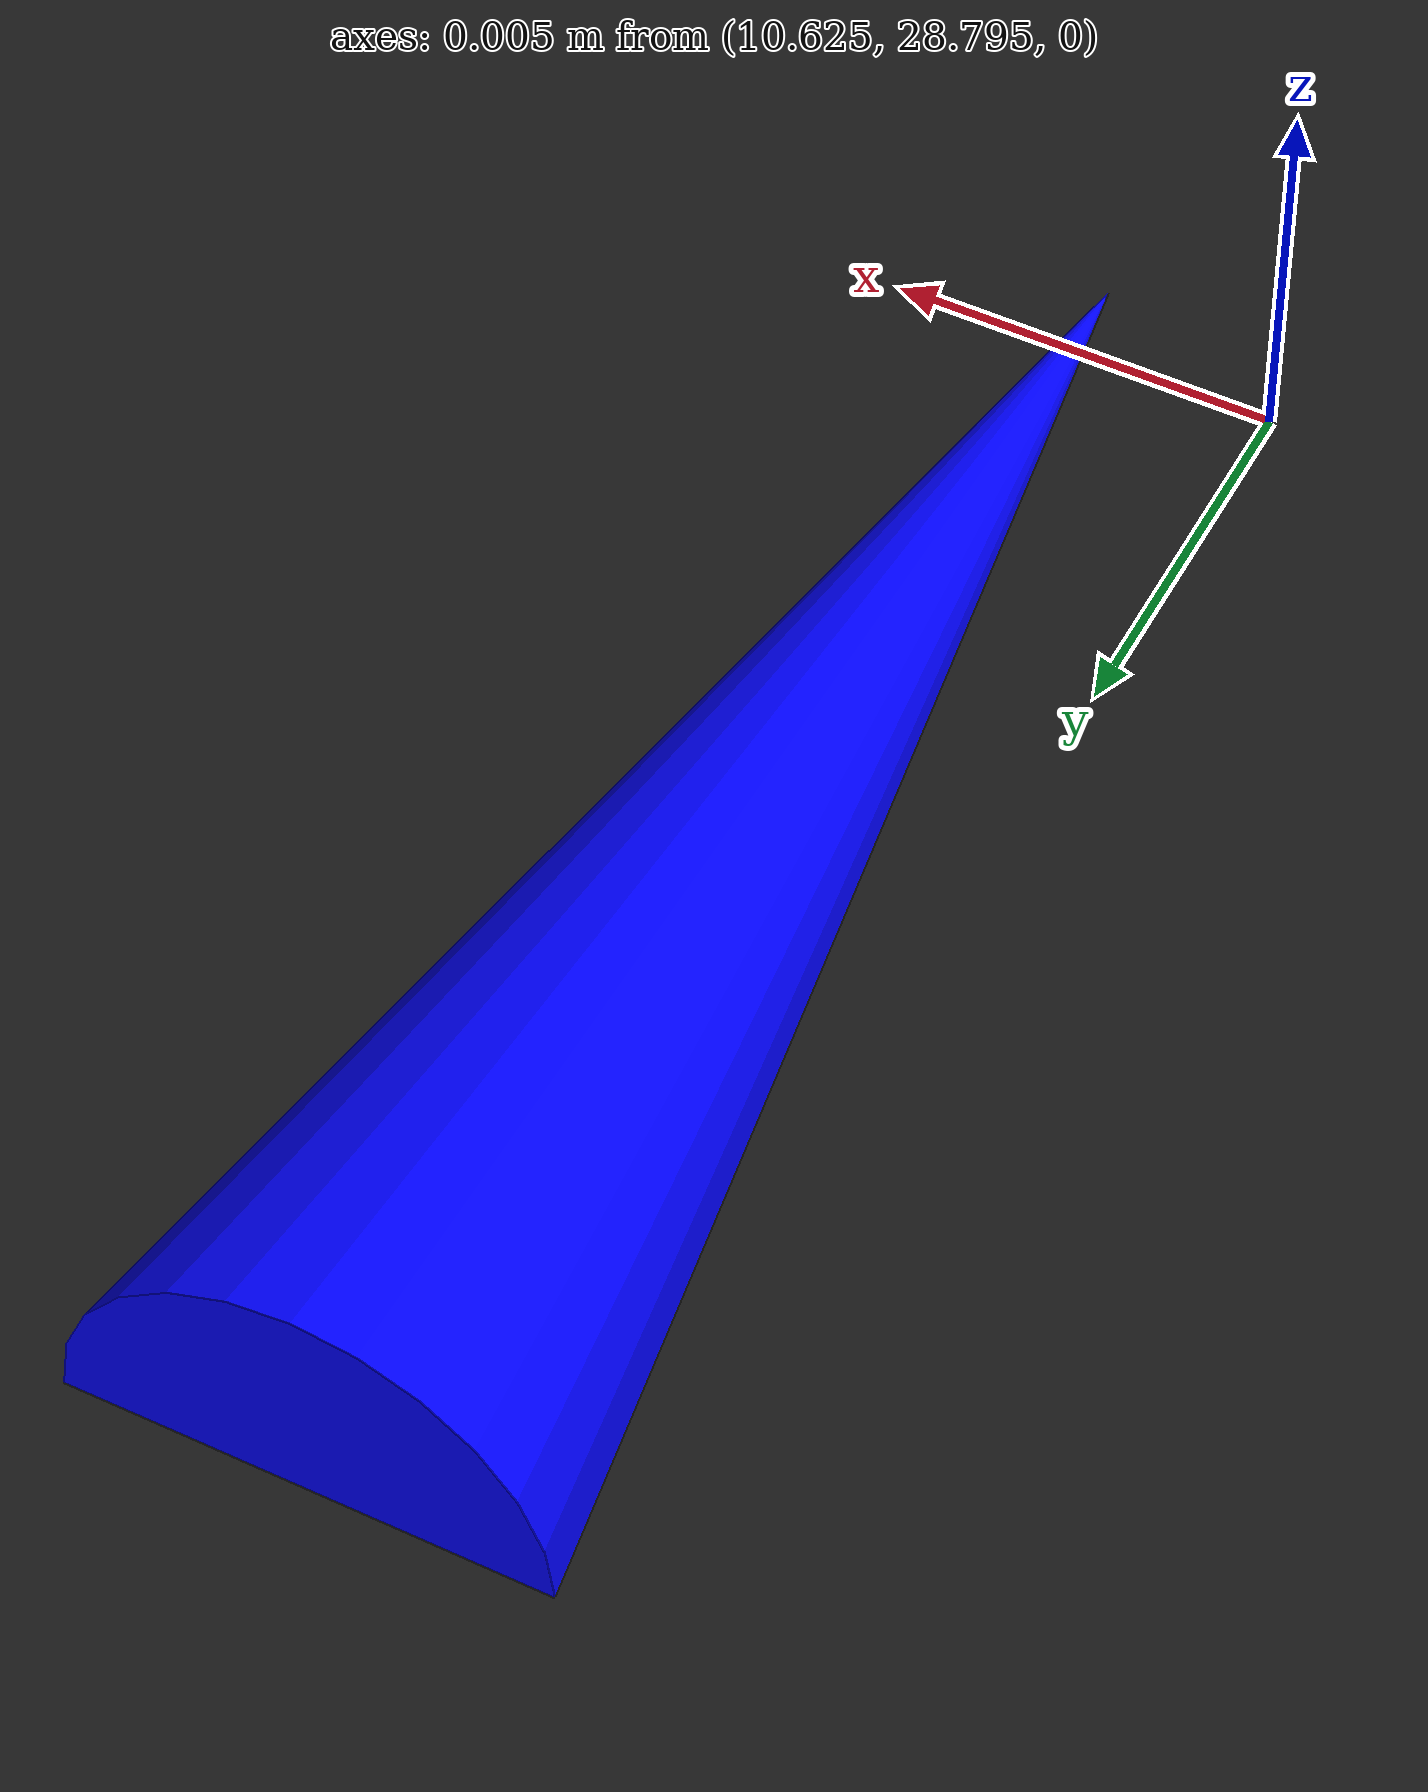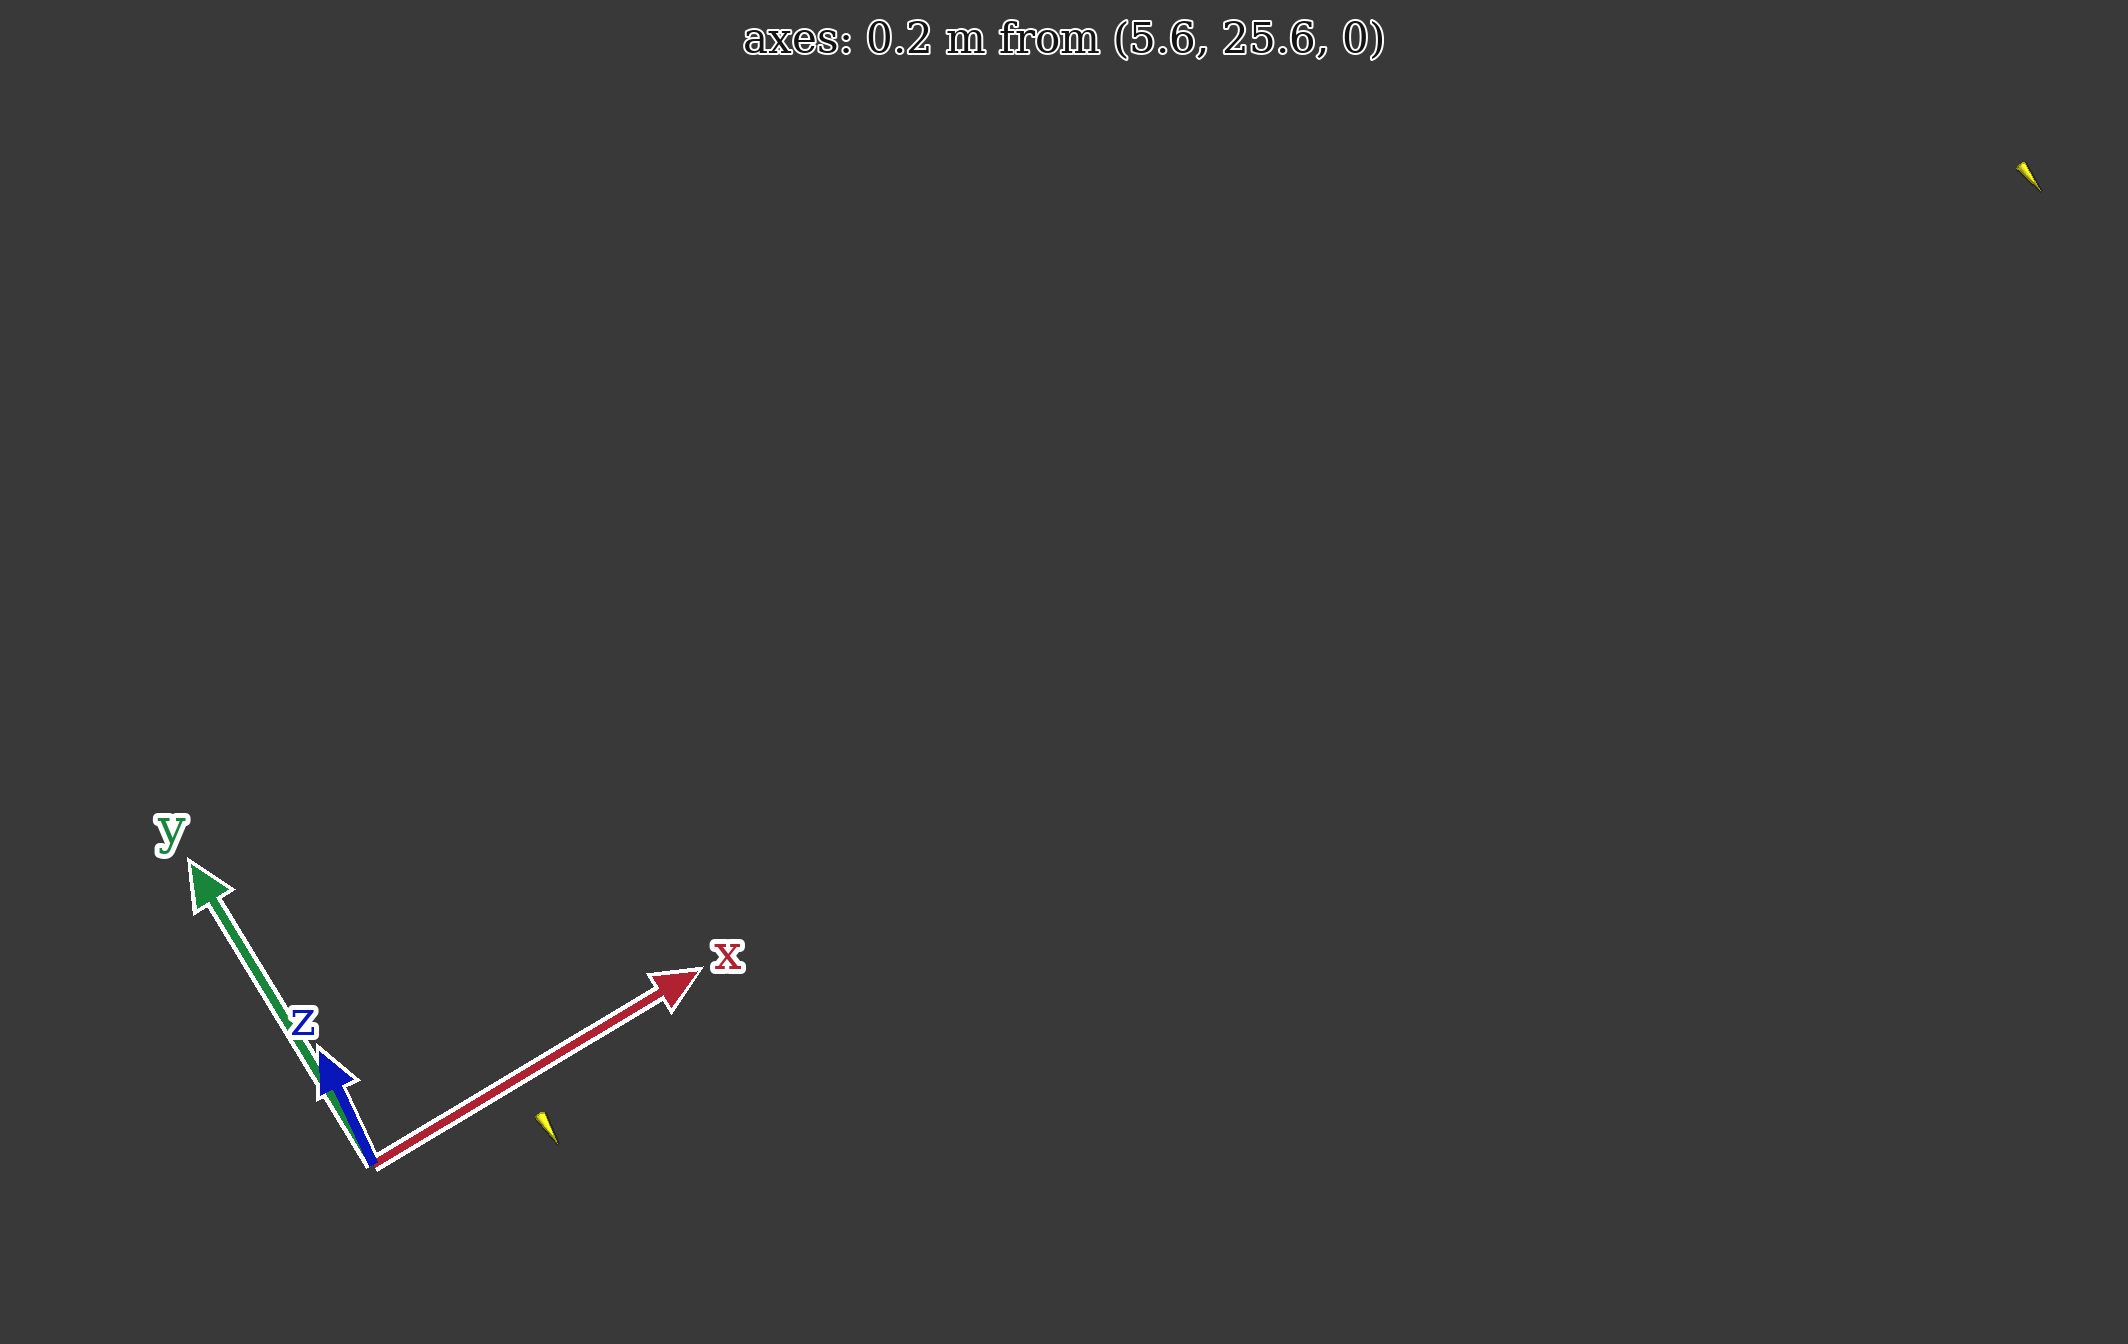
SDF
<?xml version="1.0"?>
<sdf version="1.9">
	<world name="track">
		<!-- PHYSICS -->
		<physics name="1ms" type="ignored">
			<max_step_size>
				0.001
			</max_step_size>
			<real_time_factor>
				1.0
			</real_time_factor>
		</physics>
		<gravity>
			0 0 -9.8
		</gravity>
		<magnetic_field>
			6e-06 2.3e-05 -4.2e-05
		</magnetic_field>
		<atmosphere type="adiabatic" />
		<!-- PLUGINS -->
		<plugin name="gz::sim::systems::Physics" filename="gz-sim-physics-system" />
		<plugin name="gz::sim::systems::UserCommands" filename="gz-sim-user-commands-system" />
		<plugin name="gz::sim::systems::SceneBroadcaster" filename="gz-sim-scene-broadcaster-system" />
		<plugin name="gz::sim::systems::Imu" filename="gz-sim-imu-system" />
		<gui fullscreen="0">
			<!-- 3D scene -->
			<plugin filename="MinimalScene" name="3D View">
				<gz-gui>
					<title>
						3D View
					</title>
					<property type="bool" key="showTitleBar">
						false
					</property>
					<property type="string" key="state">
						docked
					</property>
				</gz-gui>
				<engine>
					ogre2
				</engine>
				<scene>
					scene
				</scene>
				<ambient_light>
					0.4 0.4 0.4
				</ambient_light>
				<background_color>
					0.8 0.8 0.8
				</background_color>
				<camera_pose>
					-6 0 6 0 0.5 0
				</camera_pose>
			</plugin>
			<!-- Plugins that add functionality to the scene -->
			<plugin filename="EntityContextMenuPlugin" name="Entity context menu">
				<gz-gui>
					<property key="state" type="string">
						floating
					</property>
					<property key="width" type="double">
						5
					</property>
					<property key="height" type="double">
						5
					</property>
					<property key="showTitleBar" type="bool">
						false
					</property>
				</gz-gui>
			</plugin>
			<plugin filename="GzSceneManager" name="Scene Manager">
				<gz-gui>
					<property key="resizable" type="bool">
						false
					</property>
					<property key="width" type="double">
						5
					</property>
					<property key="height" type="double">
						5
					</property>
					<property key="state" type="string">
						floating
					</property>
					<property key="showTitleBar" type="bool">
						false
					</property>
				</gz-gui>
			</plugin>
			<plugin filename="InteractiveViewControl" name="Interactive view control">
				<gz-gui>
					<property key="resizable" type="bool">
						false
					</property>
					<property key="width" type="double">
						5
					</property>
					<property key="height" type="double">
						5
					</property>
					<property key="state" type="string">
						floating
					</property>
					<property key="showTitleBar" type="bool">
						false
					</property>
				</gz-gui>
			</plugin>
			<plugin filename="CameraTracking" name="Camera Tracking">
				<gz-gui>
					<property key="resizable" type="bool">
						false
					</property>
					<property key="width" type="double">
						5
					</property>
					<property key="height" type="double">
						5
					</property>
					<property key="state" type="string">
						floating
					</property>
					<property key="showTitleBar" type="bool">
						false
					</property>
				</gz-gui>
			</plugin>
			<plugin name="World control" filename="WorldControl">
				<gz-gui>
					<title>
						World control
					</title>
					<property type="bool" key="showTitleBar">
						0
					</property>
					<property type="bool" key="resizable">
						0
					</property>
					<property type="double" key="height">
						72
					</property>
					<property type="double" key="z">
						1
					</property>
					<property type="string" key="state">
						floating
					</property>
					<anchors target="3D View">
						<line own="left" target="left" />
						<line own="bottom" target="bottom" />
					</anchors>
				</gz-gui>
				<play_pause>
					1
				</play_pause>
				<step>
					1
				</step>
				<start_paused>
					1
				</start_paused>
			</plugin>
			<plugin name="World stats" filename="WorldStats">
				<gz-gui>
					<title>
						World stats
					</title>
					<property type="bool" key="showTitleBar">
						0
					</property>
					<property type="bool" key="resizable">
						0
					</property>
					<property type="double" key="height">
						110
					</property>
					<property type="double" key="width">
						290
					</property>
					<property type="double" key="z">
						1
					</property>
					<property type="string" key="state">
						floating
					</property>
					<anchors target="3D View">
						<line own="right" target="right" />
						<line own="bottom" target="bottom" />
					</anchors>
				</gz-gui>
				<sim_time>
					1
				</sim_time>
				<real_time>
					1
				</real_time>
				<real_time_factor>
					1
				</real_time_factor>
				<iterations>
					1
				</iterations>
			</plugin>
			<plugin filename="VisualizeLidar" name="Visualize Lidar">
			</plugin>
			<plugin filename="ImageDisplay" name="Image Display">
			</plugin>
			<!-- Inspector -->
			<plugin filename="ComponentInspector" name="Component inspector">
				<ignition-gui>
					<property type="string" key="state">
						docked
					</property>
				</ignition-gui>
			</plugin>
			<!-- Entity tree -->
			<plugin filename="EntityTree" name="Entity tree">
				<ignition-gui>
					<property type="string" key="state">
						docked
					</property>
				</ignition-gui>
			</plugin>
		</gui>
		<!-- SENSORS -->
		<plugin filename="gz-sim-sensors-system" name="gz::sim::systems::Sensors">
			<render_engine>
				ogre2
			</render_engine>
		</plugin>
		<!-- AMBIENT -->
		<scene>
			<ambient>
				1 1 1 1
			</ambient>
			<background>
				0.8 0.8 0.8 1
			</background>
			<shadows>
				1
			</shadows>
		</scene>
		<light name="sun" type="directional">
			<cast_shadows>
				1
			</cast_shadows>
			<pose>
				0 0 10 0 0 0
			</pose>
			<diffuse>
				0.8 0.8 0.8 1
			</diffuse>
			<specular>
				0.8 0.8 0.8 1
			</specular>
			<attenuation>
				<range>
					1000
				</range>
				<constant>
					0.9
				</constant>
				<linear>
					0.01
				</linear>
				<quadratic>
					0.001
				</quadratic>
			</attenuation>
			<direction>
				-0.5 0.1 -0.9
			</direction>
		</light>
		<model name="ground_plane">
			<static>
				true
			</static>
			<link name="link">
				<collision name="collision">
					<geometry>
						<plane>
							<normal>
								0 0 1
							</normal>
							<size>
								100 100
							</size>
						</plane>
					</geometry>
					<surface>
						<friction>
							<dart />
						</friction>
						<bounce />
						<contact />
					</surface>
				</collision>
				<visual name="visual">
					<geometry>
						<plane>
							<normal>
								0 0 1
							</normal>
							<size>
								100 100
							</size>
						</plane>
					</geometry>
					<material>
						<ambient>
							0.1 0.1 0.1 1
						</ambient>
						<diffuse>
							0.1 0.1 0.1 1
						</diffuse>
						<specular>
							0.8 0.8 0.8 1
						</specular>
					</material>
				</visual>
				<pose>
					0 0 0 0 -0 0
				</pose>
				<inertial>
					<pose>
						0 0 0 0 -0 0
					</pose>
					<mass>
						1
					</mass>
					<inertia>
						<ixx>
							1
						</ixx>
						<ixy>
							0
						</ixy>
						<ixz>
							0
						</ixz>
						<iyy>
							1
						</iyy>
						<iyz>
							0
						</iyz>
						<izz>
							1
						</izz>
					</inertia>
				</inertial>
				<enable_wind>
					false
				</enable_wind>
			</link>
			<pose>
				0 0 0 0 -0 0
			</pose>
			<self_collide>
				false
			</self_collide>
		</model>
		<!-- TRACK -->
		<model name="cones">
			<pose>
				0 0 0 0 0 0
			</pose>
			<link name="cone_0_link">
				<collision name="cone_0_collision">
					<geometry>
						<mesh>
							<uri>
								/home/ubuntu/psd_ws/src/psd_gazebo_sim/psd_gazebo_worlds/world/models/cone/meshes/cone.stl
							</uri>
							<scale>
								0.001 0.001 0.001
							</scale>
						</mesh>
					</geometry>
				</collision>
				<visual name="cone_0_visual">
					<geometry>
						<mesh>
							<uri>
								/home/ubuntu/psd_ws/src/psd_gazebo_sim/psd_gazebo_worlds/world/models/cone/meshes/cone.stl
							</uri>
							<scale>
								0.001 0.001 0.001
							</scale>
						</mesh>
					</geometry>
					<material>
						<ambient>
							1 1 0 1
						</ambient>
						<diffuse>
							1 1 0 1
						</diffuse>
						<specular>
							1 1 0 1
						</specular>
					</material>
				</visual>
				<pose>
					5.688073798552464 25.575976039184496 0.0 1.57 0 0
				</pose>
				<enable_wind>
					false
				</enable_wind>
			</link>
			<link name="cone_1_link">
				<collision name="cone_1_collision">
					<geometry>
						<mesh>
							<uri>
								/home/ubuntu/psd_ws/src/psd_gazebo_sim/psd_gazebo_worlds/world/models/cone/meshes/cone.stl
							</uri>
							<scale>
								0.001 0.001 0.001
							</scale>
						</mesh>
					</geometry>
				</collision>
				<visual name="cone_1_visual">
					<geometry>
						<mesh>
							<uri>
								/home/ubuntu/psd_ws/src/psd_gazebo_sim/psd_gazebo_worlds/world/models/cone/meshes/cone.stl
							</uri>
							<scale>
								0.001 0.001 0.001
							</scale>
						</mesh>
					</geometry>
					<material>
						<ambient>
							1 1 0 1
						</ambient>
						<diffuse>
							1 1 0 1
						</diffuse>
						<specular>
							1 1 0 1
						</specular>
					</material>
				</visual>
				<pose>
					6.686783688672199 25.608392984830942 0.0 1.57 0 0
				</pose>
				<enable_wind>
					false
				</enable_wind>
			</link>
			<link name="cone_2_link">
				<collision name="cone_2_collision">
					<geometry>
						<mesh>
							<uri>
								/home/ubuntu/psd_ws/src/psd_gazebo_sim/psd_gazebo_worlds/world/models/cone/meshes/cone.stl
							</uri>
							<scale>
								0.001 0.001 0.001
							</scale>
						</mesh>
					</geometry>
				</collision>
				<visual name="cone_2_visual">
					<geometry>
						<mesh>
							<uri>
								/home/ubuntu/psd_ws/src/psd_gazebo_sim/psd_gazebo_worlds/world/models/cone/meshes/cone.stl
							</uri>
							<scale>
								0.001 0.001 0.001
							</scale>
						</mesh>
					</geometry>
					<material>
						<ambient>
							1 1 0 1
						</ambient>
						<diffuse>
							1 1 0 1
						</diffuse>
						<specular>
							1 1 0 1
						</specular>
					</material>
				</visual>
				<pose>
					7.683275531344529 25.641049078737048 0.0 1.57 0 0
				</pose>
				<enable_wind>
					false
				</enable_wind>
			</link>
			<link name="cone_3_link">
				<collision name="cone_3_collision">
					<geometry>
						<mesh>
							<uri>
								/home/ubuntu/psd_ws/src/psd_gazebo_sim/psd_gazebo_worlds/world/models/cone/meshes/cone.stl
							</uri>
							<scale>
								0.001 0.001 0.001
							</scale>
						</mesh>
					</geometry>
				</collision>
				<visual name="cone_3_visual">
					<geometry>
						<mesh>
							<uri>
								/home/ubuntu/psd_ws/src/psd_gazebo_sim/psd_gazebo_worlds/world/models/cone/meshes/cone.stl
							</uri>
							<scale>
								0.001 0.001 0.001
							</scale>
						</mesh>
					</geometry>
					<material>
						<ambient>
							1 1 0 1
						</ambient>
						<diffuse>
							1 1 0 1
						</diffuse>
						<specular>
							1 1 0 1
						</specular>
					</material>
				</visual>
				<pose>
					8.67759646067718 25.672478593219495 0.0 1.57 0 0
				</pose>
				<enable_wind>
					false
				</enable_wind>
			</link>
			<link name="cone_4_link">
				<collision name="cone_4_collision">
					<geometry>
						<mesh>
							<uri>
								/home/ubuntu/psd_ws/src/psd_gazebo_sim/psd_gazebo_worlds/world/models/cone/meshes/cone.stl
							</uri>
							<scale>
								0.001 0.001 0.001
							</scale>
						</mesh>
					</geometry>
				</collision>
				<visual name="cone_4_visual">
					<geometry>
						<mesh>
							<uri>
								/home/ubuntu/psd_ws/src/psd_gazebo_sim/psd_gazebo_worlds/world/models/cone/meshes/cone.stl
							</uri>
							<scale>
								0.001 0.001 0.001
							</scale>
						</mesh>
					</geometry>
					<material>
						<ambient>
							1 1 0 1
						</ambient>
						<diffuse>
							1 1 0 1
						</diffuse>
						<specular>
							1 1 0 1
						</specular>
					</material>
				</visual>
				<pose>
					9.669788208603379 25.701225398652994 0.0 1.57 0 0
				</pose>
				<enable_wind>
					false
				</enable_wind>
			</link>
			<link name="cone_5_link">
				<collision name="cone_5_collision">
					<geometry>
						<mesh>
							<uri>
								/home/ubuntu/psd_ws/src/psd_gazebo_sim/psd_gazebo_worlds/world/models/cone/meshes/cone.stl
							</uri>
							<scale>
								0.001 0.001 0.001
							</scale>
						</mesh>
					</geometry>
				</collision>
				<visual name="cone_5_visual">
					<geometry>
						<mesh>
							<uri>
								/home/ubuntu/psd_ws/src/psd_gazebo_sim/psd_gazebo_worlds/world/models/cone/meshes/cone.stl
							</uri>
							<scale>
								0.001 0.001 0.001
							</scale>
						</mesh>
					</geometry>
					<material>
						<ambient>
							1 1 0 1
						</ambient>
						<diffuse>
							1 1 0 1
						</diffuse>
						<specular>
							1 1 0 1
						</specular>
					</material>
				</visual>
				<pose>
					10.659880707778479 25.725842802243847 0.0 1.57 0 0
				</pose>
				<enable_wind>
					false
				</enable_wind>
			</link>
			<link name="cone_6_link">
				<collision name="cone_6_collision">
					<geometry>
						<mesh>
							<uri>
								/home/ubuntu/psd_ws/src/psd_gazebo_sim/psd_gazebo_worlds/world/models/cone/meshes/cone.stl
							</uri>
							<scale>
								0.001 0.001 0.001
							</scale>
						</mesh>
					</geometry>
				</collision>
				<visual name="cone_6_visual">
					<geometry>
						<mesh>
							<uri>
								/home/ubuntu/psd_ws/src/psd_gazebo_sim/psd_gazebo_worlds/world/models/cone/meshes/cone.stl
							</uri>
							<scale>
								0.001 0.001 0.001
							</scale>
						</mesh>
					</geometry>
					<material>
						<ambient>
							1 1 0 1
						</ambient>
						<diffuse>
							1 1 0 1
						</diffuse>
						<specular>
							1 1 0 1
						</specular>
					</material>
				</visual>
				<pose>
					13.617552664488128 25.760592629749596 0.0 1.57 0 0
				</pose>
				<enable_wind>
					false
				</enable_wind>
			</link>
			<link name="cone_7_link">
				<collision name="cone_7_collision">
					<geometry>
						<mesh>
							<uri>
								/home/ubuntu/psd_ws/src/psd_gazebo_sim/psd_gazebo_worlds/world/models/cone/meshes/cone.stl
							</uri>
							<scale>
								0.001 0.001 0.001
							</scale>
						</mesh>
					</geometry>
				</collision>
				<visual name="cone_7_visual">
					<geometry>
						<mesh>
							<uri>
								/home/ubuntu/psd_ws/src/psd_gazebo_sim/psd_gazebo_worlds/world/models/cone/meshes/cone.stl
							</uri>
							<scale>
								0.001 0.001 0.001
							</scale>
						</mesh>
					</geometry>
					<material>
						<ambient>
							1 1 0 1
						</ambient>
						<diffuse>
							1 1 0 1
						</diffuse>
						<specular>
							1 1 0 1
						</specular>
					</material>
				</visual>
				<pose>
					14.59909152529048 25.754414718774193 0.0 1.57 0 0
				</pose>
				<enable_wind>
					false
				</enable_wind>
			</link>
			<link name="cone_8_link">
				<collision name="cone_8_collision">
					<geometry>
						<mesh>
							<uri>
								/home/ubuntu/psd_ws/src/psd_gazebo_sim/psd_gazebo_worlds/world/models/cone/meshes/cone.stl
							</uri>
							<scale>
								0.001 0.001 0.001
							</scale>
						</mesh>
					</geometry>
				</collision>
				<visual name="cone_8_visual">
					<geometry>
						<mesh>
							<uri>
								/home/ubuntu/psd_ws/src/psd_gazebo_sim/psd_gazebo_worlds/world/models/cone/meshes/cone.stl
							</uri>
							<scale>
								0.001 0.001 0.001
							</scale>
						</mesh>
					</geometry>
					<material>
						<ambient>
							1 1 0 1
						</ambient>
						<diffuse>
							1 1 0 1
						</diffuse>
						<specular>
							1 1 0 1
						</specular>
					</material>
				</visual>
				<pose>
					15.57828483089903 25.737018465539393 0.0 1.57 0 0
				</pose>
				<enable_wind>
					false
				</enable_wind>
			</link>
			<link name="cone_9_link">
				<collision name="cone_9_collision">
					<geometry>
						<mesh>
							<uri>
								/home/ubuntu/psd_ws/src/psd_gazebo_sim/psd_gazebo_worlds/world/models/cone/meshes/cone.stl
							</uri>
							<scale>
								0.001 0.001 0.001
							</scale>
						</mesh>
					</geometry>
				</collision>
				<visual name="cone_9_visual">
					<geometry>
						<mesh>
							<uri>
								/home/ubuntu/psd_ws/src/psd_gazebo_sim/psd_gazebo_worlds/world/models/cone/meshes/cone.stl
							</uri>
							<scale>
								0.001 0.001 0.001
							</scale>
						</mesh>
					</geometry>
					<material>
						<ambient>
							1 1 0 1
						</ambient>
						<diffuse>
							1 1 0 1
						</diffuse>
						<specular>
							1 1 0 1
						</specular>
					</material>
				</visual>
				<pose>
					16.55496136632748 25.707018440790492 0.0 1.57 0 0
				</pose>
				<enable_wind>
					false
				</enable_wind>
			</link>
			<link name="cone_10_link">
				<collision name="cone_10_collision">
					<geometry>
						<mesh>
							<uri>
								/home/ubuntu/psd_ws/src/psd_gazebo_sim/psd_gazebo_worlds/world/models/cone/meshes/cone.stl
							</uri>
							<scale>
								0.001 0.001 0.001
							</scale>
						</mesh>
					</geometry>
				</collision>
				<visual name="cone_10_visual">
					<geometry>
						<mesh>
							<uri>
								/home/ubuntu/psd_ws/src/psd_gazebo_sim/psd_gazebo_worlds/world/models/cone/meshes/cone.stl
							</uri>
							<scale>
								0.001 0.001 0.001
							</scale>
						</mesh>
					</geometry>
					<material>
						<ambient>
							1 1 0 1
						</ambient>
						<diffuse>
							1 1 0 1
						</diffuse>
						<specular>
							1 1 0 1
						</specular>
					</material>
				</visual>
				<pose>
					17.52889540500738 25.663042474111194 0.0 1.57 0 0
				</pose>
				<enable_wind>
					false
				</enable_wind>
			</link>
			<link name="cone_11_link">
				<collision name="cone_11_collision">
					<geometry>
						<mesh>
							<uri>
								/home/ubuntu/psd_ws/src/psd_gazebo_sim/psd_gazebo_worlds/world/models/cone/meshes/cone.stl
							</uri>
							<scale>
								0.001 0.001 0.001
							</scale>
						</mesh>
					</geometry>
				</collision>
				<visual name="cone_11_visual">
					<geometry>
						<mesh>
							<uri>
								/home/ubuntu/psd_ws/src/psd_gazebo_sim/psd_gazebo_worlds/world/models/cone/meshes/cone.stl
							</uri>
							<scale>
								0.001 0.001 0.001
							</scale>
						</mesh>
					</geometry>
					<material>
						<ambient>
							1 1 0 1
						</ambient>
						<diffuse>
							1 1 0 1
						</diffuse>
						<specular>
							1 1 0 1
						</specular>
					</material>
				</visual>
				<pose>
					18.48063525037708 25.60132437325189 0.0 1.57 0 0
				</pose>
				<enable_wind>
					false
				</enable_wind>
			</link>
			<link name="cone_12_link">
				<collision name="cone_12_collision">
					<geometry>
						<mesh>
							<uri>
								/home/ubuntu/psd_ws/src/psd_gazebo_sim/psd_gazebo_worlds/world/models/cone/meshes/cone.stl
							</uri>
							<scale>
								0.001 0.001 0.001
							</scale>
						</mesh>
					</geometry>
				</collision>
				<visual name="cone_12_visual">
					<geometry>
						<mesh>
							<uri>
								/home/ubuntu/psd_ws/src/psd_gazebo_sim/psd_gazebo_worlds/world/models/cone/meshes/cone.stl
							</uri>
							<scale>
								0.001 0.001 0.001
							</scale>
						</mesh>
					</geometry>
					<material>
						<ambient>
							1 1 0 1
						</ambient>
						<diffuse>
							1 1 0 1
						</diffuse>
						<specular>
							1 1 0 1
						</specular>
					</material>
				</visual>
				<pose>
					19.38169790665118 25.502228943997743 0.0 1.57 0 0
				</pose>
				<enable_wind>
					false
				</enable_wind>
			</link>
			<link name="cone_13_link">
				<collision name="cone_13_collision">
					<geometry>
						<mesh>
							<uri>
								/home/ubuntu/psd_ws/src/psd_gazebo_sim/psd_gazebo_worlds/world/models/cone/meshes/cone.stl
							</uri>
							<scale>
								0.001 0.001 0.001
							</scale>
						</mesh>
					</geometry>
				</collision>
				<visual name="cone_13_visual">
					<geometry>
						<mesh>
							<uri>
								/home/ubuntu/psd_ws/src/psd_gazebo_sim/psd_gazebo_worlds/world/models/cone/meshes/cone.stl
							</uri>
							<scale>
								0.001 0.001 0.001
							</scale>
						</mesh>
					</geometry>
					<material>
						<ambient>
							1 1 0 1
						</ambient>
						<diffuse>
							1 1 0 1
						</diffuse>
						<specular>
							1 1 0 1
						</specular>
					</material>
				</visual>
				<pose>
					21.00274022877608 25.108634410740947 0.0 1.57 0 0
				</pose>
				<enable_wind>
					false
				</enable_wind>
			</link>
			<link name="cone_14_link">
				<collision name="cone_14_collision">
					<geometry>
						<mesh>
							<uri>
								/home/ubuntu/psd_ws/src/psd_gazebo_sim/psd_gazebo_worlds/world/models/cone/meshes/cone.stl
							</uri>
							<scale>
								0.001 0.001 0.001
							</scale>
						</mesh>
					</geometry>
				</collision>
				<visual name="cone_14_visual">
					<geometry>
						<mesh>
							<uri>
								/home/ubuntu/psd_ws/src/psd_gazebo_sim/psd_gazebo_worlds/world/models/cone/meshes/cone.stl
							</uri>
							<scale>
								0.001 0.001 0.001
							</scale>
						</mesh>
					</geometry>
					<material>
						<ambient>
							1 1 0 1
						</ambient>
						<diffuse>
							1 1 0 1
						</diffuse>
						<specular>
							1 1 0 1
						</specular>
					</material>
				</visual>
				<pose>
					21.69623795675203 24.788112101455546 0.0 1.57 0 0
				</pose>
				<enable_wind>
					false
				</enable_wind>
			</link>
			<link name="cone_15_link">
				<collision name="cone_15_collision">
					<geometry>
						<mesh>
							<uri>
								/home/ubuntu/psd_ws/src/psd_gazebo_sim/psd_gazebo_worlds/world/models/cone/meshes/cone.stl
							</uri>
							<scale>
								0.001 0.001 0.001
							</scale>
						</mesh>
					</geometry>
				</collision>
				<visual name="cone_15_visual">
					<geometry>
						<mesh>
							<uri>
								/home/ubuntu/psd_ws/src/psd_gazebo_sim/psd_gazebo_worlds/world/models/cone/meshes/cone.stl
							</uri>
							<scale>
								0.001 0.001 0.001
							</scale>
						</mesh>
					</geometry>
					<material>
						<ambient>
							1 1 0 1
						</ambient>
						<diffuse>
							1 1 0 1
						</diffuse>
						<specular>
							1 1 0 1
						</specular>
					</material>
				</visual>
				<pose>
					22.81574538601283 23.855564008487697 0.0 1.57 0 0
				</pose>
				<enable_wind>
					false
				</enable_wind>
			</link>
			<link name="cone_16_link">
				<collision name="cone_16_collision">
					<geometry>
						<mesh>
							<uri>
								/home/ubuntu/psd_ws/src/psd_gazebo_sim/psd_gazebo_worlds/world/models/cone/meshes/cone.stl
							</uri>
							<scale>
								0.001 0.001 0.001
							</scale>
						</mesh>
					</geometry>
				</collision>
				<visual name="cone_16_visual">
					<geometry>
						<mesh>
							<uri>
								/home/ubuntu/psd_ws/src/psd_gazebo_sim/psd_gazebo_worlds/world/models/cone/meshes/cone.stl
							</uri>
							<scale>
								0.001 0.001 0.001
							</scale>
						</mesh>
					</geometry>
					<material>
						<ambient>
							1 1 0 1
						</ambient>
						<diffuse>
							1 1 0 1
						</diffuse>
						<specular>
							1 1 0 1
						</specular>
					</material>
				</visual>
				<pose>
					23.262238576535328 23.235157435865148 0.0 1.57 0 0
				</pose>
				<enable_wind>
					false
				</enable_wind>
			</link>
			<link name="cone_17_link">
				<collision name="cone_17_collision">
					<geometry>
						<mesh>
							<uri>
								/home/ubuntu/psd_ws/src/psd_gazebo_sim/psd_gazebo_worlds/world/models/cone/meshes/cone.stl
							</uri>
							<scale>
								0.001 0.001 0.001
							</scale>
						</mesh>
					</geometry>
				</collision>
				<visual name="cone_17_visual">
					<geometry>
						<mesh>
							<uri>
								/home/ubuntu/psd_ws/src/psd_gazebo_sim/psd_gazebo_worlds/world/models/cone/meshes/cone.stl
							</uri>
							<scale>
								0.001 0.001 0.001
							</scale>
						</mesh>
					</geometry>
					<material>
						<ambient>
							1 1 0 1
						</ambient>
						<diffuse>
							1 1 0 1
						</diffuse>
						<specular>
							1 1 0 1
						</specular>
					</material>
				</visual>
				<pose>
					23.625085575957428 22.533576793799497 0.0 1.57 0 0
				</pose>
				<enable_wind>
					false
				</enable_wind>
			</link>
			<link name="cone_18_link">
				<collision name="cone_18_collision">
					<geometry>
						<mesh>
							<uri>
								/home/ubuntu/psd_ws/src/psd_gazebo_sim/psd_gazebo_worlds/world/models/cone/meshes/cone.stl
							</uri>
							<scale>
								0.001 0.001 0.001
							</scale>
						</mesh>
					</geometry>
				</collision>
				<visual name="cone_18_visual">
					<geometry>
						<mesh>
							<uri>
								/home/ubuntu/psd_ws/src/psd_gazebo_sim/psd_gazebo_worlds/world/models/cone/meshes/cone.stl
							</uri>
							<scale>
								0.001 0.001 0.001
							</scale>
						</mesh>
					</geometry>
					<material>
						<ambient>
							1 1 0 1
						</ambient>
						<diffuse>
							1 1 0 1
						</diffuse>
						<specular>
							1 1 0 1
						</specular>
					</material>
				</visual>
				<pose>
					23.90270858020368 21.76756350447795 0.0 1.57 0 0
				</pose>
				<enable_wind>
					false
				</enable_wind>
			</link>
			<link name="cone_19_link">
				<collision name="cone_19_collision">
					<geometry>
						<mesh>
							<uri>
								/home/ubuntu/psd_ws/src/psd_gazebo_sim/psd_gazebo_worlds/world/models/cone/meshes/cone.stl
							</uri>
							<scale>
								0.001 0.001 0.001
							</scale>
						</mesh>
					</geometry>
				</collision>
				<visual name="cone_19_visual">
					<geometry>
						<mesh>
							<uri>
								/home/ubuntu/psd_ws/src/psd_gazebo_sim/psd_gazebo_worlds/world/models/cone/meshes/cone.stl
							</uri>
							<scale>
								0.001 0.001 0.001
							</scale>
						</mesh>
					</geometry>
					<material>
						<ambient>
							1 1 0 1
						</ambient>
						<diffuse>
							1 1 0 1
						</diffuse>
						<specular>
							1 1 0 1
						</specular>
					</material>
				</visual>
				<pose>
					24.16895681450728 20.177439498432797 0.0 1.57 0 0
				</pose>
				<enable_wind>
					false
				</enable_wind>
			</link>
			<link name="cone_20_link">
				<collision name="cone_20_collision">
					<geometry>
						<mesh>
							<uri>
								/home/ubuntu/psd_ws/src/psd_gazebo_sim/psd_gazebo_worlds/world/models/cone/meshes/cone.stl
							</uri>
							<scale>
								0.001 0.001 0.001
							</scale>
						</mesh>
					</geometry>
				</collision>
				<visual name="cone_20_visual">
					<geometry>
						<mesh>
							<uri>
								/home/ubuntu/psd_ws/src/psd_gazebo_sim/psd_gazebo_worlds/world/models/cone/meshes/cone.stl
							</uri>
							<scale>
								0.001 0.001 0.001
							</scale>
						</mesh>
					</geometry>
					<material>
						<ambient>
							1 1 0 1
						</ambient>
						<diffuse>
							1 1 0 1
						</diffuse>
						<specular>
							1 1 0 1
						</specular>
					</material>
				</visual>
				<pose>
					24.142929222418978 19.390641615551097 0.0 1.57 0 0
				</pose>
				<enable_wind>
					false
				</enable_wind>
			</link>
			<link name="cone_21_link">
				<collision name="cone_21_collision">
					<geometry>
						<mesh>
							<uri>
								/home/ubuntu/psd_ws/src/psd_gazebo_sim/psd_gazebo_worlds/world/models/cone/meshes/cone.stl
							</uri>
							<scale>
								0.001 0.001 0.001
							</scale>
						</mesh>
					</geometry>
				</collision>
				<visual name="cone_21_visual">
					<geometry>
						<mesh>
							<uri>
								/home/ubuntu/psd_ws/src/psd_gazebo_sim/psd_gazebo_worlds/world/models/cone/meshes/cone.stl
							</uri>
							<scale>
								0.001 0.001 0.001
							</scale>
						</mesh>
					</geometry>
					<material>
						<ambient>
							1 1 0 1
						</ambient>
						<diffuse>
							1 1 0 1
						</diffuse>
						<specular>
							1 1 0 1
						</specular>
					</material>
				</visual>
				<pose>
					24.00638298037288 18.62923715340539 0.0 1.57 0 0
				</pose>
				<enable_wind>
					false
				</enable_wind>
			</link>
			<link name="cone_22_link">
				<collision name="cone_22_collision">
					<geometry>
						<mesh>
							<uri>
								/home/ubuntu/psd_ws/src/psd_gazebo_sim/psd_gazebo_worlds/world/models/cone/meshes/cone.stl
							</uri>
							<scale>
								0.001 0.001 0.001
							</scale>
						</mesh>
					</geometry>
				</collision>
				<visual name="cone_22_visual">
					<geometry>
						<mesh>
							<uri>
								/home/ubuntu/psd_ws/src/psd_gazebo_sim/psd_gazebo_worlds/world/models/cone/meshes/cone.stl
							</uri>
							<scale>
								0.001 0.001 0.001
							</scale>
						</mesh>
					</geometry>
					<material>
						<ambient>
							1 1 0 1
						</ambient>
						<diffuse>
							1 1 0 1
						</diffuse>
						<specular>
							1 1 0 1
						</specular>
					</material>
				</visual>
				<pose>
					23.75950698838113 17.910587112532546 0.0 1.57 0 0
				</pose>
				<enable_wind>
					false
				</enable_wind>
			</link>
			<link name="cone_23_link">
				<collision name="cone_23_collision">
					<geometry>
						<mesh>
							<uri>
								/home/ubuntu/psd_ws/src/psd_gazebo_sim/psd_gazebo_worlds/world/models/cone/meshes/cone.stl
							</uri>
							<scale>
								0.001 0.001 0.001
							</scale>
						</mesh>
					</geometry>
				</collision>
				<visual name="cone_23_visual">
					<geometry>
						<mesh>
							<uri>
								/home/ubuntu/psd_ws/src/psd_gazebo_sim/psd_gazebo_worlds/world/models/cone/meshes/cone.stl
							</uri>
							<scale>
								0.001 0.001 0.001
							</scale>
						</mesh>
					</geometry>
					<material>
						<ambient>
							1 1 0 1
						</ambient>
						<diffuse>
							1 1 0 1
						</diffuse>
						<specular>
							1 1 0 1
						</specular>
					</material>
				</visual>
				<pose>
					23.401518285041178 17.242702057517494 0.0 1.57 0 0
				</pose>
				<enable_wind>
					false
				</enable_wind>
			</link>
			<link name="cone_24_link">
				<collision name="cone_24_collision">
					<geometry>
						<mesh>
							<uri>
								/home/ubuntu/psd_ws/src/psd_gazebo_sim/psd_gazebo_worlds/world/models/cone/meshes/cone.stl
							</uri>
							<scale>
								0.001 0.001 0.001
							</scale>
						</mesh>
					</geometry>
				</collision>
				<visual name="cone_24_visual">
					<geometry>
						<mesh>
							<uri>
								/home/ubuntu/psd_ws/src/psd_gazebo_sim/psd_gazebo_worlds/world/models/cone/meshes/cone.stl
							</uri>
							<scale>
								0.001 0.001 0.001
							</scale>
						</mesh>
					</geometry>
					<material>
						<ambient>
							1 1 0 1
						</ambient>
						<diffuse>
							1 1 0 1
						</diffuse>
						<specular>
							1 1 0 1
						</specular>
					</material>
				</visual>
				<pose>
					22.36550739673898 16.043194299255696 0.0 1.57 0 0
				</pose>
				<enable_wind>
					false
				</enable_wind>
			</link>
			<link name="cone_25_link">
				<collision name="cone_25_collision">
					<geometry>
						<mesh>
							<uri>
								/home/ubuntu/psd_ws/src/psd_gazebo_sim/psd_gazebo_worlds/world/models/cone/meshes/cone.stl
							</uri>
							<scale>
								0.001 0.001 0.001
							</scale>
						</mesh>
					</geometry>
				</collision>
				<visual name="cone_25_visual">
					<geometry>
						<mesh>
							<uri>
								/home/ubuntu/psd_ws/src/psd_gazebo_sim/psd_gazebo_worlds/world/models/cone/meshes/cone.stl
							</uri>
							<scale>
								0.001 0.001 0.001
							</scale>
						</mesh>
					</geometry>
					<material>
						<ambient>
							1 1 0 1
						</ambient>
						<diffuse>
							1 1 0 1
						</diffuse>
						<specular>
							1 1 0 1
						</specular>
					</material>
				</visual>
				<pose>
					21.007376550970378 15.072803432951893 0.0 1.57 0 0
				</pose>
				<enable_wind>
					false
				</enable_wind>
			</link>
			<link name="cone_26_link">
				<collision name="cone_26_collision">
					<geometry>
						<mesh>
							<uri>
								/home/ubuntu/psd_ws/src/psd_gazebo_sim/psd_gazebo_worlds/world/models/cone/meshes/cone.stl
							</uri>
							<scale>
								0.001 0.001 0.001
							</scale>
						</mesh>
					</geometry>
				</collision>
				<visual name="cone_26_visual">
					<geometry>
						<mesh>
							<uri>
								/home/ubuntu/psd_ws/src/psd_gazebo_sim/psd_gazebo_worlds/world/models/cone/meshes/cone.stl
							</uri>
							<scale>
								0.001 0.001 0.001
							</scale>
						</mesh>
					</geometry>
					<material>
						<ambient>
							1 1 0 1
						</ambient>
						<diffuse>
							1 1 0 1
						</diffuse>
						<specular>
							1 1 0 1
						</specular>
					</material>
				</visual>
				<pose>
					20.26277547690503 14.703898176383696 0.0 1.57 0 0
				</pose>
				<enable_wind>
					false
				</enable_wind>
			</link>
			<link name="cone_27_link">
				<collision name="cone_27_collision">
					<geometry>
						<mesh>
							<uri>
								/home/ubuntu/psd_ws/src/psd_gazebo_sim/psd_gazebo_worlds/world/models/cone/meshes/cone.stl
							</uri>
							<scale>
								0.001 0.001 0.001
							</scale>
						</mesh>
					</geometry>
				</collision>
				<visual name="cone_27_visual">
					<geometry>
						<mesh>
							<uri>
								/home/ubuntu/psd_ws/src/psd_gazebo_sim/psd_gazebo_worlds/world/models/cone/meshes/cone.stl
							</uri>
							<scale>
								0.001 0.001 0.001
							</scale>
						</mesh>
					</geometry>
					<material>
						<ambient>
							1 1 0 1
						</ambient>
						<diffuse>
							1 1 0 1
						</diffuse>
						<specular>
							1 1 0 1
						</specular>
					</material>
				</visual>
				<pose>
					19.48934784503568 14.424853096212594 0.0 1.57 0 0
				</pose>
				<enable_wind>
					false
				</enable_wind>
			</link>
			<link name="cone_28_link">
				<collision name="cone_28_collision">
					<geometry>
						<mesh>
							<uri>
								/home/ubuntu/psd_ws/src/psd_gazebo_sim/psd_gazebo_worlds/world/models/cone/meshes/cone.stl
							</uri>
							<scale>
								0.001 0.001 0.001
							</scale>
						</mesh>
					</geometry>
				</collision>
				<visual name="cone_28_visual">
					<geometry>
						<mesh>
							<uri>
								/home/ubuntu/psd_ws/src/psd_gazebo_sim/psd_gazebo_worlds/world/models/cone/meshes/cone.stl
							</uri>
							<scale>
								0.001 0.001 0.001
							</scale>
						</mesh>
					</geometry>
					<material>
						<ambient>
							1 1 0 1
						</ambient>
						<diffuse>
							1 1 0 1
						</diffuse>
						<specular>
							1 1 0 1
						</specular>
					</material>
				</visual>
				<pose>
					18.696688591643728 14.242005230569994 0.0 1.57 0 0
				</pose>
				<enable_wind>
					false
				</enable_wind>
			</link>
			<link name="cone_29_link">
				<collision name="cone_29_collision">
					<geometry>
						<mesh>
							<uri>
								/home/ubuntu/psd_ws/src/psd_gazebo_sim/psd_gazebo_worlds/world/models/cone/meshes/cone.stl
							</uri>
							<scale>
								0.001 0.001 0.001
							</scale>
						</mesh>
					</geometry>
				</collision>
				<visual name="cone_29_visual">
					<geometry>
						<mesh>
							<uri>
								/home/ubuntu/psd_ws/src/psd_gazebo_sim/psd_gazebo_worlds/world/models/cone/meshes/cone.stl
							</uri>
							<scale>
								0.001 0.001 0.001
							</scale>
						</mesh>
					</geometry>
					<material>
						<ambient>
							1 1 0 1
						</ambient>
						<diffuse>
							1 1 0 1
						</diffuse>
						<specular>
							1 1 0 1
						</specular>
					</material>
				</visual>
				<pose>
					17.89609613061728 14.160577510856644 0.0 1.57 0 0
				</pose>
				<enable_wind>
					false
				</enable_wind>
			</link>
			<link name="cone_30_link">
				<collision name="cone_30_collision">
					<geometry>
						<mesh>
							<uri>
								/home/ubuntu/psd_ws/src/psd_gazebo_sim/psd_gazebo_worlds/world/models/cone/meshes/cone.stl
							</uri>
							<scale>
								0.001 0.001 0.001
							</scale>
						</mesh>
					</geometry>
				</collision>
				<visual name="cone_30_visual">
					<geometry>
						<mesh>
							<uri>
								/home/ubuntu/psd_ws/src/psd_gazebo_sim/psd_gazebo_worlds/world/models/cone/meshes/cone.stl
							</uri>
							<scale>
								0.001 0.001 0.001
							</scale>
						</mesh>
					</geometry>
					<material>
						<ambient>
							1 1 0 1
						</ambient>
						<diffuse>
							1 1 0 1
						</diffuse>
						<specular>
							1 1 0 1
						</specular>
					</material>
				</visual>
				<pose>
					17.093347822525182 14.183804943418195 0.0 1.57 0 0
				</pose>
				<enable_wind>
					false
				</enable_wind>
			</link>
			<link name="cone_31_link">
				<collision name="cone_31_collision">
					<geometry>
						<mesh>
							<uri>
								/home/ubuntu/psd_ws/src/psd_gazebo_sim/psd_gazebo_worlds/world/models/cone/meshes/cone.stl
							</uri>
							<scale>
								0.001 0.001 0.001
							</scale>
						</mesh>
					</geometry>
				</collision>
				<visual name="cone_31_visual">
					<geometry>
						<mesh>
							<uri>
								/home/ubuntu/psd_ws/src/psd_gazebo_sim/psd_gazebo_worlds/world/models/cone/meshes/cone.stl
							</uri>
							<scale>
								0.001 0.001 0.001
							</scale>
						</mesh>
					</geometry>
					<material>
						<ambient>
							1 1 0 1
						</ambient>
						<diffuse>
							1 1 0 1
						</diffuse>
						<specular>
							1 1 0 1
						</specular>
					</material>
				</visual>
				<pose>
					16.28342942680998 14.308784298882994 0.0 1.57 0 0
				</pose>
				<enable_wind>
					false
				</enable_wind>
			</link>
			<link name="cone_32_link">
				<collision name="cone_32_collision">
					<geometry>
						<mesh>
							<uri>
								/home/ubuntu/psd_ws/src/psd_gazebo_sim/psd_gazebo_worlds/world/models/cone/meshes/cone.stl
							</uri>
							<scale>
								0.001 0.001 0.001
							</scale>
						</mesh>
					</geometry>
				</collision>
				<visual name="cone_32_visual">
					<geometry>
						<mesh>
							<uri>
								/home/ubuntu/psd_ws/src/psd_gazebo_sim/psd_gazebo_worlds/world/models/cone/meshes/cone.stl
							</uri>
							<scale>
								0.001 0.001 0.001
							</scale>
						</mesh>
					</geometry>
					<material>
						<ambient>
							1 1 0 1
						</ambient>
						<diffuse>
							1 1 0 1
						</diffuse>
						<specular>
							1 1 0 1
						</specular>
					</material>
				</visual>
				<pose>
					14.67879360754858 14.835059786328195 0.0 1.57 0 0
				</pose>
				<enable_wind>
					false
				</enable_wind>
			</link>
			<link name="cone_33_link">
				<collision name="cone_33_collision">
					<geometry>
						<mesh>
							<uri>
								/home/ubuntu/psd_ws/src/psd_gazebo_sim/psd_gazebo_worlds/world/models/cone/meshes/cone.stl
							</uri>
							<scale>
								0.001 0.001 0.001
							</scale>
						</mesh>
					</geometry>
				</collision>
				<visual name="cone_33_visual">
					<geometry>
						<mesh>
							<uri>
								/home/ubuntu/psd_ws/src/psd_gazebo_sim/psd_gazebo_worlds/world/models/cone/meshes/cone.stl
							</uri>
							<scale>
								0.001 0.001 0.001
							</scale>
						</mesh>
					</geometry>
					<material>
						<ambient>
							1 1 0 1
						</ambient>
						<diffuse>
							1 1 0 1
						</diffuse>
						<specular>
							1 1 0 1
						</specular>
					</material>
				</visual>
				<pose>
					13.12512234816783 15.675407566678345 0.0 1.57 0 0
				</pose>
				<enable_wind>
					false
				</enable_wind>
			</link>
			<link name="cone_34_link">
				<collision name="cone_34_collision">
					<geometry>
						<mesh>
							<uri>
								/home/ubuntu/psd_ws/src/psd_gazebo_sim/psd_gazebo_worlds/world/models/cone/meshes/cone.stl
							</uri>
							<scale>
								0.001 0.001 0.001
							</scale>
						</mesh>
					</geometry>
				</collision>
				<visual name="cone_34_visual">
					<geometry>
						<mesh>
							<uri>
								/home/ubuntu/psd_ws/src/psd_gazebo_sim/psd_gazebo_worlds/world/models/cone/meshes/cone.stl
							</uri>
							<scale>
								0.001 0.001 0.001
							</scale>
						</mesh>
					</geometry>
					<material>
						<ambient>
							1 1 0 1
						</ambient>
						<diffuse>
							1 1 0 1
						</diffuse>
						<specular>
							1 1 0 1
						</specular>
					</material>
				</visual>
				<pose>
					12.34444731285033 16.195279518574996 0.0 1.57 0 0
				</pose>
				<enable_wind>
					false
				</enable_wind>
			</link>
			<link name="cone_35_link">
				<collision name="cone_35_collision">
					<geometry>
						<mesh>
							<uri>
								/home/ubuntu/psd_ws/src/psd_gazebo_sim/psd_gazebo_worlds/world/models/cone/meshes/cone.stl
							</uri>
							<scale>
								0.001 0.001 0.001
							</scale>
						</mesh>
					</geometry>
				</collision>
				<visual name="cone_35_visual">
					<geometry>
						<mesh>
							<uri>
								/home/ubuntu/psd_ws/src/psd_gazebo_sim/psd_gazebo_worlds/world/models/cone/meshes/cone.stl
							</uri>
							<scale>
								0.001 0.001 0.001
							</scale>
						</mesh>
					</geometry>
					<material>
						<ambient>
							1 1 0 1
						</ambient>
						<diffuse>
							1 1 0 1
						</diffuse>
						<specular>
							1 1 0 1
						</specular>
					</material>
				</visual>
				<pose>
					11.54286874527188 16.759254248797696 0.0 1.57 0 0
				</pose>
				<enable_wind>
					false
				</enable_wind>
			</link>
			<link name="cone_36_link">
				<collision name="cone_36_collision">
					<geometry>
						<mesh>
							<uri>
								/home/ubuntu/psd_ws/src/psd_gazebo_sim/psd_gazebo_worlds/world/models/cone/meshes/cone.stl
							</uri>
							<scale>
								0.001 0.001 0.001
							</scale>
						</mesh>
					</geometry>
				</collision>
				<visual name="cone_36_visual">
					<geometry>
						<mesh>
							<uri>
								/home/ubuntu/psd_ws/src/psd_gazebo_sim/psd_gazebo_worlds/world/models/cone/meshes/cone.stl
							</uri>
							<scale>
								0.001 0.001 0.001
							</scale>
						</mesh>
					</geometry>
					<material>
						<ambient>
							1 1 0 1
						</ambient>
						<diffuse>
							1 1 0 1
						</diffuse>
						<specular>
							1 1 0 1
						</specular>
					</material>
				</visual>
				<pose>
					10.70542903226413 17.345423851575145 0.0 1.57 0 0
				</pose>
				<enable_wind>
					false
				</enable_wind>
			</link>
			<link name="cone_37_link">
				<collision name="cone_37_collision">
					<geometry>
						<mesh>
							<uri>
								/home/ubuntu/psd_ws/src/psd_gazebo_sim/psd_gazebo_worlds/world/models/cone/meshes/cone.stl
							</uri>
							<scale>
								0.001 0.001 0.001
							</scale>
						</mesh>
					</geometry>
				</collision>
				<visual name="cone_37_visual">
					<geometry>
						<mesh>
							<uri>
								/home/ubuntu/psd_ws/src/psd_gazebo_sim/psd_gazebo_worlds/world/models/cone/meshes/cone.stl
							</uri>
							<scale>
								0.001 0.001 0.001
							</scale>
						</mesh>
					</geometry>
					<material>
						<ambient>
							1 1 0 1
						</ambient>
						<diffuse>
							1 1 0 1
						</diffuse>
						<specular>
							1 1 0 1
						</specular>
					</material>
				</visual>
				<pose>
					9.81535172855073 17.928829846275846 0.0 1.57 0 0
				</pose>
				<enable_wind>
					false
				</enable_wind>
			</link>
			<link name="cone_38_link">
				<collision name="cone_38_collision">
					<geometry>
						<mesh>
							<uri>
								/home/ubuntu/psd_ws/src/psd_gazebo_sim/psd_gazebo_worlds/world/models/cone/meshes/cone.stl
							</uri>
							<scale>
								0.001 0.001 0.001
							</scale>
						</mesh>
					</geometry>
				</collision>
				<visual name="cone_38_visual">
					<geometry>
						<mesh>
							<uri>
								/home/ubuntu/psd_ws/src/psd_gazebo_sim/psd_gazebo_worlds/world/models/cone/meshes/cone.stl
							</uri>
							<scale>
								0.001 0.001 0.001
							</scale>
						</mesh>
					</geometry>
					<material>
						<ambient>
							1 1 0 1
						</ambient>
						<diffuse>
							1 1 0 1
						</diffuse>
						<specular>
							1 1 0 1
						</specular>
					</material>
				</visual>
				<pose>
					7.819146252528229 18.962666365817697 0.0 1.57 0 0
				</pose>
				<enable_wind>
					false
				</enable_wind>
			</link>
			<link name="cone_39_link">
				<collision name="cone_39_collision">
					<geometry>
						<mesh>
							<uri>
								/home/ubuntu/psd_ws/src/psd_gazebo_sim/psd_gazebo_worlds/world/models/cone/meshes/cone.stl
							</uri>
							<scale>
								0.001 0.001 0.001
							</scale>
						</mesh>
					</geometry>
				</collision>
				<visual name="cone_39_visual">
					<geometry>
						<mesh>
							<uri>
								/home/ubuntu/psd_ws/src/psd_gazebo_sim/psd_gazebo_worlds/world/models/cone/meshes/cone.stl
							</uri>
							<scale>
								0.001 0.001 0.001
							</scale>
						</mesh>
					</geometry>
					<material>
						<ambient>
							1 1 0 1
						</ambient>
						<diffuse>
							1 1 0 1
						</diffuse>
						<specular>
							1 1 0 1
						</specular>
					</material>
				</visual>
				<pose>
					6.736016456323075 19.340076103456994 0.0 1.57 0 0
				</pose>
				<enable_wind>
					false
				</enable_wind>
			</link>
			<link name="cone_40_link">
				<collision name="cone_40_collision">
					<geometry>
						<mesh>
							<uri>
								/home/ubuntu/psd_ws/src/psd_gazebo_sim/psd_gazebo_worlds/world/models/cone/meshes/cone.stl
							</uri>
							<scale>
								0.001 0.001 0.001
							</scale>
						</mesh>
					</geometry>
				</collision>
				<visual name="cone_40_visual">
					<geometry>
						<mesh>
							<uri>
								/home/ubuntu/psd_ws/src/psd_gazebo_sim/psd_gazebo_worlds/world/models/cone/meshes/cone.stl
							</uri>
							<scale>
								0.001 0.001 0.001
							</scale>
						</mesh>
					</geometry>
					<material>
						<ambient>
							1 1 0 1
						</ambient>
						<diffuse>
							1 1 0 1
						</diffuse>
						<specular>
							1 1 0 1
						</specular>
					</material>
				</visual>
				<pose>
					5.625688671307055 19.608267067870344 0.0 1.57 0 0
				</pose>
				<enable_wind>
					false
				</enable_wind>
			</link>
			<link name="cone_41_link">
				<collision name="cone_41_collision">
					<geometry>
						<mesh>
							<uri>
								/home/ubuntu/psd_ws/src/psd_gazebo_sim/psd_gazebo_worlds/world/models/cone/meshes/cone.stl
							</uri>
							<scale>
								0.001 0.001 0.001
							</scale>
						</mesh>
					</geometry>
				</collision>
				<visual name="cone_41_visual">
					<geometry>
						<mesh>
							<uri>
								/home/ubuntu/psd_ws/src/psd_gazebo_sim/psd_gazebo_worlds/world/models/cone/meshes/cone.stl
							</uri>
							<scale>
								0.001 0.001 0.001
							</scale>
						</mesh>
					</geometry>
					<material>
						<ambient>
							1 1 0 1
						</ambient>
						<diffuse>
							1 1 0 1
						</diffuse>
						<specular>
							1 1 0 1
						</specular>
					</material>
				</visual>
				<pose>
					4.499605843805784 19.76913899999549 0.0 1.57 0 0
				</pose>
				<enable_wind>
					false
				</enable_wind>
			</link>
			<link name="cone_42_link">
				<collision name="cone_42_collision">
					<geometry>
						<mesh>
							<uri>
								/home/ubuntu/psd_ws/src/psd_gazebo_sim/psd_gazebo_worlds/world/models/cone/meshes/cone.stl
							</uri>
							<scale>
								0.001 0.001 0.001
							</scale>
						</mesh>
					</geometry>
				</collision>
				<visual name="cone_42_visual">
					<geometry>
						<mesh>
							<uri>
								/home/ubuntu/psd_ws/src/psd_gazebo_sim/psd_gazebo_worlds/world/models/cone/meshes/cone.stl
							</uri>
							<scale>
								0.001 0.001 0.001
							</scale>
						</mesh>
					</geometry>
					<material>
						<ambient>
							1 1 0 1
						</ambient>
						<diffuse>
							1 1 0 1
						</diffuse>
						<specular>
							1 1 0 1
						</specular>
					</material>
				</visual>
				<pose>
					2.237851402510062 19.781549324452847 0.0 1.57 0 0
				</pose>
				<enable_wind>
					false
				</enable_wind>
			</link>
			<link name="cone_43_link">
				<collision name="cone_43_collision">
					<geometry>
						<mesh>
							<uri>
								/home/ubuntu/psd_ws/src/psd_gazebo_sim/psd_gazebo_worlds/world/models/cone/meshes/cone.stl
							</uri>
							<scale>
								0.001 0.001 0.001
							</scale>
						</mesh>
					</geometry>
				</collision>
				<visual name="cone_43_visual">
					<geometry>
						<mesh>
							<uri>
								/home/ubuntu/psd_ws/src/psd_gazebo_sim/psd_gazebo_worlds/world/models/cone/meshes/cone.stl
							</uri>
							<scale>
								0.001 0.001 0.001
							</scale>
						</mesh>
					</geometry>
					<material>
						<ambient>
							1 1 0 1
						</ambient>
						<diffuse>
							1 1 0 1
						</diffuse>
						<specular>
							1 1 0 1
						</specular>
					</material>
				</visual>
				<pose>
					1.0621360480618343 19.61069519829904 0.0 1.57 0 0
				</pose>
				<enable_wind>
					false
				</enable_wind>
			</link>
			<link name="cone_44_link">
				<collision name="cone_44_collision">
					<geometry>
						<mesh>
							<uri>
								/home/ubuntu/psd_ws/src/psd_gazebo_sim/psd_gazebo_worlds/world/models/cone/meshes/cone.stl
							</uri>
							<scale>
								0.001 0.001 0.001
							</scale>
						</mesh>
					</geometry>
				</collision>
				<visual name="cone_44_visual">
					<geometry>
						<mesh>
							<uri>
								/home/ubuntu/psd_ws/src/psd_gazebo_sim/psd_gazebo_worlds/world/models/cone/meshes/cone.stl
							</uri>
							<scale>
								0.001 0.001 0.001
							</scale>
						</mesh>
					</geometry>
					<material>
						<ambient>
							1 1 0 1
						</ambient>
						<diffuse>
							1 1 0 1
						</diffuse>
						<specular>
							1 1 0 1
						</specular>
					</material>
				</visual>
				<pose>
					-1.324325924259746 18.58802514447199 0.0 1.57 0 0
				</pose>
				<enable_wind>
					false
				</enable_wind>
			</link>
			<link name="cone_45_link">
				<collision name="cone_45_collision">
					<geometry>
						<mesh>
							<uri>
								/home/ubuntu/psd_ws/src/psd_gazebo_sim/psd_gazebo_worlds/world/models/cone/meshes/cone.stl
							</uri>
							<scale>
								0.001 0.001 0.001
							</scale>
						</mesh>
					</geometry>
				</collision>
				<visual name="cone_45_visual">
					<geometry>
						<mesh>
							<uri>
								/home/ubuntu/psd_ws/src/psd_gazebo_sim/psd_gazebo_worlds/world/models/cone/meshes/cone.stl
							</uri>
							<scale>
								0.001 0.001 0.001
							</scale>
						</mesh>
					</geometry>
					<material>
						<ambient>
							1 1 0 1
						</ambient>
						<diffuse>
							1 1 0 1
						</diffuse>
						<specular>
							1 1 0 1
						</specular>
					</material>
				</visual>
				<pose>
					-2.3385737853927306 17.62455053084524 0.0 1.57 0 0
				</pose>
				<enable_wind>
					false
				</enable_wind>
			</link>
			<link name="cone_46_link">
				<collision name="cone_46_collision">
					<geometry>
						<mesh>
							<uri>
								/home/ubuntu/psd_ws/src/psd_gazebo_sim/psd_gazebo_worlds/world/models/cone/meshes/cone.stl
							</uri>
							<scale>
								0.001 0.001 0.001
							</scale>
						</mesh>
					</geometry>
				</collision>
				<visual name="cone_46_visual">
					<geometry>
						<mesh>
							<uri>
								/home/ubuntu/psd_ws/src/psd_gazebo_sim/psd_gazebo_worlds/world/models/cone/meshes/cone.stl
							</uri>
							<scale>
								0.001 0.001 0.001
							</scale>
						</mesh>
					</geometry>
					<material>
						<ambient>
							1 1 0 1
						</ambient>
						<diffuse>
							1 1 0 1
						</diffuse>
						<specular>
							1 1 0 1
						</specular>
					</material>
				</visual>
				<pose>
					-3.057532352183671 16.428847301106394 0.0 1.57 0 0
				</pose>
				<enable_wind>
					false
				</enable_wind>
			</link>
			<link name="cone_47_link">
				<collision name="cone_47_collision">
					<geometry>
						<mesh>
							<uri>
								/home/ubuntu/psd_ws/src/psd_gazebo_sim/psd_gazebo_worlds/world/models/cone/meshes/cone.stl
							</uri>
							<scale>
								0.001 0.001 0.001
							</scale>
						</mesh>
					</geometry>
				</collision>
				<visual name="cone_47_visual">
					<geometry>
						<mesh>
							<uri>
								/home/ubuntu/psd_ws/src/psd_gazebo_sim/psd_gazebo_worlds/world/models/cone/meshes/cone.stl
							</uri>
							<scale>
								0.001 0.001 0.001
							</scale>
						</mesh>
					</geometry>
					<material>
						<ambient>
							1 1 0 1
						</ambient>
						<diffuse>
							1 1 0 1
						</diffuse>
						<specular>
							1 1 0 1
						</specular>
					</material>
				</visual>
				<pose>
					-3.4357091502540698 15.092927758566493 0.0 1.57 0 0
				</pose>
				<enable_wind>
					false
				</enable_wind>
			</link>
			<link name="cone_48_link">
				<collision name="cone_48_collision">
					<geometry>
						<mesh>
							<uri>
								/home/ubuntu/psd_ws/src/psd_gazebo_sim/psd_gazebo_worlds/world/models/cone/meshes/cone.stl
							</uri>
							<scale>
								0.001 0.001 0.001
							</scale>
						</mesh>
					</geometry>
				</collision>
				<visual name="cone_48_visual">
					<geometry>
						<mesh>
							<uri>
								/home/ubuntu/psd_ws/src/psd_gazebo_sim/psd_gazebo_worlds/world/models/cone/meshes/cone.stl
							</uri>
							<scale>
								0.001 0.001 0.001
							</scale>
						</mesh>
					</geometry>
					<material>
						<ambient>
							1 1 0 1
						</ambient>
						<diffuse>
							1 1 0 1
						</diffuse>
						<specular>
							1 1 0 1
						</specular>
					</material>
				</visual>
				<pose>
					-3.4564397170272194 13.711464200332895 0.0 1.57 0 0
				</pose>
				<enable_wind>
					false
				</enable_wind>
			</link>
			<link name="cone_49_link">
				<collision name="cone_49_collision">
					<geometry>
						<mesh>
							<uri>
								/home/ubuntu/psd_ws/src/psd_gazebo_sim/psd_gazebo_worlds/world/models/cone/meshes/cone.stl
							</uri>
							<scale>
								0.001 0.001 0.001
							</scale>
						</mesh>
					</geometry>
				</collision>
				<visual name="cone_49_visual">
					<geometry>
						<mesh>
							<uri>
								/home/ubuntu/psd_ws/src/psd_gazebo_sim/psd_gazebo_worlds/world/models/cone/meshes/cone.stl
							</uri>
							<scale>
								0.001 0.001 0.001
							</scale>
						</mesh>
					</geometry>
					<material>
						<ambient>
							1 1 0 1
						</ambient>
						<diffuse>
							1 1 0 1
						</diffuse>
						<specular>
							1 1 0 1
						</specular>
					</material>
				</visual>
				<pose>
					-3.1280154597066705 12.376449887802094 0.0 1.57 0 0
				</pose>
				<enable_wind>
					false
				</enable_wind>
			</link>
			<link name="cone_50_link">
				<collision name="cone_50_collision">
					<geometry>
						<mesh>
							<uri>
								/home/ubuntu/psd_ws/src/psd_gazebo_sim/psd_gazebo_worlds/world/models/cone/meshes/cone.stl
							</uri>
							<scale>
								0.001 0.001 0.001
							</scale>
						</mesh>
					</geometry>
				</collision>
				<visual name="cone_50_visual">
					<geometry>
						<mesh>
							<uri>
								/home/ubuntu/psd_ws/src/psd_gazebo_sim/psd_gazebo_worlds/world/models/cone/meshes/cone.stl
							</uri>
							<scale>
								0.001 0.001 0.001
							</scale>
						</mesh>
					</geometry>
					<material>
						<ambient>
							1 1 0 1
						</ambient>
						<diffuse>
							1 1 0 1
						</diffuse>
						<specular>
							1 1 0 1
						</specular>
					</material>
				</visual>
				<pose>
					-2.4808111366686756 11.171216009237945 0.0 1.57 0 0
				</pose>
				<enable_wind>
					false
				</enable_wind>
			</link>
			<link name="cone_51_link">
				<collision name="cone_51_collision">
					<geometry>
						<mesh>
							<uri>
								/home/ubuntu/psd_ws/src/psd_gazebo_sim/psd_gazebo_worlds/world/models/cone/meshes/cone.stl
							</uri>
							<scale>
								0.001 0.001 0.001
							</scale>
						</mesh>
					</geometry>
				</collision>
				<visual name="cone_51_visual">
					<geometry>
						<mesh>
							<uri>
								/home/ubuntu/psd_ws/src/psd_gazebo_sim/psd_gazebo_worlds/world/models/cone/meshes/cone.stl
							</uri>
							<scale>
								0.001 0.001 0.001
							</scale>
						</mesh>
					</geometry>
					<material>
						<ambient>
							1 1 0 1
						</ambient>
						<diffuse>
							1 1 0 1
						</diffuse>
						<specular>
							1 1 0 1
						</specular>
					</material>
				</visual>
				<pose>
					0.2815136497064943 8.870109274852464 0.0 1.57 0 0
				</pose>
				<enable_wind>
					false
				</enable_wind>
			</link>
			<link name="cone_52_link">
				<collision name="cone_52_collision">
					<geometry>
						<mesh>
							<uri>
								/home/ubuntu/psd_ws/src/psd_gazebo_sim/psd_gazebo_worlds/world/models/cone/meshes/cone.stl
							</uri>
							<scale>
								0.001 0.001 0.001
							</scale>
						</mesh>
					</geometry>
				</collision>
				<visual name="cone_52_visual">
					<geometry>
						<mesh>
							<uri>
								/home/ubuntu/psd_ws/src/psd_gazebo_sim/psd_gazebo_worlds/world/models/cone/meshes/cone.stl
							</uri>
							<scale>
								0.001 0.001 0.001
							</scale>
						</mesh>
					</geometry>
					<material>
						<ambient>
							1 1 0 1
						</ambient>
						<diffuse>
							1 1 0 1
						</diffuse>
						<specular>
							1 1 0 1
						</specular>
					</material>
				</visual>
				<pose>
					1.1167287732681892 8.374944986892263 0.0 1.57 0 0
				</pose>
				<enable_wind>
					false
				</enable_wind>
			</link>
			<link name="cone_53_link">
				<collision name="cone_53_collision">
					<geometry>
						<mesh>
							<uri>
								/home/ubuntu/psd_ws/src/psd_gazebo_sim/psd_gazebo_worlds/world/models/cone/meshes/cone.stl
							</uri>
							<scale>
								0.001 0.001 0.001
							</scale>
						</mesh>
					</geometry>
				</collision>
				<visual name="cone_53_visual">
					<geometry>
						<mesh>
							<uri>
								/home/ubuntu/psd_ws/src/psd_gazebo_sim/psd_gazebo_worlds/world/models/cone/meshes/cone.stl
							</uri>
							<scale>
								0.001 0.001 0.001
							</scale>
						</mesh>
					</geometry>
					<material>
						<ambient>
							1 1 0 1
						</ambient>
						<diffuse>
							1 1 0 1
						</diffuse>
						<specular>
							1 1 0 1
						</specular>
					</material>
				</visual>
				<pose>
					1.8238571007678392 7.899865939716625 0.0 1.57 0 0
				</pose>
				<enable_wind>
					false
				</enable_wind>
			</link>
			<link name="cone_54_link">
				<collision name="cone_54_collision">
					<geometry>
						<mesh>
							<uri>
								/home/ubuntu/psd_ws/src/psd_gazebo_sim/psd_gazebo_worlds/world/models/cone/meshes/cone.stl
							</uri>
							<scale>
								0.001 0.001 0.001
							</scale>
						</mesh>
					</geometry>
				</collision>
				<visual name="cone_54_visual">
					<geometry>
						<mesh>
							<uri>
								/home/ubuntu/psd_ws/src/psd_gazebo_sim/psd_gazebo_worlds/world/models/cone/meshes/cone.stl
							</uri>
							<scale>
								0.001 0.001 0.001
							</scale>
						</mesh>
					</geometry>
					<material>
						<ambient>
							1 1 0 1
						</ambient>
						<diffuse>
							1 1 0 1
						</diffuse>
						<specular>
							1 1 0 1
						</specular>
					</material>
				</visual>
				<pose>
					2.3712580781071884 7.413073215784364 0.0 1.57 0 0
				</pose>
				<enable_wind>
					false
				</enable_wind>
			</link>
			<link name="cone_55_link">
				<collision name="cone_55_collision">
					<geometry>
						<mesh>
							<uri>
								/home/ubuntu/psd_ws/src/psd_gazebo_sim/psd_gazebo_worlds/world/models/cone/meshes/cone.stl
							</uri>
							<scale>
								0.001 0.001 0.001
							</scale>
						</mesh>
					</geometry>
				</collision>
				<visual name="cone_55_visual">
					<geometry>
						<mesh>
							<uri>
								/home/ubuntu/psd_ws/src/psd_gazebo_sim/psd_gazebo_worlds/world/models/cone/meshes/cone.stl
							</uri>
							<scale>
								0.001 0.001 0.001
							</scale>
						</mesh>
					</geometry>
					<material>
						<ambient>
							1 1 0 1
						</ambient>
						<diffuse>
							1 1 0 1
						</diffuse>
						<specular>
							1 1 0 1
						</specular>
					</material>
				</visual>
				<pose>
					2.732435996837884 6.917680413155124 0.0 1.57 0 0
				</pose>
				<enable_wind>
					false
				</enable_wind>
			</link>
			<link name="cone_56_link">
				<collision name="cone_56_collision">
					<geometry>
						<mesh>
							<uri>
								/home/ubuntu/psd_ws/src/psd_gazebo_sim/psd_gazebo_worlds/world/models/cone/meshes/cone.stl
							</uri>
							<scale>
								0.001 0.001 0.001
							</scale>
						</mesh>
					</geometry>
				</collision>
				<visual name="cone_56_visual">
					<geometry>
						<mesh>
							<uri>
								/home/ubuntu/psd_ws/src/psd_gazebo_sim/psd_gazebo_worlds/world/models/cone/meshes/cone.stl
							</uri>
							<scale>
								0.001 0.001 0.001
							</scale>
						</mesh>
					</geometry>
					<material>
						<ambient>
							1 1 0 1
						</ambient>
						<diffuse>
							1 1 0 1
						</diffuse>
						<specular>
							1 1 0 1
						</specular>
					</material>
				</visual>
				<pose>
					2.9450714284637844 6.336520351177529 0.0 1.57 0 0
				</pose>
				<enable_wind>
					false
				</enable_wind>
			</link>
			<link name="cone_57_link">
				<collision name="cone_57_collision">
					<geometry>
						<mesh>
							<uri>
								/home/ubuntu/psd_ws/src/psd_gazebo_sim/psd_gazebo_worlds/world/models/cone/meshes/cone.stl
							</uri>
							<scale>
								0.001 0.001 0.001
							</scale>
						</mesh>
					</geometry>
				</collision>
				<visual name="cone_57_visual">
					<geometry>
						<mesh>
							<uri>
								/home/ubuntu/psd_ws/src/psd_gazebo_sim/psd_gazebo_worlds/world/models/cone/meshes/cone.stl
							</uri>
							<scale>
								0.001 0.001 0.001
							</scale>
						</mesh>
					</geometry>
					<material>
						<ambient>
							1 1 0 1
						</ambient>
						<diffuse>
							1 1 0 1
						</diffuse>
						<specular>
							1 1 0 1
						</specular>
					</material>
				</visual>
				<pose>
					3.1530989640927394 4.588815489709652 0.0 1.57 0 0
				</pose>
				<enable_wind>
					false
				</enable_wind>
			</link>
			<link name="cone_58_link">
				<collision name="cone_58_collision">
					<geometry>
						<mesh>
							<uri>
								/home/ubuntu/psd_ws/src/psd_gazebo_sim/psd_gazebo_worlds/world/models/cone/meshes/cone.stl
							</uri>
							<scale>
								0.001 0.001 0.001
							</scale>
						</mesh>
					</geometry>
				</collision>
				<visual name="cone_58_visual">
					<geometry>
						<mesh>
							<uri>
								/home/ubuntu/psd_ws/src/psd_gazebo_sim/psd_gazebo_worlds/world/models/cone/meshes/cone.stl
							</uri>
							<scale>
								0.001 0.001 0.001
							</scale>
						</mesh>
					</geometry>
					<material>
						<ambient>
							1 1 0 1
						</ambient>
						<diffuse>
							1 1 0 1
						</diffuse>
						<specular>
							1 1 0 1
						</specular>
					</material>
				</visual>
				<pose>
					3.294686770806579 3.455734066542144 0.0 1.57 0 0
				</pose>
				<enable_wind>
					false
				</enable_wind>
			</link>
			<link name="cone_59_link">
				<collision name="cone_59_collision">
					<geometry>
						<mesh>
							<uri>
								/home/ubuntu/psd_ws/src/psd_gazebo_sim/psd_gazebo_worlds/world/models/cone/meshes/cone.stl
							</uri>
							<scale>
								0.001 0.001 0.001
							</scale>
						</mesh>
					</geometry>
				</collision>
				<visual name="cone_59_visual">
					<geometry>
						<mesh>
							<uri>
								/home/ubuntu/psd_ws/src/psd_gazebo_sim/psd_gazebo_worlds/world/models/cone/meshes/cone.stl
							</uri>
							<scale>
								0.001 0.001 0.001
							</scale>
						</mesh>
					</geometry>
					<material>
						<ambient>
							1 1 0 1
						</ambient>
						<diffuse>
							1 1 0 1
						</diffuse>
						<specular>
							1 1 0 1
						</specular>
					</material>
				</visual>
				<pose>
					3.657816683907594 2.1927891307934395 0.0 1.57 0 0
				</pose>
				<enable_wind>
					false
				</enable_wind>
			</link>
			<link name="cone_60_link">
				<collision name="cone_60_collision">
					<geometry>
						<mesh>
							<uri>
								/home/ubuntu/psd_ws/src/psd_gazebo_sim/psd_gazebo_worlds/world/models/cone/meshes/cone.stl
							</uri>
							<scale>
								0.001 0.001 0.001
							</scale>
						</mesh>
					</geometry>
				</collision>
				<visual name="cone_60_visual">
					<geometry>
						<mesh>
							<uri>
								/home/ubuntu/psd_ws/src/psd_gazebo_sim/psd_gazebo_worlds/world/models/cone/meshes/cone.stl
							</uri>
							<scale>
								0.001 0.001 0.001
							</scale>
						</mesh>
					</geometry>
					<material>
						<ambient>
							1 1 0 1
						</ambient>
						<diffuse>
							1 1 0 1
						</diffuse>
						<specular>
							1 1 0 1
						</specular>
					</material>
				</visual>
				<pose>
					5.391431788822089 0.025313359635548593 0.0 1.57 0 0
				</pose>
				<enable_wind>
					false
				</enable_wind>
			</link>
			<link name="cone_61_link">
				<collision name="cone_61_collision">
					<geometry>
						<mesh>
							<uri>
								/home/ubuntu/psd_ws/src/psd_gazebo_sim/psd_gazebo_worlds/world/models/cone/meshes/cone.stl
							</uri>
							<scale>
								0.001 0.001 0.001
							</scale>
						</mesh>
					</geometry>
				</collision>
				<visual name="cone_61_visual">
					<geometry>
						<mesh>
							<uri>
								/home/ubuntu/psd_ws/src/psd_gazebo_sim/psd_gazebo_worlds/world/models/cone/meshes/cone.stl
							</uri>
							<scale>
								0.001 0.001 0.001
							</scale>
						</mesh>
					</geometry>
					<material>
						<ambient>
							1 1 0 1
						</ambient>
						<diffuse>
							1 1 0 1
						</diffuse>
						<specular>
							1 1 0 1
						</specular>
					</material>
				</visual>
				<pose>
					6.5069340798361 -0.6296327191859046 0.0 1.57 0 0
				</pose>
				<enable_wind>
					false
				</enable_wind>
			</link>
			<link name="cone_62_link">
				<collision name="cone_62_collision">
					<geometry>
						<mesh>
							<uri>
								/home/ubuntu/psd_ws/src/psd_gazebo_sim/psd_gazebo_worlds/world/models/cone/meshes/cone.stl
							</uri>
							<scale>
								0.001 0.001 0.001
							</scale>
						</mesh>
					</geometry>
				</collision>
				<visual name="cone_62_visual">
					<geometry>
						<mesh>
							<uri>
								/home/ubuntu/psd_ws/src/psd_gazebo_sim/psd_gazebo_worlds/world/models/cone/meshes/cone.stl
							</uri>
							<scale>
								0.001 0.001 0.001
							</scale>
						</mesh>
					</geometry>
					<material>
						<ambient>
							1 1 0 1
						</ambient>
						<diffuse>
							1 1 0 1
						</diffuse>
						<specular>
							1 1 0 1
						</specular>
					</material>
				</visual>
				<pose>
					7.646262448572979 -1.0559384314397047 0.0 1.57 0 0
				</pose>
				<enable_wind>
					false
				</enable_wind>
			</link>
			<link name="cone_63_link">
				<collision name="cone_63_collision">
					<geometry>
						<mesh>
							<uri>
								/home/ubuntu/psd_ws/src/psd_gazebo_sim/psd_gazebo_worlds/world/models/cone/meshes/cone.stl
							</uri>
							<scale>
								0.001 0.001 0.001
							</scale>
						</mesh>
					</geometry>
				</collision>
				<visual name="cone_63_visual">
					<geometry>
						<mesh>
							<uri>
								/home/ubuntu/psd_ws/src/psd_gazebo_sim/psd_gazebo_worlds/world/models/cone/meshes/cone.stl
							</uri>
							<scale>
								0.001 0.001 0.001
							</scale>
						</mesh>
					</geometry>
					<material>
						<ambient>
							1 1 0 1
						</ambient>
						<diffuse>
							1 1 0 1
						</diffuse>
						<specular>
							1 1 0 1
						</specular>
					</material>
				</visual>
				<pose>
					9.799566867508378 -1.5015961873431056 0.0 1.57 0 0
				</pose>
				<enable_wind>
					false
				</enable_wind>
			</link>
			<link name="cone_64_link">
				<collision name="cone_64_collision">
					<geometry>
						<mesh>
							<uri>
								/home/ubuntu/psd_ws/src/psd_gazebo_sim/psd_gazebo_worlds/world/models/cone/meshes/cone.stl
							</uri>
							<scale>
								0.001 0.001 0.001
							</scale>
						</mesh>
					</geometry>
				</collision>
				<visual name="cone_64_visual">
					<geometry>
						<mesh>
							<uri>
								/home/ubuntu/psd_ws/src/psd_gazebo_sim/psd_gazebo_worlds/world/models/cone/meshes/cone.stl
							</uri>
							<scale>
								0.001 0.001 0.001
							</scale>
						</mesh>
					</geometry>
					<material>
						<ambient>
							1 1 0 1
						</ambient>
						<diffuse>
							1 1 0 1
						</diffuse>
						<specular>
							1 1 0 1
						</specular>
					</material>
				</visual>
				<pose>
					10.771437921537029 -1.650250528170906 0.0 1.57 0 0
				</pose>
				<enable_wind>
					false
				</enable_wind>
			</link>
			<link name="cone_65_link">
				<collision name="cone_65_collision">
					<geometry>
						<mesh>
							<uri>
								/home/ubuntu/psd_ws/src/psd_gazebo_sim/psd_gazebo_worlds/world/models/cone/meshes/cone.stl
							</uri>
							<scale>
								0.001 0.001 0.001
							</scale>
						</mesh>
					</geometry>
				</collision>
				<visual name="cone_65_visual">
					<geometry>
						<mesh>
							<uri>
								/home/ubuntu/psd_ws/src/psd_gazebo_sim/psd_gazebo_worlds/world/models/cone/meshes/cone.stl
							</uri>
							<scale>
								0.001 0.001 0.001
							</scale>
						</mesh>
					</geometry>
					<material>
						<ambient>
							1 1 0 1
						</ambient>
						<diffuse>
							1 1 0 1
						</diffuse>
						<specular>
							1 1 0 1
						</specular>
					</material>
				</visual>
				<pose>
					11.67429790291298 -1.8198633752237559 0.0 1.57 0 0
				</pose>
				<enable_wind>
					false
				</enable_wind>
			</link>
			<link name="cone_66_link">
				<collision name="cone_66_collision">
					<geometry>
						<mesh>
							<uri>
								/home/ubuntu/psd_ws/src/psd_gazebo_sim/psd_gazebo_worlds/world/models/cone/meshes/cone.stl
							</uri>
							<scale>
								0.001 0.001 0.001
							</scale>
						</mesh>
					</geometry>
				</collision>
				<visual name="cone_66_visual">
					<geometry>
						<mesh>
							<uri>
								/home/ubuntu/psd_ws/src/psd_gazebo_sim/psd_gazebo_worlds/world/models/cone/meshes/cone.stl
							</uri>
							<scale>
								0.001 0.001 0.001
							</scale>
						</mesh>
					</geometry>
					<material>
						<ambient>
							1 1 0 1
						</ambient>
						<diffuse>
							1 1 0 1
						</diffuse>
						<specular>
							1 1 0 1
						</specular>
					</material>
				</visual>
				<pose>
					12.56651717776888 -2.0385930597152555 0.0 1.57 0 0
				</pose>
				<enable_wind>
					false
				</enable_wind>
			</link>
			<link name="cone_67_link">
				<collision name="cone_67_collision">
					<geometry>
						<mesh>
							<uri>
								/home/ubuntu/psd_ws/src/psd_gazebo_sim/psd_gazebo_worlds/world/models/cone/meshes/cone.stl
							</uri>
							<scale>
								0.001 0.001 0.001
							</scale>
						</mesh>
					</geometry>
				</collision>
				<visual name="cone_67_visual">
					<geometry>
						<mesh>
							<uri>
								/home/ubuntu/psd_ws/src/psd_gazebo_sim/psd_gazebo_worlds/world/models/cone/meshes/cone.stl
							</uri>
							<scale>
								0.001 0.001 0.001
							</scale>
						</mesh>
					</geometry>
					<material>
						<ambient>
							1 1 0 1
						</ambient>
						<diffuse>
							1 1 0 1
						</diffuse>
						<specular>
							1 1 0 1
						</specular>
					</material>
				</visual>
				<pose>
					13.45459010097453 -2.303884455991806 0.0 1.57 0 0
				</pose>
				<enable_wind>
					false
				</enable_wind>
			</link>
			<link name="cone_68_link">
				<collision name="cone_68_collision">
					<geometry>
						<mesh>
							<uri>
								/home/ubuntu/psd_ws/src/psd_gazebo_sim/psd_gazebo_worlds/world/models/cone/meshes/cone.stl
							</uri>
							<scale>
								0.001 0.001 0.001
							</scale>
						</mesh>
					</geometry>
				</collision>
				<visual name="cone_68_visual">
					<geometry>
						<mesh>
							<uri>
								/home/ubuntu/psd_ws/src/psd_gazebo_sim/psd_gazebo_worlds/world/models/cone/meshes/cone.stl
							</uri>
							<scale>
								0.001 0.001 0.001
							</scale>
						</mesh>
					</geometry>
					<material>
						<ambient>
							1 1 0 1
						</ambient>
						<diffuse>
							1 1 0 1
						</diffuse>
						<specular>
							1 1 0 1
						</specular>
					</material>
				</visual>
				<pose>
					14.33776220597253 -2.611043096428906 0.0 1.57 0 0
				</pose>
				<enable_wind>
					false
				</enable_wind>
			</link>
			<link name="cone_69_link">
				<collision name="cone_69_collision">
					<geometry>
						<mesh>
							<uri>
								/home/ubuntu/psd_ws/src/psd_gazebo_sim/psd_gazebo_worlds/world/models/cone/meshes/cone.stl
							</uri>
							<scale>
								0.001 0.001 0.001
							</scale>
						</mesh>
					</geometry>
				</collision>
				<visual name="cone_69_visual">
					<geometry>
						<mesh>
							<uri>
								/home/ubuntu/psd_ws/src/psd_gazebo_sim/psd_gazebo_worlds/world/models/cone/meshes/cone.stl
							</uri>
							<scale>
								0.001 0.001 0.001
							</scale>
						</mesh>
					</geometry>
					<material>
						<ambient>
							1 1 0 1
						</ambient>
						<diffuse>
							1 1 0 1
						</diffuse>
						<specular>
							1 1 0 1
						</specular>
					</material>
				</visual>
				<pose>
					16.95986561695318 -3.7367232764977576 0.0 1.57 0 0
				</pose>
				<enable_wind>
					false
				</enable_wind>
			</link>
			<link name="cone_70_link">
				<collision name="cone_70_collision">
					<geometry>
						<mesh>
							<uri>
								/home/ubuntu/psd_ws/src/psd_gazebo_sim/psd_gazebo_worlds/world/models/cone/meshes/cone.stl
							</uri>
							<scale>
								0.001 0.001 0.001
							</scale>
						</mesh>
					</geometry>
				</collision>
				<visual name="cone_70_visual">
					<geometry>
						<mesh>
							<uri>
								/home/ubuntu/psd_ws/src/psd_gazebo_sim/psd_gazebo_worlds/world/models/cone/meshes/cone.stl
							</uri>
							<scale>
								0.001 0.001 0.001
							</scale>
						</mesh>
					</geometry>
					<material>
						<ambient>
							1 1 0 1
						</ambient>
						<diffuse>
							1 1 0 1
						</diffuse>
						<specular>
							1 1 0 1
						</specular>
					</material>
				</visual>
				<pose>
					17.824919071379732 -4.163110921867856 0.0 1.57 0 0
				</pose>
				<enable_wind>
					false
				</enable_wind>
			</link>
			<link name="cone_71_link">
				<collision name="cone_71_collision">
					<geometry>
						<mesh>
							<uri>
								/home/ubuntu/psd_ws/src/psd_gazebo_sim/psd_gazebo_worlds/world/models/cone/meshes/cone.stl
							</uri>
							<scale>
								0.001 0.001 0.001
							</scale>
						</mesh>
					</geometry>
				</collision>
				<visual name="cone_71_visual">
					<geometry>
						<mesh>
							<uri>
								/home/ubuntu/psd_ws/src/psd_gazebo_sim/psd_gazebo_worlds/world/models/cone/meshes/cone.stl
							</uri>
							<scale>
								0.001 0.001 0.001
							</scale>
						</mesh>
					</geometry>
					<material>
						<ambient>
							1 1 0 1
						</ambient>
						<diffuse>
							1 1 0 1
						</diffuse>
						<specular>
							1 1 0 1
						</specular>
					</material>
				</visual>
				<pose>
					18.62887713925633 -4.595470041286754 0.0 1.57 0 0
				</pose>
				<enable_wind>
					false
				</enable_wind>
			</link>
			<link name="cone_72_link">
				<collision name="cone_72_collision">
					<geometry>
						<mesh>
							<uri>
								/home/ubuntu/psd_ws/src/psd_gazebo_sim/psd_gazebo_worlds/world/models/cone/meshes/cone.stl
							</uri>
							<scale>
								0.001 0.001 0.001
							</scale>
						</mesh>
					</geometry>
				</collision>
				<visual name="cone_72_visual">
					<geometry>
						<mesh>
							<uri>
								/home/ubuntu/psd_ws/src/psd_gazebo_sim/psd_gazebo_worlds/world/models/cone/meshes/cone.stl
							</uri>
							<scale>
								0.001 0.001 0.001
							</scale>
						</mesh>
					</geometry>
					<material>
						<ambient>
							1 1 0 1
						</ambient>
						<diffuse>
							1 1 0 1
						</diffuse>
						<specular>
							1 1 0 1
						</specular>
					</material>
				</visual>
				<pose>
					19.335724972916328 -5.051798787707257 0.0 1.57 0 0
				</pose>
				<enable_wind>
					false
				</enable_wind>
			</link>
			<link name="cone_73_link">
				<collision name="cone_73_collision">
					<geometry>
						<mesh>
							<uri>
								/home/ubuntu/psd_ws/src/psd_gazebo_sim/psd_gazebo_worlds/world/models/cone/meshes/cone.stl
							</uri>
							<scale>
								0.001 0.001 0.001
							</scale>
						</mesh>
					</geometry>
				</collision>
				<visual name="cone_73_visual">
					<geometry>
						<mesh>
							<uri>
								/home/ubuntu/psd_ws/src/psd_gazebo_sim/psd_gazebo_worlds/world/models/cone/meshes/cone.stl
							</uri>
							<scale>
								0.001 0.001 0.001
							</scale>
						</mesh>
					</geometry>
					<material>
						<ambient>
							1 1 0 1
						</ambient>
						<diffuse>
							1 1 0 1
						</diffuse>
						<specular>
							1 1 0 1
						</specular>
					</material>
				</visual>
				<pose>
					19.92420446009383 -5.548002516485655 0.0 1.57 0 0
				</pose>
				<enable_wind>
					false
				</enable_wind>
			</link>
			<link name="cone_74_link">
				<collision name="cone_74_collision">
					<geometry>
						<mesh>
							<uri>
								/home/ubuntu/psd_ws/src/psd_gazebo_sim/psd_gazebo_worlds/world/models/cone/meshes/cone.stl
							</uri>
							<scale>
								0.001 0.001 0.001
							</scale>
						</mesh>
					</geometry>
				</collision>
				<visual name="cone_74_visual">
					<geometry>
						<mesh>
							<uri>
								/home/ubuntu/psd_ws/src/psd_gazebo_sim/psd_gazebo_worlds/world/models/cone/meshes/cone.stl
							</uri>
							<scale>
								0.001 0.001 0.001
							</scale>
						</mesh>
					</geometry>
					<material>
						<ambient>
							1 1 0 1
						</ambient>
						<diffuse>
							1 1 0 1
						</diffuse>
						<specular>
							1 1 0 1
						</specular>
					</material>
				</visual>
				<pose>
					20.37158070424898 -6.083918362860905 0.0 1.57 0 0
				</pose>
				<enable_wind>
					false
				</enable_wind>
			</link>
			<link name="cone_75_link">
				<collision name="cone_75_collision">
					<geometry>
						<mesh>
							<uri>
								/home/ubuntu/psd_ws/src/psd_gazebo_sim/psd_gazebo_worlds/world/models/cone/meshes/cone.stl
							</uri>
							<scale>
								0.001 0.001 0.001
							</scale>
						</mesh>
					</geometry>
				</collision>
				<visual name="cone_75_visual">
					<geometry>
						<mesh>
							<uri>
								/home/ubuntu/psd_ws/src/psd_gazebo_sim/psd_gazebo_worlds/world/models/cone/meshes/cone.stl
							</uri>
							<scale>
								0.001 0.001 0.001
							</scale>
						</mesh>
					</geometry>
					<material>
						<ambient>
							1 1 0 1
						</ambient>
						<diffuse>
							1 1 0 1
						</diffuse>
						<specular>
							1 1 0 1
						</specular>
					</material>
				</visual>
				<pose>
					20.67148086632788 -6.666045044255357 0.0 1.57 0 0
				</pose>
				<enable_wind>
					false
				</enable_wind>
			</link>
			<link name="cone_76_link">
				<collision name="cone_76_collision">
					<geometry>
						<mesh>
							<uri>
								/home/ubuntu/psd_ws/src/psd_gazebo_sim/psd_gazebo_worlds/world/models/cone/meshes/cone.stl
							</uri>
							<scale>
								0.001 0.001 0.001
							</scale>
						</mesh>
					</geometry>
				</collision>
				<visual name="cone_76_visual">
					<geometry>
						<mesh>
							<uri>
								/home/ubuntu/psd_ws/src/psd_gazebo_sim/psd_gazebo_worlds/world/models/cone/meshes/cone.stl
							</uri>
							<scale>
								0.001 0.001 0.001
							</scale>
						</mesh>
					</geometry>
					<material>
						<ambient>
							1 1 0 1
						</ambient>
						<diffuse>
							1 1 0 1
						</diffuse>
						<specular>
							1 1 0 1
						</specular>
					</material>
				</visual>
				<pose>
					20.87641179940438 -8.021375122645205 0.0 1.57 0 0
				</pose>
				<enable_wind>
					false
				</enable_wind>
			</link>
			<link name="cone_77_link">
				<collision name="cone_77_collision">
					<geometry>
						<mesh>
							<uri>
								/home/ubuntu/psd_ws/src/psd_gazebo_sim/psd_gazebo_worlds/world/models/cone/meshes/cone.stl
							</uri>
							<scale>
								0.001 0.001 0.001
							</scale>
						</mesh>
					</geometry>
				</collision>
				<visual name="cone_77_visual">
					<geometry>
						<mesh>
							<uri>
								/home/ubuntu/psd_ws/src/psd_gazebo_sim/psd_gazebo_worlds/world/models/cone/meshes/cone.stl
							</uri>
							<scale>
								0.001 0.001 0.001
							</scale>
						</mesh>
					</geometry>
					<material>
						<ambient>
							1 1 0 1
						</ambient>
						<diffuse>
							1 1 0 1
						</diffuse>
						<specular>
							1 1 0 1
						</specular>
					</material>
				</visual>
				<pose>
					20.775668513149228 -8.740012797859007 0.0 1.57 0 0
				</pose>
				<enable_wind>
					false
				</enable_wind>
			</link>
			<link name="cone_78_link">
				<collision name="cone_78_collision">
					<geometry>
						<mesh>
							<uri>
								/home/ubuntu/psd_ws/src/psd_gazebo_sim/psd_gazebo_worlds/world/models/cone/meshes/cone.stl
							</uri>
							<scale>
								0.001 0.001 0.001
							</scale>
						</mesh>
					</geometry>
				</collision>
				<visual name="cone_78_visual">
					<geometry>
						<mesh>
							<uri>
								/home/ubuntu/psd_ws/src/psd_gazebo_sim/psd_gazebo_worlds/world/models/cone/meshes/cone.stl
							</uri>
							<scale>
								0.001 0.001 0.001
							</scale>
						</mesh>
					</geometry>
					<material>
						<ambient>
							1 1 0 1
						</ambient>
						<diffuse>
							1 1 0 1
						</diffuse>
						<specular>
							1 1 0 1
						</specular>
					</material>
				</visual>
				<pose>
					20.19961182033993 -10.136850346980454 0.0 1.57 0 0
				</pose>
				<enable_wind>
					false
				</enable_wind>
			</link>
			<link name="cone_79_link">
				<collision name="cone_79_collision">
					<geometry>
						<mesh>
							<uri>
								/home/ubuntu/psd_ws/src/psd_gazebo_sim/psd_gazebo_worlds/world/models/cone/meshes/cone.stl
							</uri>
							<scale>
								0.001 0.001 0.001
							</scale>
						</mesh>
					</geometry>
				</collision>
				<visual name="cone_79_visual">
					<geometry>
						<mesh>
							<uri>
								/home/ubuntu/psd_ws/src/psd_gazebo_sim/psd_gazebo_worlds/world/models/cone/meshes/cone.stl
							</uri>
							<scale>
								0.001 0.001 0.001
							</scale>
						</mesh>
					</geometry>
					<material>
						<ambient>
							1 1 0 1
						</ambient>
						<diffuse>
							1 1 0 1
						</diffuse>
						<specular>
							1 1 0 1
						</specular>
					</material>
				</visual>
				<pose>
					19.75928921789578 -10.744038208702156 0.0 1.57 0 0
				</pose>
				<enable_wind>
					false
				</enable_wind>
			</link>
			<link name="cone_80_link">
				<collision name="cone_80_collision">
					<geometry>
						<mesh>
							<uri>
								/home/ubuntu/psd_ws/src/psd_gazebo_sim/psd_gazebo_worlds/world/models/cone/meshes/cone.stl
							</uri>
							<scale>
								0.001 0.001 0.001
							</scale>
						</mesh>
					</geometry>
				</collision>
				<visual name="cone_80_visual">
					<geometry>
						<mesh>
							<uri>
								/home/ubuntu/psd_ws/src/psd_gazebo_sim/psd_gazebo_worlds/world/models/cone/meshes/cone.stl
							</uri>
							<scale>
								0.001 0.001 0.001
							</scale>
						</mesh>
					</geometry>
					<material>
						<ambient>
							1 1 0 1
						</ambient>
						<diffuse>
							1 1 0 1
						</diffuse>
						<specular>
							1 1 0 1
						</specular>
					</material>
				</visual>
				<pose>
					19.23525205531028 -11.255146374771007 0.0 1.57 0 0
				</pose>
				<enable_wind>
					false
				</enable_wind>
			</link>
			<link name="cone_81_link">
				<collision name="cone_81_collision">
					<geometry>
						<mesh>
							<uri>
								/home/ubuntu/psd_ws/src/psd_gazebo_sim/psd_gazebo_worlds/world/models/cone/meshes/cone.stl
							</uri>
							<scale>
								0.001 0.001 0.001
							</scale>
						</mesh>
					</geometry>
				</collision>
				<visual name="cone_81_visual">
					<geometry>
						<mesh>
							<uri>
								/home/ubuntu/psd_ws/src/psd_gazebo_sim/psd_gazebo_worlds/world/models/cone/meshes/cone.stl
							</uri>
							<scale>
								0.001 0.001 0.001
							</scale>
						</mesh>
					</geometry>
					<material>
						<ambient>
							1 1 0 1
						</ambient>
						<diffuse>
							1 1 0 1
						</diffuse>
						<specular>
							1 1 0 1
						</specular>
					</material>
				</visual>
				<pose>
					18.64217091307128 -11.652680106297757 0.0 1.57 0 0
				</pose>
				<enable_wind>
					false
				</enable_wind>
			</link>
			<link name="cone_82_link">
				<collision name="cone_82_collision">
					<geometry>
						<mesh>
							<uri>
								/home/ubuntu/psd_ws/src/psd_gazebo_sim/psd_gazebo_worlds/world/models/cone/meshes/cone.stl
							</uri>
							<scale>
								0.001 0.001 0.001
							</scale>
						</mesh>
					</geometry>
				</collision>
				<visual name="cone_82_visual">
					<geometry>
						<mesh>
							<uri>
								/home/ubuntu/psd_ws/src/psd_gazebo_sim/psd_gazebo_worlds/world/models/cone/meshes/cone.stl
							</uri>
							<scale>
								0.001 0.001 0.001
							</scale>
						</mesh>
					</geometry>
					<material>
						<ambient>
							1 1 0 1
						</ambient>
						<diffuse>
							1 1 0 1
						</diffuse>
						<specular>
							1 1 0 1
						</specular>
					</material>
				</visual>
				<pose>
					17.25138902659273 -12.087780004136606 0.0 1.57 0 0
				</pose>
				<enable_wind>
					false
				</enable_wind>
			</link>
			<link name="cone_83_link">
				<collision name="cone_83_collision">
					<geometry>
						<mesh>
							<uri>
								/home/ubuntu/psd_ws/src/psd_gazebo_sim/psd_gazebo_worlds/world/models/cone/meshes/cone.stl
							</uri>
							<scale>
								0.001 0.001 0.001
							</scale>
						</mesh>
					</geometry>
				</collision>
				<visual name="cone_83_visual">
					<geometry>
						<mesh>
							<uri>
								/home/ubuntu/psd_ws/src/psd_gazebo_sim/psd_gazebo_worlds/world/models/cone/meshes/cone.stl
							</uri>
							<scale>
								0.001 0.001 0.001
							</scale>
						</mesh>
					</geometry>
					<material>
						<ambient>
							1 1 0 1
						</ambient>
						<diffuse>
							1 1 0 1
						</diffuse>
						<specular>
							1 1 0 1
						</specular>
					</material>
				</visual>
				<pose>
					16.43329816949703 -12.151989268873853 0.0 1.57 0 0
				</pose>
				<enable_wind>
					false
				</enable_wind>
			</link>
			<link name="cone_84_link">
				<collision name="cone_84_collision">
					<geometry>
						<mesh>
							<uri>
								/home/ubuntu/psd_ws/src/psd_gazebo_sim/psd_gazebo_worlds/world/models/cone/meshes/cone.stl
							</uri>
							<scale>
								0.001 0.001 0.001
							</scale>
						</mesh>
					</geometry>
				</collision>
				<visual name="cone_84_visual">
					<geometry>
						<mesh>
							<uri>
								/home/ubuntu/psd_ws/src/psd_gazebo_sim/psd_gazebo_worlds/world/models/cone/meshes/cone.stl
							</uri>
							<scale>
								0.001 0.001 0.001
							</scale>
						</mesh>
					</geometry>
					<material>
						<ambient>
							1 1 0 1
						</ambient>
						<diffuse>
							1 1 0 1
						</diffuse>
						<specular>
							1 1 0 1
						</specular>
					</material>
				</visual>
				<pose>
					15.54999275913543 -12.135880744380854 0.0 1.57 0 0
				</pose>
				<enable_wind>
					false
				</enable_wind>
			</link>
			<link name="cone_85_link">
				<collision name="cone_85_collision">
					<geometry>
						<mesh>
							<uri>
								/home/ubuntu/psd_ws/src/psd_gazebo_sim/psd_gazebo_worlds/world/models/cone/meshes/cone.stl
							</uri>
							<scale>
								0.001 0.001 0.001
							</scale>
						</mesh>
					</geometry>
				</collision>
				<visual name="cone_85_visual">
					<geometry>
						<mesh>
							<uri>
								/home/ubuntu/psd_ws/src/psd_gazebo_sim/psd_gazebo_worlds/world/models/cone/meshes/cone.stl
							</uri>
							<scale>
								0.001 0.001 0.001
							</scale>
						</mesh>
					</geometry>
					<material>
						<ambient>
							1 1 0 1
						</ambient>
						<diffuse>
							1 1 0 1
						</diffuse>
						<specular>
							1 1 0 1
						</specular>
					</material>
				</visual>
				<pose>
					14.60631775340678 -12.066763420746904 0.0 1.57 0 0
				</pose>
				<enable_wind>
					false
				</enable_wind>
			</link>
			<link name="cone_86_link">
				<collision name="cone_86_collision">
					<geometry>
						<mesh>
							<uri>
								/home/ubuntu/psd_ws/src/psd_gazebo_sim/psd_gazebo_worlds/world/models/cone/meshes/cone.stl
							</uri>
							<scale>
								0.001 0.001 0.001
							</scale>
						</mesh>
					</geometry>
				</collision>
				<visual name="cone_86_visual">
					<geometry>
						<mesh>
							<uri>
								/home/ubuntu/psd_ws/src/psd_gazebo_sim/psd_gazebo_worlds/world/models/cone/meshes/cone.stl
							</uri>
							<scale>
								0.001 0.001 0.001
							</scale>
						</mesh>
					</geometry>
					<material>
						<ambient>
							1 1 0 1
						</ambient>
						<diffuse>
							1 1 0 1
						</diffuse>
						<specular>
							1 1 0 1
						</specular>
					</material>
				</visual>
				<pose>
					13.601241055940129 -11.979810257023706 0.0 1.57 0 0
				</pose>
				<enable_wind>
					false
				</enable_wind>
			</link>
			<link name="cone_87_link">
				<collision name="cone_87_collision">
					<geometry>
						<mesh>
							<uri>
								/home/ubuntu/psd_ws/src/psd_gazebo_sim/psd_gazebo_worlds/world/models/cone/meshes/cone.stl
							</uri>
							<scale>
								0.001 0.001 0.001
							</scale>
						</mesh>
					</geometry>
				</collision>
				<visual name="cone_87_visual">
					<geometry>
						<mesh>
							<uri>
								/home/ubuntu/psd_ws/src/psd_gazebo_sim/psd_gazebo_worlds/world/models/cone/meshes/cone.stl
							</uri>
							<scale>
								0.001 0.001 0.001
							</scale>
						</mesh>
					</geometry>
					<material>
						<ambient>
							1 1 0 1
						</ambient>
						<diffuse>
							1 1 0 1
						</diffuse>
						<specular>
							1 1 0 1
						</specular>
					</material>
				</visual>
				<pose>
					11.507238854305129 -11.891699695136905 0.0 1.57 0 0
				</pose>
				<enable_wind>
					false
				</enable_wind>
			</link>
			<link name="cone_88_link">
				<collision name="cone_88_collision">
					<geometry>
						<mesh>
							<uri>
								/home/ubuntu/psd_ws/src/psd_gazebo_sim/psd_gazebo_worlds/world/models/cone/meshes/cone.stl
							</uri>
							<scale>
								0.001 0.001 0.001
							</scale>
						</mesh>
					</geometry>
				</collision>
				<visual name="cone_88_visual">
					<geometry>
						<mesh>
							<uri>
								/home/ubuntu/psd_ws/src/psd_gazebo_sim/psd_gazebo_worlds/world/models/cone/meshes/cone.stl
							</uri>
							<scale>
								0.001 0.001 0.001
							</scale>
						</mesh>
					</geometry>
					<material>
						<ambient>
							1 1 0 1
						</ambient>
						<diffuse>
							1 1 0 1
						</diffuse>
						<specular>
							1 1 0 1
						</specular>
					</material>
				</visual>
				<pose>
					9.51233404856513 -11.880077544443255 0.0 1.57 0 0
				</pose>
				<enable_wind>
					false
				</enable_wind>
			</link>
			<link name="cone_89_link">
				<collision name="cone_89_collision">
					<geometry>
						<mesh>
							<uri>
								/home/ubuntu/psd_ws/src/psd_gazebo_sim/psd_gazebo_worlds/world/models/cone/meshes/cone.stl
							</uri>
							<scale>
								0.001 0.001 0.001
							</scale>
						</mesh>
					</geometry>
				</collision>
				<visual name="cone_89_visual">
					<geometry>
						<mesh>
							<uri>
								/home/ubuntu/psd_ws/src/psd_gazebo_sim/psd_gazebo_worlds/world/models/cone/meshes/cone.stl
							</uri>
							<scale>
								0.001 0.001 0.001
							</scale>
						</mesh>
					</geometry>
					<material>
						<ambient>
							1 1 0 1
						</ambient>
						<diffuse>
							1 1 0 1
						</diffuse>
						<specular>
							1 1 0 1
						</specular>
					</material>
				</visual>
				<pose>
					8.556513133840829 -11.856823527891004 0.0 1.57 0 0
				</pose>
				<enable_wind>
					false
				</enable_wind>
			</link>
			<link name="cone_90_link">
				<collision name="cone_90_collision">
					<geometry>
						<mesh>
							<uri>
								/home/ubuntu/psd_ws/src/psd_gazebo_sim/psd_gazebo_worlds/world/models/cone/meshes/cone.stl
							</uri>
							<scale>
								0.001 0.001 0.001
							</scale>
						</mesh>
					</geometry>
				</collision>
				<visual name="cone_90_visual">
					<geometry>
						<mesh>
							<uri>
								/home/ubuntu/psd_ws/src/psd_gazebo_sim/psd_gazebo_worlds/world/models/cone/meshes/cone.stl
							</uri>
							<scale>
								0.001 0.001 0.001
							</scale>
						</mesh>
					</geometry>
					<material>
						<ambient>
							1 1 0 1
						</ambient>
						<diffuse>
							1 1 0 1
						</diffuse>
						<specular>
							1 1 0 1
						</specular>
					</material>
				</visual>
				<pose>
					7.6297553472768795 -11.800082254835756 0.0 1.57 0 0
				</pose>
				<enable_wind>
					false
				</enable_wind>
			</link>
			<link name="cone_91_link">
				<collision name="cone_91_collision">
					<geometry>
						<mesh>
							<uri>
								/home/ubuntu/psd_ws/src/psd_gazebo_sim/psd_gazebo_worlds/world/models/cone/meshes/cone.stl
							</uri>
							<scale>
								0.001 0.001 0.001
							</scale>
						</mesh>
					</geometry>
				</collision>
				<visual name="cone_91_visual">
					<geometry>
						<mesh>
							<uri>
								/home/ubuntu/psd_ws/src/psd_gazebo_sim/psd_gazebo_worlds/world/models/cone/meshes/cone.stl
							</uri>
							<scale>
								0.001 0.001 0.001
							</scale>
						</mesh>
					</geometry>
					<material>
						<ambient>
							1 1 0 1
						</ambient>
						<diffuse>
							1 1 0 1
						</diffuse>
						<specular>
							1 1 0 1
						</specular>
					</material>
				</visual>
				<pose>
					6.734985117872604 -11.695508645228154 0.0 1.57 0 0
				</pose>
				<enable_wind>
					false
				</enable_wind>
			</link>
			<link name="cone_92_link">
				<collision name="cone_92_collision">
					<geometry>
						<mesh>
							<uri>
								/home/ubuntu/psd_ws/src/psd_gazebo_sim/psd_gazebo_worlds/world/models/cone/meshes/cone.stl
							</uri>
							<scale>
								0.001 0.001 0.001
							</scale>
						</mesh>
					</geometry>
				</collision>
				<visual name="cone_92_visual">
					<geometry>
						<mesh>
							<uri>
								/home/ubuntu/psd_ws/src/psd_gazebo_sim/psd_gazebo_worlds/world/models/cone/meshes/cone.stl
							</uri>
							<scale>
								0.001 0.001 0.001
							</scale>
						</mesh>
					</geometry>
					<material>
						<ambient>
							1 1 0 1
						</ambient>
						<diffuse>
							1 1 0 1
						</diffuse>
						<specular>
							1 1 0 1
						</specular>
					</material>
				</visual>
				<pose>
					5.861160864207314 -11.529748360192803 0.0 1.57 0 0
				</pose>
				<enable_wind>
					false
				</enable_wind>
			</link>
			<link name="cone_93_link">
				<collision name="cone_93_collision">
					<geometry>
						<mesh>
							<uri>
								/home/ubuntu/psd_ws/src/psd_gazebo_sim/psd_gazebo_worlds/world/models/cone/meshes/cone.stl
							</uri>
							<scale>
								0.001 0.001 0.001
							</scale>
						</mesh>
					</geometry>
				</collision>
				<visual name="cone_93_visual">
					<geometry>
						<mesh>
							<uri>
								/home/ubuntu/psd_ws/src/psd_gazebo_sim/psd_gazebo_worlds/world/models/cone/meshes/cone.stl
							</uri>
							<scale>
								0.001 0.001 0.001
							</scale>
						</mesh>
					</geometry>
					<material>
						<ambient>
							1 1 0 1
						</ambient>
						<diffuse>
							1 1 0 1
						</diffuse>
						<specular>
							1 1 0 1
						</specular>
					</material>
				</visual>
				<pose>
					4.975887662673929 -11.302105060167056 0.0 1.57 0 0
				</pose>
				<enable_wind>
					false
				</enable_wind>
			</link>
			<link name="cone_94_link">
				<collision name="cone_94_collision">
					<geometry>
						<mesh>
							<uri>
								/home/ubuntu/psd_ws/src/psd_gazebo_sim/psd_gazebo_worlds/world/models/cone/meshes/cone.stl
							</uri>
							<scale>
								0.001 0.001 0.001
							</scale>
						</mesh>
					</geometry>
				</collision>
				<visual name="cone_94_visual">
					<geometry>
						<mesh>
							<uri>
								/home/ubuntu/psd_ws/src/psd_gazebo_sim/psd_gazebo_worlds/world/models/cone/meshes/cone.stl
							</uri>
							<scale>
								0.001 0.001 0.001
							</scale>
						</mesh>
					</geometry>
					<material>
						<ambient>
							1 1 0 1
						</ambient>
						<diffuse>
							1 1 0 1
						</diffuse>
						<specular>
							1 1 0 1
						</specular>
					</material>
				</visual>
				<pose>
					4.077450606375525 -11.025506887280057 0.0 1.57 0 0
				</pose>
				<enable_wind>
					false
				</enable_wind>
			</link>
			<link name="cone_95_link">
				<collision name="cone_95_collision">
					<geometry>
						<mesh>
							<uri>
								/home/ubuntu/psd_ws/src/psd_gazebo_sim/psd_gazebo_worlds/world/models/cone/meshes/cone.stl
							</uri>
							<scale>
								0.001 0.001 0.001
							</scale>
						</mesh>
					</geometry>
				</collision>
				<visual name="cone_95_visual">
					<geometry>
						<mesh>
							<uri>
								/home/ubuntu/psd_ws/src/psd_gazebo_sim/psd_gazebo_worlds/world/models/cone/meshes/cone.stl
							</uri>
							<scale>
								0.001 0.001 0.001
							</scale>
						</mesh>
					</geometry>
					<material>
						<ambient>
							1 1 0 1
						</ambient>
						<diffuse>
							1 1 0 1
						</diffuse>
						<specular>
							1 1 0 1
						</specular>
					</material>
				</visual>
				<pose>
					2.2314941425000585 -10.383314434422354 0.0 1.57 0 0
				</pose>
				<enable_wind>
					false
				</enable_wind>
			</link>
			<link name="cone_96_link">
				<collision name="cone_96_collision">
					<geometry>
						<mesh>
							<uri>
								/home/ubuntu/psd_ws/src/psd_gazebo_sim/psd_gazebo_worlds/world/models/cone/meshes/cone.stl
							</uri>
							<scale>
								0.001 0.001 0.001
							</scale>
						</mesh>
					</geometry>
				</collision>
				<visual name="cone_96_visual">
					<geometry>
						<mesh>
							<uri>
								/home/ubuntu/psd_ws/src/psd_gazebo_sim/psd_gazebo_worlds/world/models/cone/meshes/cone.stl
							</uri>
							<scale>
								0.001 0.001 0.001
							</scale>
						</mesh>
					</geometry>
					<material>
						<ambient>
							1 1 0 1
						</ambient>
						<diffuse>
							1 1 0 1
						</diffuse>
						<specular>
							1 1 0 1
						</specular>
					</material>
				</visual>
				<pose>
					0.39269924236910914 -9.705391513307005 0.0 1.57 0 0
				</pose>
				<enable_wind>
					false
				</enable_wind>
			</link>
			<link name="cone_97_link">
				<collision name="cone_97_collision">
					<geometry>
						<mesh>
							<uri>
								/home/ubuntu/psd_ws/src/psd_gazebo_sim/psd_gazebo_worlds/world/models/cone/meshes/cone.stl
							</uri>
							<scale>
								0.001 0.001 0.001
							</scale>
						</mesh>
					</geometry>
				</collision>
				<visual name="cone_97_visual">
					<geometry>
						<mesh>
							<uri>
								/home/ubuntu/psd_ws/src/psd_gazebo_sim/psd_gazebo_worlds/world/models/cone/meshes/cone.stl
							</uri>
							<scale>
								0.001 0.001 0.001
							</scale>
						</mesh>
					</geometry>
					<material>
						<ambient>
							1 1 0 1
						</ambient>
						<diffuse>
							1 1 0 1
						</diffuse>
						<specular>
							1 1 0 1
						</specular>
					</material>
				</visual>
				<pose>
					-0.5051728636711701 -9.349622535096605 0.0 1.57 0 0
				</pose>
				<enable_wind>
					false
				</enable_wind>
			</link>
			<link name="cone_98_link">
				<collision name="cone_98_collision">
					<geometry>
						<mesh>
							<uri>
								/home/ubuntu/psd_ws/src/psd_gazebo_sim/psd_gazebo_worlds/world/models/cone/meshes/cone.stl
							</uri>
							<scale>
								0.001 0.001 0.001
							</scale>
						</mesh>
					</geometry>
				</collision>
				<visual name="cone_98_visual">
					<geometry>
						<mesh>
							<uri>
								/home/ubuntu/psd_ws/src/psd_gazebo_sim/psd_gazebo_worlds/world/models/cone/meshes/cone.stl
							</uri>
							<scale>
								0.001 0.001 0.001
							</scale>
						</mesh>
					</geometry>
					<material>
						<ambient>
							1 1 0 1
						</ambient>
						<diffuse>
							1 1 0 1
						</diffuse>
						<specular>
							1 1 0 1
						</specular>
					</material>
				</visual>
				<pose>
					-1.38544140418945 -8.975762979229506 0.0 1.57 0 0
				</pose>
				<enable_wind>
					false
				</enable_wind>
			</link>
			<link name="cone_99_link">
				<collision name="cone_99_collision">
					<geometry>
						<mesh>
							<uri>
								/home/ubuntu/psd_ws/src/psd_gazebo_sim/psd_gazebo_worlds/world/models/cone/meshes/cone.stl
							</uri>
							<scale>
								0.001 0.001 0.001
							</scale>
						</mesh>
					</geometry>
				</collision>
				<visual name="cone_99_visual">
					<geometry>
						<mesh>
							<uri>
								/home/ubuntu/psd_ws/src/psd_gazebo_sim/psd_gazebo_worlds/world/models/cone/meshes/cone.stl
							</uri>
							<scale>
								0.001 0.001 0.001
							</scale>
						</mesh>
					</geometry>
					<material>
						<ambient>
							1 1 0 1
						</ambient>
						<diffuse>
							1 1 0 1
						</diffuse>
						<specular>
							1 1 0 1
						</specular>
					</material>
				</visual>
				<pose>
					-2.245941193385921 -8.578790772663856 0.0 1.57 0 0
				</pose>
				<enable_wind>
					false
				</enable_wind>
			</link>
			<link name="cone_100_link">
				<collision name="cone_100_collision">
					<geometry>
						<mesh>
							<uri>
								/home/ubuntu/psd_ws/src/psd_gazebo_sim/psd_gazebo_worlds/world/models/cone/meshes/cone.stl
							</uri>
							<scale>
								0.001 0.001 0.001
							</scale>
						</mesh>
					</geometry>
				</collision>
				<visual name="cone_100_visual">
					<geometry>
						<mesh>
							<uri>
								/home/ubuntu/psd_ws/src/psd_gazebo_sim/psd_gazebo_worlds/world/models/cone/meshes/cone.stl
							</uri>
							<scale>
								0.001 0.001 0.001
							</scale>
						</mesh>
					</geometry>
					<material>
						<ambient>
							1 1 0 1
						</ambient>
						<diffuse>
							1 1 0 1
						</diffuse>
						<specular>
							1 1 0 1
						</specular>
					</material>
				</visual>
				<pose>
					-3.097789517743321 -8.151682066645156 0.0 1.57 0 0
				</pose>
				<enable_wind>
					false
				</enable_wind>
			</link>
			<link name="cone_101_link">
				<collision name="cone_101_collision">
					<geometry>
						<mesh>
							<uri>
								/home/ubuntu/psd_ws/src/psd_gazebo_sim/psd_gazebo_worlds/world/models/cone/meshes/cone.stl
							</uri>
							<scale>
								0.001 0.001 0.001
							</scale>
						</mesh>
					</geometry>
				</collision>
				<visual name="cone_101_visual">
					<geometry>
						<mesh>
							<uri>
								/home/ubuntu/psd_ws/src/psd_gazebo_sim/psd_gazebo_worlds/world/models/cone/meshes/cone.stl
							</uri>
							<scale>
								0.001 0.001 0.001
							</scale>
						</mesh>
					</geometry>
					<material>
						<ambient>
							1 1 0 1
						</ambient>
						<diffuse>
							1 1 0 1
						</diffuse>
						<specular>
							1 1 0 1
						</specular>
					</material>
				</visual>
				<pose>
					-4.79792031060467 -7.221601656438457 0.0 1.57 0 0
				</pose>
				<enable_wind>
					false
				</enable_wind>
			</link>
			<link name="cone_102_link">
				<collision name="cone_102_collision">
					<geometry>
						<mesh>
							<uri>
								/home/ubuntu/psd_ws/src/psd_gazebo_sim/psd_gazebo_worlds/world/models/cone/meshes/cone.stl
							</uri>
							<scale>
								0.001 0.001 0.001
							</scale>
						</mesh>
					</geometry>
				</collision>
				<visual name="cone_102_visual">
					<geometry>
						<mesh>
							<uri>
								/home/ubuntu/psd_ws/src/psd_gazebo_sim/psd_gazebo_worlds/world/models/cone/meshes/cone.stl
							</uri>
							<scale>
								0.001 0.001 0.001
							</scale>
						</mesh>
					</geometry>
					<material>
						<ambient>
							1 1 0 1
						</ambient>
						<diffuse>
							1 1 0 1
						</diffuse>
						<specular>
							1 1 0 1
						</specular>
					</material>
				</visual>
				<pose>
					-5.65177881526132 -6.730401106612957 0.0 1.57 0 0
				</pose>
				<enable_wind>
					false
				</enable_wind>
			</link>
			<link name="cone_103_link">
				<collision name="cone_103_collision">
					<geometry>
						<mesh>
							<uri>
								/home/ubuntu/psd_ws/src/psd_gazebo_sim/psd_gazebo_worlds/world/models/cone/meshes/cone.stl
							</uri>
							<scale>
								0.001 0.001 0.001
							</scale>
						</mesh>
					</geometry>
				</collision>
				<visual name="cone_103_visual">
					<geometry>
						<mesh>
							<uri>
								/home/ubuntu/psd_ws/src/psd_gazebo_sim/psd_gazebo_worlds/world/models/cone/meshes/cone.stl
							</uri>
							<scale>
								0.001 0.001 0.001
							</scale>
						</mesh>
					</geometry>
					<material>
						<ambient>
							1 1 0 1
						</ambient>
						<diffuse>
							1 1 0 1
						</diffuse>
						<specular>
							1 1 0 1
						</specular>
					</material>
				</visual>
				<pose>
					-6.5125112898103215 -6.229704806352105 0.0 1.57 0 0
				</pose>
				<enable_wind>
					false
				</enable_wind>
			</link>
			<link name="cone_104_link">
				<collision name="cone_104_collision">
					<geometry>
						<mesh>
							<uri>
								/home/ubuntu/psd_ws/src/psd_gazebo_sim/psd_gazebo_worlds/world/models/cone/meshes/cone.stl
							</uri>
							<scale>
								0.001 0.001 0.001
							</scale>
						</mesh>
					</geometry>
				</collision>
				<visual name="cone_104_visual">
					<geometry>
						<mesh>
							<uri>
								/home/ubuntu/psd_ws/src/psd_gazebo_sim/psd_gazebo_worlds/world/models/cone/meshes/cone.stl
							</uri>
							<scale>
								0.001 0.001 0.001
							</scale>
						</mesh>
					</geometry>
					<material>
						<ambient>
							1 1 0 1
						</ambient>
						<diffuse>
							1 1 0 1
						</diffuse>
						<specular>
							1 1 0 1
						</specular>
					</material>
				</visual>
				<pose>
					-7.37320704639332 -5.729356807604907 0.0 1.57 0 0
				</pose>
				<enable_wind>
					false
				</enable_wind>
			</link>
			<link name="cone_105_link">
				<collision name="cone_105_collision">
					<geometry>
						<mesh>
							<uri>
								/home/ubuntu/psd_ws/src/psd_gazebo_sim/psd_gazebo_worlds/world/models/cone/meshes/cone.stl
							</uri>
							<scale>
								0.001 0.001 0.001
							</scale>
						</mesh>
					</geometry>
				</collision>
				<visual name="cone_105_visual">
					<geometry>
						<mesh>
							<uri>
								/home/ubuntu/psd_ws/src/psd_gazebo_sim/psd_gazebo_worlds/world/models/cone/meshes/cone.stl
							</uri>
							<scale>
								0.001 0.001 0.001
							</scale>
						</mesh>
					</geometry>
					<material>
						<ambient>
							1 1 0 1
						</ambient>
						<diffuse>
							1 1 0 1
						</diffuse>
						<specular>
							1 1 0 1
						</specular>
					</material>
				</visual>
				<pose>
					-9.023354690851821 -4.728330556659406 0.0 1.57 0 0
				</pose>
				<enable_wind>
					false
				</enable_wind>
			</link>
			<link name="cone_106_link">
				<collision name="cone_106_collision">
					<geometry>
						<mesh>
							<uri>
								/home/ubuntu/psd_ws/src/psd_gazebo_sim/psd_gazebo_worlds/world/models/cone/meshes/cone.stl
							</uri>
							<scale>
								0.001 0.001 0.001
							</scale>
						</mesh>
					</geometry>
				</collision>
				<visual name="cone_106_visual">
					<geometry>
						<mesh>
							<uri>
								/home/ubuntu/psd_ws/src/psd_gazebo_sim/psd_gazebo_worlds/world/models/cone/meshes/cone.stl
							</uri>
							<scale>
								0.001 0.001 0.001
							</scale>
						</mesh>
					</geometry>
					<material>
						<ambient>
							1 1 0 1
						</ambient>
						<diffuse>
							1 1 0 1
						</diffuse>
						<specular>
							1 1 0 1
						</specular>
					</material>
				</visual>
				<pose>
					-9.798702444341771 -4.207332214581255 0.0 1.57 0 0
				</pose>
				<enable_wind>
					false
				</enable_wind>
			</link>
			<link name="cone_107_link">
				<collision name="cone_107_collision">
					<geometry>
						<mesh>
							<uri>
								/home/ubuntu/psd_ws/src/psd_gazebo_sim/psd_gazebo_worlds/world/models/cone/meshes/cone.stl
							</uri>
							<scale>
								0.001 0.001 0.001
							</scale>
						</mesh>
					</geometry>
				</collision>
				<visual name="cone_107_visual">
					<geometry>
						<mesh>
							<uri>
								/home/ubuntu/psd_ws/src/psd_gazebo_sim/psd_gazebo_worlds/world/models/cone/meshes/cone.stl
							</uri>
							<scale>
								0.001 0.001 0.001
							</scale>
						</mesh>
					</geometry>
					<material>
						<ambient>
							1 1 0 1
						</ambient>
						<diffuse>
							1 1 0 1
						</diffuse>
						<specular>
							1 1 0 1
						</specular>
					</material>
				</visual>
				<pose>
					-11.211725355844521 -3.083534146223057 0.0 1.57 0 0
				</pose>
				<enable_wind>
					false
				</enable_wind>
			</link>
			<link name="cone_108_link">
				<collision name="cone_108_collision">
					<geometry>
						<mesh>
							<uri>
								/home/ubuntu/psd_ws/src/psd_gazebo_sim/psd_gazebo_worlds/world/models/cone/meshes/cone.stl
							</uri>
							<scale>
								0.001 0.001 0.001
							</scale>
						</mesh>
					</geometry>
				</collision>
				<visual name="cone_108_visual">
					<geometry>
						<mesh>
							<uri>
								/home/ubuntu/psd_ws/src/psd_gazebo_sim/psd_gazebo_worlds/world/models/cone/meshes/cone.stl
							</uri>
							<scale>
								0.001 0.001 0.001
							</scale>
						</mesh>
					</geometry>
					<material>
						<ambient>
							1 1 0 1
						</ambient>
						<diffuse>
							1 1 0 1
						</diffuse>
						<specular>
							1 1 0 1
						</specular>
					</material>
				</visual>
				<pose>
					-11.831586025426923 -2.4699883133001546 0.0 1.57 0 0
				</pose>
				<enable_wind>
					false
				</enable_wind>
			</link>
			<link name="cone_109_link">
				<collision name="cone_109_collision">
					<geometry>
						<mesh>
							<uri>
								/home/ubuntu/psd_ws/src/psd_gazebo_sim/psd_gazebo_worlds/world/models/cone/meshes/cone.stl
							</uri>
							<scale>
								0.001 0.001 0.001
							</scale>
						</mesh>
					</geometry>
				</collision>
				<visual name="cone_109_visual">
					<geometry>
						<mesh>
							<uri>
								/home/ubuntu/psd_ws/src/psd_gazebo_sim/psd_gazebo_worlds/world/models/cone/meshes/cone.stl
							</uri>
							<scale>
								0.001 0.001 0.001
							</scale>
						</mesh>
					</geometry>
					<material>
						<ambient>
							1 1 0 1
						</ambient>
						<diffuse>
							1 1 0 1
						</diffuse>
						<specular>
							1 1 0 1
						</specular>
					</material>
				</visual>
				<pose>
					-12.385672996631172 -1.8137217386162057 0.0 1.57 0 0
				</pose>
				<enable_wind>
					false
				</enable_wind>
			</link>
			<link name="cone_110_link">
				<collision name="cone_110_collision">
					<geometry>
						<mesh>
							<uri>
								/home/ubuntu/psd_ws/src/psd_gazebo_sim/psd_gazebo_worlds/world/models/cone/meshes/cone.stl
							</uri>
							<scale>
								0.001 0.001 0.001
							</scale>
						</mesh>
					</geometry>
				</collision>
				<visual name="cone_110_visual">
					<geometry>
						<mesh>
							<uri>
								/home/ubuntu/psd_ws/src/psd_gazebo_sim/psd_gazebo_worlds/world/models/cone/meshes/cone.stl
							</uri>
							<scale>
								0.001 0.001 0.001
							</scale>
						</mesh>
					</geometry>
					<material>
						<ambient>
							1 1 0 1
						</ambient>
						<diffuse>
							1 1 0 1
						</diffuse>
						<specular>
							1 1 0 1
						</specular>
					</material>
				</visual>
				<pose>
					-12.88138238527722 -1.1052137663388049 0.0 1.57 0 0
				</pose>
				<enable_wind>
					false
				</enable_wind>
			</link>
			<link name="cone_111_link">
				<collision name="cone_111_collision">
					<geometry>
						<mesh>
							<uri>
								/home/ubuntu/psd_ws/src/psd_gazebo_sim/psd_gazebo_worlds/world/models/cone/meshes/cone.stl
							</uri>
							<scale>
								0.001 0.001 0.001
							</scale>
						</mesh>
					</geometry>
				</collision>
				<visual name="cone_111_visual">
					<geometry>
						<mesh>
							<uri>
								/home/ubuntu/psd_ws/src/psd_gazebo_sim/psd_gazebo_worlds/world/models/cone/meshes/cone.stl
							</uri>
							<scale>
								0.001 0.001 0.001
							</scale>
						</mesh>
					</geometry>
					<material>
						<ambient>
							1 1 0 1
						</ambient>
						<diffuse>
							1 1 0 1
						</diffuse>
						<specular>
							1 1 0 1
						</specular>
					</material>
				</visual>
				<pose>
					-13.31764217445052 -0.35079744209065566 0.0 1.57 0 0
				</pose>
				<enable_wind>
					false
				</enable_wind>
			</link>
			<link name="cone_112_link">
				<collision name="cone_112_collision">
					<geometry>
						<mesh>
							<uri>
								/home/ubuntu/psd_ws/src/psd_gazebo_sim/psd_gazebo_worlds/world/models/cone/meshes/cone.stl
							</uri>
							<scale>
								0.001 0.001 0.001
							</scale>
						</mesh>
					</geometry>
				</collision>
				<visual name="cone_112_visual">
					<geometry>
						<mesh>
							<uri>
								/home/ubuntu/psd_ws/src/psd_gazebo_sim/psd_gazebo_worlds/world/models/cone/meshes/cone.stl
							</uri>
							<scale>
								0.001 0.001 0.001
							</scale>
						</mesh>
					</geometry>
					<material>
						<ambient>
							1 1 0 1
						</ambient>
						<diffuse>
							1 1 0 1
						</diffuse>
						<specular>
							1 1 0 1
						</specular>
					</material>
				</visual>
				<pose>
					-13.693775305181472 0.44282435978337453 0.0 1.57 0 0
				</pose>
				<enable_wind>
					false
				</enable_wind>
			</link>
			<link name="cone_113_link">
				<collision name="cone_113_collision">
					<geometry>
						<mesh>
							<uri>
								/home/ubuntu/psd_ws/src/psd_gazebo_sim/psd_gazebo_worlds/world/models/cone/meshes/cone.stl
							</uri>
							<scale>
								0.001 0.001 0.001
							</scale>
						</mesh>
					</geometry>
				</collision>
				<visual name="cone_113_visual">
					<geometry>
						<mesh>
							<uri>
								/home/ubuntu/psd_ws/src/psd_gazebo_sim/psd_gazebo_worlds/world/models/cone/meshes/cone.stl
							</uri>
							<scale>
								0.001 0.001 0.001
							</scale>
						</mesh>
					</geometry>
					<material>
						<ambient>
							1 1 0 1
						</ambient>
						<diffuse>
							1 1 0 1
						</diffuse>
						<specular>
							1 1 0 1
						</specular>
					</material>
				</visual>
				<pose>
					-14.009993281465771 1.2694153958461545 0.0 1.57 0 0
				</pose>
				<enable_wind>
					false
				</enable_wind>
			</link>
			<link name="cone_114_link">
				<collision name="cone_114_collision">
					<geometry>
						<mesh>
							<uri>
								/home/ubuntu/psd_ws/src/psd_gazebo_sim/psd_gazebo_worlds/world/models/cone/meshes/cone.stl
							</uri>
							<scale>
								0.001 0.001 0.001
							</scale>
						</mesh>
					</geometry>
				</collision>
				<visual name="cone_114_visual">
					<geometry>
						<mesh>
							<uri>
								/home/ubuntu/psd_ws/src/psd_gazebo_sim/psd_gazebo_worlds/world/models/cone/meshes/cone.stl
							</uri>
							<scale>
								0.001 0.001 0.001
							</scale>
						</mesh>
					</geometry>
					<material>
						<ambient>
							1 1 0 1
						</ambient>
						<diffuse>
							1 1 0 1
						</diffuse>
						<specular>
							1 1 0 1
						</specular>
					</material>
				</visual>
				<pose>
					-14.61716494662642 3.9025015070281945 0.0 1.57 0 0
				</pose>
				<enable_wind>
					false
				</enable_wind>
			</link>
			<link name="cone_115_link">
				<collision name="cone_115_collision">
					<geometry>
						<mesh>
							<uri>
								/home/ubuntu/psd_ws/src/psd_gazebo_sim/psd_gazebo_worlds/world/models/cone/meshes/cone.stl
							</uri>
							<scale>
								0.001 0.001 0.001
							</scale>
						</mesh>
					</geometry>
				</collision>
				<visual name="cone_115_visual">
					<geometry>
						<mesh>
							<uri>
								/home/ubuntu/psd_ws/src/psd_gazebo_sim/psd_gazebo_worlds/world/models/cone/meshes/cone.stl
							</uri>
							<scale>
								0.001 0.001 0.001
							</scale>
						</mesh>
					</geometry>
					<material>
						<ambient>
							1 1 0 1
						</ambient>
						<diffuse>
							1 1 0 1
						</diffuse>
						<specular>
							1 1 0 1
						</specular>
					</material>
				</visual>
				<pose>
					-14.722242470095921 4.825181617525101 0.0 1.57 0 0
				</pose>
				<enable_wind>
					false
				</enable_wind>
			</link>
			<link name="cone_116_link">
				<collision name="cone_116_collision">
					<geometry>
						<mesh>
							<uri>
								/home/ubuntu/psd_ws/src/psd_gazebo_sim/psd_gazebo_worlds/world/models/cone/meshes/cone.stl
							</uri>
							<scale>
								0.001 0.001 0.001
							</scale>
						</mesh>
					</geometry>
				</collision>
				<visual name="cone_116_visual">
					<geometry>
						<mesh>
							<uri>
								/home/ubuntu/psd_ws/src/psd_gazebo_sim/psd_gazebo_worlds/world/models/cone/meshes/cone.stl
							</uri>
							<scale>
								0.001 0.001 0.001
							</scale>
						</mesh>
					</geometry>
					<material>
						<ambient>
							1 1 0 1
						</ambient>
						<diffuse>
							1 1 0 1
						</diffuse>
						<specular>
							1 1 0 1
						</specular>
					</material>
				</visual>
				<pose>
					-14.79037077118802 5.7659250511421 0.0 1.57 0 0
				</pose>
				<enable_wind>
					false
				</enable_wind>
			</link>
			<link name="cone_117_link">
				<collision name="cone_117_collision">
					<geometry>
						<mesh>
							<uri>
								/home/ubuntu/psd_ws/src/psd_gazebo_sim/psd_gazebo_worlds/world/models/cone/meshes/cone.stl
							</uri>
							<scale>
								0.001 0.001 0.001
							</scale>
						</mesh>
					</geometry>
				</collision>
				<visual name="cone_117_visual">
					<geometry>
						<mesh>
							<uri>
								/home/ubuntu/psd_ws/src/psd_gazebo_sim/psd_gazebo_worlds/world/models/cone/meshes/cone.stl
							</uri>
							<scale>
								0.001 0.001 0.001
							</scale>
						</mesh>
					</geometry>
					<material>
						<ambient>
							1 1 0 1
						</ambient>
						<diffuse>
							1 1 0 1
						</diffuse>
						<specular>
							1 1 0 1
						</specular>
					</material>
				</visual>
				<pose>
					-14.829513923390422 6.722888451157309 0.0 1.57 0 0
				</pose>
				<enable_wind>
					false
				</enable_wind>
			</link>
			<link name="cone_118_link">
				<collision name="cone_118_collision">
					<geometry>
						<mesh>
							<uri>
								/home/ubuntu/psd_ws/src/psd_gazebo_sim/psd_gazebo_worlds/world/models/cone/meshes/cone.stl
							</uri>
							<scale>
								0.001 0.001 0.001
							</scale>
						</mesh>
					</geometry>
				</collision>
				<visual name="cone_118_visual">
					<geometry>
						<mesh>
							<uri>
								/home/ubuntu/psd_ws/src/psd_gazebo_sim/psd_gazebo_worlds/world/models/cone/meshes/cone.stl
							</uri>
							<scale>
								0.001 0.001 0.001
							</scale>
						</mesh>
					</geometry>
					<material>
						<ambient>
							1 1 0 1
						</ambient>
						<diffuse>
							1 1 0 1
						</diffuse>
						<specular>
							1 1 0 1
						</specular>
					</material>
				</visual>
				<pose>
					-14.84813866829722 7.695023289201334 0.0 1.57 0 0
				</pose>
				<enable_wind>
					false
				</enable_wind>
			</link>
			<link name="cone_119_link">
				<collision name="cone_119_collision">
					<geometry>
						<mesh>
							<uri>
								/home/ubuntu/psd_ws/src/psd_gazebo_sim/psd_gazebo_worlds/world/models/cone/meshes/cone.stl
							</uri>
							<scale>
								0.001 0.001 0.001
							</scale>
						</mesh>
					</geometry>
				</collision>
				<visual name="cone_119_visual">
					<geometry>
						<mesh>
							<uri>
								/home/ubuntu/psd_ws/src/psd_gazebo_sim/psd_gazebo_worlds/world/models/cone/meshes/cone.stl
							</uri>
							<scale>
								0.001 0.001 0.001
							</scale>
						</mesh>
					</geometry>
					<material>
						<ambient>
							1 1 0 1
						</ambient>
						<diffuse>
							1 1 0 1
						</diffuse>
						<specular>
							1 1 0 1
						</specular>
					</material>
				</visual>
				<pose>
					-14.85516511457487 8.68185392136791 0.0 1.57 0 0
				</pose>
				<enable_wind>
					false
				</enable_wind>
			</link>
			<link name="cone_120_link">
				<collision name="cone_120_collision">
					<geometry>
						<mesh>
							<uri>
								/home/ubuntu/psd_ws/src/psd_gazebo_sim/psd_gazebo_worlds/world/models/cone/meshes/cone.stl
							</uri>
							<scale>
								0.001 0.001 0.001
							</scale>
						</mesh>
					</geometry>
				</collision>
				<visual name="cone_120_visual">
					<geometry>
						<mesh>
							<uri>
								/home/ubuntu/psd_ws/src/psd_gazebo_sim/psd_gazebo_worlds/world/models/cone/meshes/cone.stl
							</uri>
							<scale>
								0.001 0.001 0.001
							</scale>
						</mesh>
					</geometry>
					<material>
						<ambient>
							1 1 0 1
						</ambient>
						<diffuse>
							1 1 0 1
						</diffuse>
						<specular>
							1 1 0 1
						</specular>
					</material>
				</visual>
				<pose>
					-14.86931260649322 10.687939615316445 0.0 1.57 0 0
				</pose>
				<enable_wind>
					false
				</enable_wind>
			</link>
			<link name="cone_121_link">
				<collision name="cone_121_collision">
					<geometry>
						<mesh>
							<uri>
								/home/ubuntu/psd_ws/src/psd_gazebo_sim/psd_gazebo_worlds/world/models/cone/meshes/cone.stl
							</uri>
							<scale>
								0.001 0.001 0.001
							</scale>
						</mesh>
					</geometry>
				</collision>
				<visual name="cone_121_visual">
					<geometry>
						<mesh>
							<uri>
								/home/ubuntu/psd_ws/src/psd_gazebo_sim/psd_gazebo_worlds/world/models/cone/meshes/cone.stl
							</uri>
							<scale>
								0.001 0.001 0.001
							</scale>
						</mesh>
					</geometry>
					<material>
						<ambient>
							1 1 0 1
						</ambient>
						<diffuse>
							1 1 0 1
						</diffuse>
						<specular>
							1 1 0 1
						</specular>
					</material>
				</visual>
				<pose>
					-14.88233788788007 11.689344048802544 0.0 1.57 0 0
				</pose>
				<enable_wind>
					false
				</enable_wind>
			</link>
			<link name="cone_122_link">
				<collision name="cone_122_collision">
					<geometry>
						<mesh>
							<uri>
								/home/ubuntu/psd_ws/src/psd_gazebo_sim/psd_gazebo_worlds/world/models/cone/meshes/cone.stl
							</uri>
							<scale>
								0.001 0.001 0.001
							</scale>
						</mesh>
					</geometry>
				</collision>
				<visual name="cone_122_visual">
					<geometry>
						<mesh>
							<uri>
								/home/ubuntu/psd_ws/src/psd_gazebo_sim/psd_gazebo_worlds/world/models/cone/meshes/cone.stl
							</uri>
							<scale>
								0.001 0.001 0.001
							</scale>
						</mesh>
					</geometry>
					<material>
						<ambient>
							1 1 0 1
						</ambient>
						<diffuse>
							1 1 0 1
						</diffuse>
						<specular>
							1 1 0 1
						</specular>
					</material>
				</visual>
				<pose>
					-14.89673932464462 12.687345593813594 0.0 1.57 0 0
				</pose>
				<enable_wind>
					false
				</enable_wind>
			</link>
			<link name="cone_123_link">
				<collision name="cone_123_collision">
					<geometry>
						<mesh>
							<uri>
								/home/ubuntu/psd_ws/src/psd_gazebo_sim/psd_gazebo_worlds/world/models/cone/meshes/cone.stl
							</uri>
							<scale>
								0.001 0.001 0.001
							</scale>
						</mesh>
					</geometry>
				</collision>
				<visual name="cone_123_visual">
					<geometry>
						<mesh>
							<uri>
								/home/ubuntu/psd_ws/src/psd_gazebo_sim/psd_gazebo_worlds/world/models/cone/meshes/cone.stl
							</uri>
							<scale>
								0.001 0.001 0.001
							</scale>
						</mesh>
					</geometry>
					<material>
						<ambient>
							1 1 0 1
						</ambient>
						<diffuse>
							1 1 0 1
						</diffuse>
						<specular>
							1 1 0 1
						</specular>
					</material>
				</visual>
				<pose>
					-14.920679569449671 14.673257059538145 0.0 1.57 0 0
				</pose>
				<enable_wind>
					false
				</enable_wind>
			</link>
			<link name="cone_124_link">
				<collision name="cone_124_collision">
					<geometry>
						<mesh>
							<uri>
								/home/ubuntu/psd_ws/src/psd_gazebo_sim/psd_gazebo_worlds/world/models/cone/meshes/cone.stl
							</uri>
							<scale>
								0.001 0.001 0.001
							</scale>
						</mesh>
					</geometry>
				</collision>
				<visual name="cone_124_visual">
					<geometry>
						<mesh>
							<uri>
								/home/ubuntu/psd_ws/src/psd_gazebo_sim/psd_gazebo_worlds/world/models/cone/meshes/cone.stl
							</uri>
							<scale>
								0.001 0.001 0.001
							</scale>
						</mesh>
					</geometry>
					<material>
						<ambient>
							1 1 0 1
						</ambient>
						<diffuse>
							1 1 0 1
						</diffuse>
						<specular>
							1 1 0 1
						</specular>
					</material>
				</visual>
				<pose>
					-14.925779788626922 15.661195741874945 0.0 1.57 0 0
				</pose>
				<enable_wind>
					false
				</enable_wind>
			</link>
			<link name="cone_125_link">
				<collision name="cone_125_collision">
					<geometry>
						<mesh>
							<uri>
								/home/ubuntu/psd_ws/src/psd_gazebo_sim/psd_gazebo_worlds/world/models/cone/meshes/cone.stl
							</uri>
							<scale>
								0.001 0.001 0.001
							</scale>
						</mesh>
					</geometry>
				</collision>
				<visual name="cone_125_visual">
					<geometry>
						<mesh>
							<uri>
								/home/ubuntu/psd_ws/src/psd_gazebo_sim/psd_gazebo_worlds/world/models/cone/meshes/cone.stl
							</uri>
							<scale>
								0.001 0.001 0.001
							</scale>
						</mesh>
					</geometry>
					<material>
						<ambient>
							1 1 0 1
						</ambient>
						<diffuse>
							1 1 0 1
						</diffuse>
						<specular>
							1 1 0 1
						</specular>
					</material>
				</visual>
				<pose>
					-14.923378982294821 16.645759301031344 0.0 1.57 0 0
				</pose>
				<enable_wind>
					false
				</enable_wind>
			</link>
			<link name="cone_126_link">
				<collision name="cone_126_collision">
					<geometry>
						<mesh>
							<uri>
								/home/ubuntu/psd_ws/src/psd_gazebo_sim/psd_gazebo_worlds/world/models/cone/meshes/cone.stl
							</uri>
							<scale>
								0.001 0.001 0.001
							</scale>
						</mesh>
					</geometry>
				</collision>
				<visual name="cone_126_visual">
					<geometry>
						<mesh>
							<uri>
								/home/ubuntu/psd_ws/src/psd_gazebo_sim/psd_gazebo_worlds/world/models/cone/meshes/cone.stl
							</uri>
							<scale>
								0.001 0.001 0.001
							</scale>
						</mesh>
					</geometry>
					<material>
						<ambient>
							1 1 0 1
						</ambient>
						<diffuse>
							1 1 0 1
						</diffuse>
						<specular>
							1 1 0 1
						</specular>
					</material>
				</visual>
				<pose>
					-14.882481552446869 18.572523677324945 0.0 1.57 0 0
				</pose>
				<enable_wind>
					false
				</enable_wind>
			</link>
			<link name="cone_127_link">
				<collision name="cone_127_collision">
					<geometry>
						<mesh>
							<uri>
								/home/ubuntu/psd_ws/src/psd_gazebo_sim/psd_gazebo_worlds/world/models/cone/meshes/cone.stl
							</uri>
							<scale>
								0.001 0.001 0.001
							</scale>
						</mesh>
					</geometry>
				</collision>
				<visual name="cone_127_visual">
					<geometry>
						<mesh>
							<uri>
								/home/ubuntu/psd_ws/src/psd_gazebo_sim/psd_gazebo_worlds/world/models/cone/meshes/cone.stl
							</uri>
							<scale>
								0.001 0.001 0.001
							</scale>
						</mesh>
					</geometry>
					<material>
						<ambient>
							1 1 0 1
						</ambient>
						<diffuse>
							1 1 0 1
						</diffuse>
						<specular>
							1 1 0 1
						</specular>
					</material>
				</visual>
				<pose>
					-14.803557668683471 19.433125935769944 0.0 1.57 0 0
				</pose>
				<enable_wind>
					false
				</enable_wind>
			</link>
			<link name="cone_128_link">
				<collision name="cone_128_collision">
					<geometry>
						<mesh>
							<uri>
								/home/ubuntu/psd_ws/src/psd_gazebo_sim/psd_gazebo_worlds/world/models/cone/meshes/cone.stl
							</uri>
							<scale>
								0.001 0.001 0.001
							</scale>
						</mesh>
					</geometry>
				</collision>
				<visual name="cone_128_visual">
					<geometry>
						<mesh>
							<uri>
								/home/ubuntu/psd_ws/src/psd_gazebo_sim/psd_gazebo_worlds/world/models/cone/meshes/cone.stl
							</uri>
							<scale>
								0.001 0.001 0.001
							</scale>
						</mesh>
					</geometry>
					<material>
						<ambient>
							1 1 0 1
						</ambient>
						<diffuse>
							1 1 0 1
						</diffuse>
						<specular>
							1 1 0 1
						</specular>
					</material>
				</visual>
				<pose>
					-14.64286227664972 20.198195965030997 0.0 1.57 0 0
				</pose>
				<enable_wind>
					false
				</enable_wind>
			</link>
			<link name="cone_129_link">
				<collision name="cone_129_collision">
					<geometry>
						<mesh>
							<uri>
								/home/ubuntu/psd_ws/src/psd_gazebo_sim/psd_gazebo_worlds/world/models/cone/meshes/cone.stl
							</uri>
							<scale>
								0.001 0.001 0.001
							</scale>
						</mesh>
					</geometry>
				</collision>
				<visual name="cone_129_visual">
					<geometry>
						<mesh>
							<uri>
								/home/ubuntu/psd_ws/src/psd_gazebo_sim/psd_gazebo_worlds/world/models/cone/meshes/cone.stl
							</uri>
							<scale>
								0.001 0.001 0.001
							</scale>
						</mesh>
					</geometry>
					<material>
						<ambient>
							1 1 0 1
						</ambient>
						<diffuse>
							1 1 0 1
						</diffuse>
						<specular>
							1 1 0 1
						</specular>
					</material>
				</visual>
				<pose>
					-14.385331465497021 20.848270416235792 0.0 1.57 0 0
				</pose>
				<enable_wind>
					false
				</enable_wind>
			</link>
			<link name="cone_130_link">
				<collision name="cone_130_collision">
					<geometry>
						<mesh>
							<uri>
								/home/ubuntu/psd_ws/src/psd_gazebo_sim/psd_gazebo_worlds/world/models/cone/meshes/cone.stl
							</uri>
							<scale>
								0.001 0.001 0.001
							</scale>
						</mesh>
					</geometry>
				</collision>
				<visual name="cone_130_visual">
					<geometry>
						<mesh>
							<uri>
								/home/ubuntu/psd_ws/src/psd_gazebo_sim/psd_gazebo_worlds/world/models/cone/meshes/cone.stl
							</uri>
							<scale>
								0.001 0.001 0.001
							</scale>
						</mesh>
					</geometry>
					<material>
						<ambient>
							1 1 0 1
						</ambient>
						<diffuse>
							1 1 0 1
						</diffuse>
						<specular>
							1 1 0 1
						</specular>
					</material>
				</visual>
				<pose>
					-14.036183813199521 21.356573110391842 0.0 1.57 0 0
				</pose>
				<enable_wind>
					false
				</enable_wind>
			</link>
			<link name="cone_131_link">
				<collision name="cone_131_collision">
					<geometry>
						<mesh>
							<uri>
								/home/ubuntu/psd_ws/src/psd_gazebo_sim/psd_gazebo_worlds/world/models/cone/meshes/cone.stl
							</uri>
							<scale>
								0.001 0.001 0.001
							</scale>
						</mesh>
					</geometry>
				</collision>
				<visual name="cone_131_visual">
					<geometry>
						<mesh>
							<uri>
								/home/ubuntu/psd_ws/src/psd_gazebo_sim/psd_gazebo_worlds/world/models/cone/meshes/cone.stl
							</uri>
							<scale>
								0.001 0.001 0.001
							</scale>
						</mesh>
					</geometry>
					<material>
						<ambient>
							1 1 0 1
						</ambient>
						<diffuse>
							1 1 0 1
						</diffuse>
						<specular>
							1 1 0 1
						</specular>
					</material>
				</visual>
				<pose>
					-13.566856134103272 21.746126337836195 0.0 1.57 0 0
				</pose>
				<enable_wind>
					false
				</enable_wind>
			</link>
			<link name="cone_132_link">
				<collision name="cone_132_collision">
					<geometry>
						<mesh>
							<uri>
								/home/ubuntu/psd_ws/src/psd_gazebo_sim/psd_gazebo_worlds/world/models/cone/meshes/cone.stl
							</uri>
							<scale>
								0.001 0.001 0.001
							</scale>
						</mesh>
					</geometry>
				</collision>
				<visual name="cone_132_visual">
					<geometry>
						<mesh>
							<uri>
								/home/ubuntu/psd_ws/src/psd_gazebo_sim/psd_gazebo_worlds/world/models/cone/meshes/cone.stl
							</uri>
							<scale>
								0.001 0.001 0.001
							</scale>
						</mesh>
					</geometry>
					<material>
						<ambient>
							1 1 0 1
						</ambient>
						<diffuse>
							1 1 0 1
						</diffuse>
						<specular>
							1 1 0 1
						</specular>
					</material>
				</visual>
				<pose>
					-11.952523283990622 22.557881993785998 0.0 1.57 0 0
				</pose>
				<enable_wind>
					false
				</enable_wind>
			</link>
			<link name="cone_133_link">
				<collision name="cone_133_collision">
					<geometry>
						<mesh>
							<uri>
								/home/ubuntu/psd_ws/src/psd_gazebo_sim/psd_gazebo_worlds/world/models/cone/meshes/cone.stl
							</uri>
							<scale>
								0.001 0.001 0.001
							</scale>
						</mesh>
					</geometry>
				</collision>
				<visual name="cone_133_visual">
					<geometry>
						<mesh>
							<uri>
								/home/ubuntu/psd_ws/src/psd_gazebo_sim/psd_gazebo_worlds/world/models/cone/meshes/cone.stl
							</uri>
							<scale>
								0.001 0.001 0.001
							</scale>
						</mesh>
					</geometry>
					<material>
						<ambient>
							1 1 0 1
						</ambient>
						<diffuse>
							1 1 0 1
						</diffuse>
						<specular>
							1 1 0 1
						</specular>
					</material>
				</visual>
				<pose>
					-10.996015807118821 23.059885363680593 0.0 1.57 0 0
				</pose>
				<enable_wind>
					false
				</enable_wind>
			</link>
			<link name="cone_134_link">
				<collision name="cone_134_collision">
					<geometry>
						<mesh>
							<uri>
								/home/ubuntu/psd_ws/src/psd_gazebo_sim/psd_gazebo_worlds/world/models/cone/meshes/cone.stl
							</uri>
							<scale>
								0.001 0.001 0.001
							</scale>
						</mesh>
					</geometry>
				</collision>
				<visual name="cone_134_visual">
					<geometry>
						<mesh>
							<uri>
								/home/ubuntu/psd_ws/src/psd_gazebo_sim/psd_gazebo_worlds/world/models/cone/meshes/cone.stl
							</uri>
							<scale>
								0.001 0.001 0.001
							</scale>
						</mesh>
					</geometry>
					<material>
						<ambient>
							1 1 0 1
						</ambient>
						<diffuse>
							1 1 0 1
						</diffuse>
						<specular>
							1 1 0 1
						</specular>
					</material>
				</visual>
				<pose>
					-8.440353361346771 24.504453548455643 0.0 1.57 0 0
				</pose>
				<enable_wind>
					false
				</enable_wind>
			</link>
			<link name="cone_135_link">
				<collision name="cone_135_collision">
					<geometry>
						<mesh>
							<uri>
								/home/ubuntu/psd_ws/src/psd_gazebo_sim/psd_gazebo_worlds/world/models/cone/meshes/cone.stl
							</uri>
							<scale>
								0.001 0.001 0.001
							</scale>
						</mesh>
					</geometry>
				</collision>
				<visual name="cone_135_visual">
					<geometry>
						<mesh>
							<uri>
								/home/ubuntu/psd_ws/src/psd_gazebo_sim/psd_gazebo_worlds/world/models/cone/meshes/cone.stl
							</uri>
							<scale>
								0.001 0.001 0.001
							</scale>
						</mesh>
					</geometry>
					<material>
						<ambient>
							1 1 0 1
						</ambient>
						<diffuse>
							1 1 0 1
						</diffuse>
						<specular>
							1 1 0 1
						</specular>
					</material>
				</visual>
				<pose>
					-7.630093342993272 24.884019740025792 0.0 1.57 0 0
				</pose>
				<enable_wind>
					false
				</enable_wind>
			</link>
			<link name="cone_136_link">
				<collision name="cone_136_collision">
					<geometry>
						<mesh>
							<uri>
								/home/ubuntu/psd_ws/src/psd_gazebo_sim/psd_gazebo_worlds/world/models/cone/meshes/cone.stl
							</uri>
							<scale>
								0.001 0.001 0.001
							</scale>
						</mesh>
					</geometry>
				</collision>
				<visual name="cone_136_visual">
					<geometry>
						<mesh>
							<uri>
								/home/ubuntu/psd_ws/src/psd_gazebo_sim/psd_gazebo_worlds/world/models/cone/meshes/cone.stl
							</uri>
							<scale>
								0.001 0.001 0.001
							</scale>
						</mesh>
					</geometry>
					<material>
						<ambient>
							1 1 0 1
						</ambient>
						<diffuse>
							1 1 0 1
						</diffuse>
						<specular>
							1 1 0 1
						</specular>
					</material>
				</visual>
				<pose>
					-6.823476113293021 25.186351885970595 0.0 1.57 0 0
				</pose>
				<enable_wind>
					false
				</enable_wind>
			</link>
			<link name="cone_137_link">
				<collision name="cone_137_collision">
					<geometry>
						<mesh>
							<uri>
								/home/ubuntu/psd_ws/src/psd_gazebo_sim/psd_gazebo_worlds/world/models/cone/meshes/cone.stl
							</uri>
							<scale>
								0.001 0.001 0.001
							</scale>
						</mesh>
					</geometry>
				</collision>
				<visual name="cone_137_visual">
					<geometry>
						<mesh>
							<uri>
								/home/ubuntu/psd_ws/src/psd_gazebo_sim/psd_gazebo_worlds/world/models/cone/meshes/cone.stl
							</uri>
							<scale>
								0.001 0.001 0.001
							</scale>
						</mesh>
					</geometry>
					<material>
						<ambient>
							1 1 0 1
						</ambient>
						<diffuse>
							1 1 0 1
						</diffuse>
						<specular>
							1 1 0 1
						</specular>
					</material>
				</visual>
				<pose>
					-6.022620183785621 25.396812682369543 0.0 1.57 0 0
				</pose>
				<enable_wind>
					false
				</enable_wind>
			</link>
			<link name="cone_138_link">
				<collision name="cone_138_collision">
					<geometry>
						<mesh>
							<uri>
								/home/ubuntu/psd_ws/src/psd_gazebo_sim/psd_gazebo_worlds/world/models/cone/meshes/cone.stl
							</uri>
							<scale>
								0.001 0.001 0.001
							</scale>
						</mesh>
					</geometry>
				</collision>
				<visual name="cone_138_visual">
					<geometry>
						<mesh>
							<uri>
								/home/ubuntu/psd_ws/src/psd_gazebo_sim/psd_gazebo_worlds/world/models/cone/meshes/cone.stl
							</uri>
							<scale>
								0.001 0.001 0.001
							</scale>
						</mesh>
					</geometry>
					<material>
						<ambient>
							1 1 0 1
						</ambient>
						<diffuse>
							1 1 0 1
						</diffuse>
						<specular>
							1 1 0 1
						</specular>
					</material>
				</visual>
				<pose>
					-5.20654139930812 25.509522554110696 0.0 1.57 0 0
				</pose>
				<enable_wind>
					false
				</enable_wind>
			</link>
			<link name="cone_139_link">
				<collision name="cone_139_collision">
					<geometry>
						<mesh>
							<uri>
								/home/ubuntu/psd_ws/src/psd_gazebo_sim/psd_gazebo_worlds/world/models/cone/meshes/cone.stl
							</uri>
							<scale>
								0.001 0.001 0.001
							</scale>
						</mesh>
					</geometry>
				</collision>
				<visual name="cone_139_visual">
					<geometry>
						<mesh>
							<uri>
								/home/ubuntu/psd_ws/src/psd_gazebo_sim/psd_gazebo_worlds/world/models/cone/meshes/cone.stl
							</uri>
							<scale>
								0.001 0.001 0.001
							</scale>
						</mesh>
					</geometry>
					<material>
						<ambient>
							1 1 0 1
						</ambient>
						<diffuse>
							1 1 0 1
						</diffuse>
						<specular>
							1 1 0 1
						</specular>
					</material>
				</visual>
				<pose>
					-4.32476743386302 25.545404588783946 0.0 1.57 0 0
				</pose>
				<enable_wind>
					false
				</enable_wind>
			</link>
			<link name="cone_140_link">
				<collision name="cone_140_collision">
					<geometry>
						<mesh>
							<uri>
								/home/ubuntu/psd_ws/src/psd_gazebo_sim/psd_gazebo_worlds/world/models/cone/meshes/cone.stl
							</uri>
							<scale>
								0.001 0.001 0.001
							</scale>
						</mesh>
					</geometry>
				</collision>
				<visual name="cone_140_visual">
					<geometry>
						<mesh>
							<uri>
								/home/ubuntu/psd_ws/src/psd_gazebo_sim/psd_gazebo_worlds/world/models/cone/meshes/cone.stl
							</uri>
							<scale>
								0.001 0.001 0.001
							</scale>
						</mesh>
					</geometry>
					<material>
						<ambient>
							1 1 0 1
						</ambient>
						<diffuse>
							1 1 0 1
						</diffuse>
						<specular>
							1 1 0 1
						</specular>
					</material>
				</visual>
				<pose>
					-2.3806094734747605 25.49918378853655 0.0 1.57 0 0
				</pose>
				<enable_wind>
					false
				</enable_wind>
			</link>
			<link name="cone_141_link">
				<collision name="cone_141_collision">
					<geometry>
						<mesh>
							<uri>
								/home/ubuntu/psd_ws/src/psd_gazebo_sim/psd_gazebo_worlds/world/models/cone/meshes/cone.stl
							</uri>
							<scale>
								0.001 0.001 0.001
							</scale>
						</mesh>
					</geometry>
				</collision>
				<visual name="cone_141_visual">
					<geometry>
						<mesh>
							<uri>
								/home/ubuntu/psd_ws/src/psd_gazebo_sim/psd_gazebo_worlds/world/models/cone/meshes/cone.stl
							</uri>
							<scale>
								0.001 0.001 0.001
							</scale>
						</mesh>
					</geometry>
					<material>
						<ambient>
							1 1 0 1
						</ambient>
						<diffuse>
							1 1 0 1
						</diffuse>
						<specular>
							1 1 0 1
						</specular>
					</material>
				</visual>
				<pose>
					-1.364726942097506 25.477597991677598 0.0 1.57 0 0
				</pose>
				<enable_wind>
					false
				</enable_wind>
			</link>
			<link name="cone_142_link">
				<collision name="cone_142_collision">
					<geometry>
						<mesh>
							<uri>
								/home/ubuntu/psd_ws/src/psd_gazebo_sim/psd_gazebo_worlds/world/models/cone/meshes/cone.stl
							</uri>
							<scale>
								0.001 0.001 0.001
							</scale>
						</mesh>
					</geometry>
				</collision>
				<visual name="cone_142_visual">
					<geometry>
						<mesh>
							<uri>
								/home/ubuntu/psd_ws/src/psd_gazebo_sim/psd_gazebo_worlds/world/models/cone/meshes/cone.stl
							</uri>
							<scale>
								0.001 0.001 0.001
							</scale>
						</mesh>
					</geometry>
					<material>
						<ambient>
							1 1 0 1
						</ambient>
						<diffuse>
							1 1 0 1
						</diffuse>
						<specular>
							1 1 0 1
						</specular>
					</material>
				</visual>
				<pose>
					-0.35075535865447627 25.467822839958394 0.0 1.57 0 0
				</pose>
				<enable_wind>
					false
				</enable_wind>
			</link>
			<link name="cone_143_link">
				<collision name="cone_143_collision">
					<geometry>
						<mesh>
							<uri>
								/home/ubuntu/psd_ws/src/psd_gazebo_sim/psd_gazebo_worlds/world/models/cone/meshes/cone.stl
							</uri>
							<scale>
								0.001 0.001 0.001
							</scale>
						</mesh>
					</geometry>
				</collision>
				<visual name="cone_143_visual">
					<geometry>
						<mesh>
							<uri>
								/home/ubuntu/psd_ws/src/psd_gazebo_sim/psd_gazebo_worlds/world/models/cone/meshes/cone.stl
							</uri>
							<scale>
								0.001 0.001 0.001
							</scale>
						</mesh>
					</geometry>
					<material>
						<ambient>
							1 1 0 1
						</ambient>
						<diffuse>
							1 1 0 1
						</diffuse>
						<specular>
							1 1 0 1
						</specular>
					</material>
				</visual>
				<pose>
					1.6709573620016993 25.477870898349394 0.0 1.57 0 0
				</pose>
				<enable_wind>
					false
				</enable_wind>
			</link>
			<link name="cone_144_link">
				<collision name="cone_144_collision">
					<geometry>
						<mesh>
							<uri>
								/home/ubuntu/psd_ws/src/psd_gazebo_sim/psd_gazebo_worlds/world/models/cone/meshes/cone.stl
							</uri>
							<scale>
								0.001 0.001 0.001
							</scale>
						</mesh>
					</geometry>
				</collision>
				<visual name="cone_144_visual">
					<geometry>
						<mesh>
							<uri>
								/home/ubuntu/psd_ws/src/psd_gazebo_sim/psd_gazebo_worlds/world/models/cone/meshes/cone.stl
							</uri>
							<scale>
								0.001 0.001 0.001
							</scale>
						</mesh>
					</geometry>
					<material>
						<ambient>
							1 1 0 1
						</ambient>
						<diffuse>
							1 1 0 1
						</diffuse>
						<specular>
							1 1 0 1
						</specular>
					</material>
				</visual>
				<pose>
					2.678553487432579 25.494796739080847 0.0 1.57 0 0
				</pose>
				<enable_wind>
					false
				</enable_wind>
			</link>
			<link name="cone_145_link">
				<collision name="cone_145_collision">
					<geometry>
						<mesh>
							<uri>
								/home/ubuntu/psd_ws/src/psd_gazebo_sim/psd_gazebo_worlds/world/models/cone/meshes/cone.stl
							</uri>
							<scale>
								0.001 0.001 0.001
							</scale>
						</mesh>
					</geometry>
				</collision>
				<visual name="cone_145_visual">
					<geometry>
						<mesh>
							<uri>
								/home/ubuntu/psd_ws/src/psd_gazebo_sim/psd_gazebo_worlds/world/models/cone/meshes/cone.stl
							</uri>
							<scale>
								0.001 0.001 0.001
							</scale>
						</mesh>
					</geometry>
					<material>
						<ambient>
							1 1 0 1
						</ambient>
						<diffuse>
							1 1 0 1
						</diffuse>
						<specular>
							1 1 0 1
						</specular>
					</material>
				</visual>
				<pose>
					3.6839362068504693 25.51773977780214 0.0 1.57 0 0
				</pose>
				<enable_wind>
					false
				</enable_wind>
			</link>
			<link name="cone_146_link">
				<collision name="cone_146_collision">
					<geometry>
						<mesh>
							<uri>
								/home/ubuntu/psd_ws/src/psd_gazebo_sim/psd_gazebo_worlds/world/models/cone/meshes/cone.stl
							</uri>
							<scale>
								0.001 0.001 0.001
							</scale>
						</mesh>
					</geometry>
				</collision>
				<visual name="cone_146_visual">
					<geometry>
						<mesh>
							<uri>
								/home/ubuntu/psd_ws/src/psd_gazebo_sim/psd_gazebo_worlds/world/models/cone/meshes/cone.stl
							</uri>
							<scale>
								0.001 0.001 0.001
							</scale>
						</mesh>
					</geometry>
					<material>
						<ambient>
							1 1 0 1
						</ambient>
						<diffuse>
							1 1 0 1
						</diffuse>
						<specular>
							1 1 0 1
						</specular>
					</material>
				</visual>
				<pose>
					5.688073798552464 25.575976039184496 0.0 1.57 0 0
				</pose>
				<enable_wind>
					false
				</enable_wind>
			</link>
			<link name="cone_147_link">
				<collision name="cone_147_collision">
					<geometry>
						<mesh>
							<uri>
								/home/ubuntu/psd_ws/src/psd_gazebo_sim/psd_gazebo_worlds/world/models/cone/meshes/cone.stl
							</uri>
							<scale>
								0.001 0.001 0.001
							</scale>
						</mesh>
					</geometry>
				</collision>
				<visual name="cone_147_visual">
					<geometry>
						<mesh>
							<uri>
								/home/ubuntu/psd_ws/src/psd_gazebo_sim/psd_gazebo_worlds/world/models/cone/meshes/cone.stl
							</uri>
							<scale>
								0.001 0.001 0.001
							</scale>
						</mesh>
					</geometry>
					<material>
						<ambient>
							1 1 0 1
						</ambient>
						<diffuse>
							1 1 0 1
						</diffuse>
						<specular>
							1 1 0 1
						</specular>
					</material>
				</visual>
				<pose>
					6.686783688672199 25.608392984830942 0.0 1.57 0 0
				</pose>
				<enable_wind>
					false
				</enable_wind>
			</link>
			<link name="cone_148_link">
				<collision name="cone_148_collision">
					<geometry>
						<mesh>
							<uri>
								/home/ubuntu/psd_ws/src/psd_gazebo_sim/psd_gazebo_worlds/world/models/cone/meshes/cone.stl
							</uri>
							<scale>
								0.001 0.001 0.001
							</scale>
						</mesh>
					</geometry>
				</collision>
				<visual name="cone_148_visual">
					<geometry>
						<mesh>
							<uri>
								/home/ubuntu/psd_ws/src/psd_gazebo_sim/psd_gazebo_worlds/world/models/cone/meshes/cone.stl
							</uri>
							<scale>
								0.001 0.001 0.001
							</scale>
						</mesh>
					</geometry>
					<material>
						<ambient>
							1 1 0 1
						</ambient>
						<diffuse>
							1 1 0 1
						</diffuse>
						<specular>
							1 1 0 1
						</specular>
					</material>
				</visual>
				<pose>
					7.683275531344529 25.641049078737048 0.0 1.57 0 0
				</pose>
				<enable_wind>
					false
				</enable_wind>
			</link>
			<link name="cone_149_link">
				<collision name="cone_149_collision">
					<geometry>
						<mesh>
							<uri>
								/home/ubuntu/psd_ws/src/psd_gazebo_sim/psd_gazebo_worlds/world/models/cone/meshes/cone.stl
							</uri>
							<scale>
								0.001 0.001 0.001
							</scale>
						</mesh>
					</geometry>
				</collision>
				<visual name="cone_149_visual">
					<geometry>
						<mesh>
							<uri>
								/home/ubuntu/psd_ws/src/psd_gazebo_sim/psd_gazebo_worlds/world/models/cone/meshes/cone.stl
							</uri>
							<scale>
								0.001 0.001 0.001
							</scale>
						</mesh>
					</geometry>
					<material>
						<ambient>
							1 1 0 1
						</ambient>
						<diffuse>
							1 1 0 1
						</diffuse>
						<specular>
							1 1 0 1
						</specular>
					</material>
				</visual>
				<pose>
					8.67759646067718 25.672478593219495 0.0 1.57 0 0
				</pose>
				<enable_wind>
					false
				</enable_wind>
			</link>
			<link name="cone_150_link">
				<collision name="cone_150_collision">
					<geometry>
						<mesh>
							<uri>
								/home/ubuntu/psd_ws/src/psd_gazebo_sim/psd_gazebo_worlds/world/models/cone/meshes/cone.stl
							</uri>
							<scale>
								0.001 0.001 0.001
							</scale>
						</mesh>
					</geometry>
				</collision>
				<visual name="cone_150_visual">
					<geometry>
						<mesh>
							<uri>
								/home/ubuntu/psd_ws/src/psd_gazebo_sim/psd_gazebo_worlds/world/models/cone/meshes/cone.stl
							</uri>
							<scale>
								0.001 0.001 0.001
							</scale>
						</mesh>
					</geometry>
					<material>
						<ambient>
							1 1 0 1
						</ambient>
						<diffuse>
							1 1 0 1
						</diffuse>
						<specular>
							1 1 0 1
						</specular>
					</material>
				</visual>
				<pose>
					9.669788208603379 25.701225398652994 0.0 1.57 0 0
				</pose>
				<enable_wind>
					false
				</enable_wind>
			</link>
			<link name="cone_152_link">
				<collision name="cone_152_collision">
					<geometry>
						<mesh>
							<uri>
								/home/ubuntu/psd_ws/src/psd_gazebo_sim/psd_gazebo_worlds/world/models/cone/meshes/cone.stl
							</uri>
							<scale>
								0.001 0.001 0.001
							</scale>
						</mesh>
					</geometry>
				</collision>
				<visual name="cone_152_visual">
					<geometry>
						<mesh>
							<uri>
								/home/ubuntu/psd_ws/src/psd_gazebo_sim/psd_gazebo_worlds/world/models/cone/meshes/cone.stl
							</uri>
							<scale>
								0.001 0.001 0.001
							</scale>
						</mesh>
					</geometry>
					<material>
						<ambient>
							0 0 1 1
						</ambient>
						<diffuse>
							0 0 1 1
						</diffuse>
						<specular>
							0 0 1 1
						</specular>
					</material>
				</visual>
				<pose>
					6.622971971227782 28.695543329324735 0.0 1.57 0 0
				</pose>
				<enable_wind>
					false
				</enable_wind>
			</link>
			<link name="cone_153_link">
				<collision name="cone_153_collision">
					<geometry>
						<mesh>
							<uri>
								/home/ubuntu/psd_ws/src/psd_gazebo_sim/psd_gazebo_worlds/world/models/cone/meshes/cone.stl
							</uri>
							<scale>
								0.001 0.001 0.001
							</scale>
						</mesh>
					</geometry>
				</collision>
				<visual name="cone_153_visual">
					<geometry>
						<mesh>
							<uri>
								/home/ubuntu/psd_ws/src/psd_gazebo_sim/psd_gazebo_worlds/world/models/cone/meshes/cone.stl
							</uri>
							<scale>
								0.001 0.001 0.001
							</scale>
						</mesh>
					</geometry>
					<material>
						<ambient>
							0 0 1 1
						</ambient>
						<diffuse>
							0 0 1 1
						</diffuse>
						<specular>
							0 0 1 1
						</specular>
					</material>
				</visual>
				<pose>
					7.620737339964352 28.72824100146483 0.0 1.57 0 0
				</pose>
				<enable_wind>
					false
				</enable_wind>
			</link>
			<link name="cone_154_link">
				<collision name="cone_154_collision">
					<geometry>
						<mesh>
							<uri>
								/home/ubuntu/psd_ws/src/psd_gazebo_sim/psd_gazebo_worlds/world/models/cone/meshes/cone.stl
							</uri>
							<scale>
								0.001 0.001 0.001
							</scale>
						</mesh>
					</geometry>
				</collision>
				<visual name="cone_154_visual">
					<geometry>
						<mesh>
							<uri>
								/home/ubuntu/psd_ws/src/psd_gazebo_sim/psd_gazebo_worlds/world/models/cone/meshes/cone.stl
							</uri>
							<scale>
								0.001 0.001 0.001
							</scale>
						</mesh>
					</geometry>
					<material>
						<ambient>
							0 0 1 1
						</ambient>
						<diffuse>
							0 0 1 1
						</diffuse>
						<specular>
							0 0 1 1
						</specular>
					</material>
				</visual>
				<pose>
					8.620747876139852 28.759849657897433 0.0 1.57 0 0
				</pose>
				<enable_wind>
					false
				</enable_wind>
			</link>
			<link name="cone_155_link">
				<collision name="cone_155_collision">
					<geometry>
						<mesh>
							<uri>
								/home/ubuntu/psd_ws/src/psd_gazebo_sim/psd_gazebo_worlds/world/models/cone/meshes/cone.stl
							</uri>
							<scale>
								0.001 0.001 0.001
							</scale>
						</mesh>
					</geometry>
				</collision>
				<visual name="cone_155_visual">
					<geometry>
						<mesh>
							<uri>
								/home/ubuntu/psd_ws/src/psd_gazebo_sim/psd_gazebo_worlds/world/models/cone/meshes/cone.stl
							</uri>
							<scale>
								0.001 0.001 0.001
							</scale>
						</mesh>
					</geometry>
					<material>
						<ambient>
							0 0 1 1
						</ambient>
						<diffuse>
							0 0 1 1
						</diffuse>
						<specular>
							0 0 1 1
						</specular>
					</material>
				</visual>
				<pose>
					9.623046064179551 28.78888802985923 0.0 1.57 0 0
				</pose>
				<enable_wind>
					false
				</enable_wind>
			</link>
			<link name="cone_156_link">
				<collision name="cone_156_collision">
					<geometry>
						<mesh>
							<uri>
								/home/ubuntu/psd_ws/src/psd_gazebo_sim/psd_gazebo_worlds/world/models/cone/meshes/cone.stl
							</uri>
							<scale>
								0.001 0.001 0.001
							</scale>
						</mesh>
					</geometry>
				</collision>
				<visual name="cone_156_visual">
					<geometry>
						<mesh>
							<uri>
								/home/ubuntu/psd_ws/src/psd_gazebo_sim/psd_gazebo_worlds/world/models/cone/meshes/cone.stl
							</uri>
							<scale>
								0.001 0.001 0.001
							</scale>
						</mesh>
					</geometry>
					<material>
						<ambient>
							0 0 1 1
						</ambient>
						<diffuse>
							0 0 1 1
						</diffuse>
						<specular>
							0 0 1 1
						</specular>
					</material>
				</visual>
				<pose>
					10.627662977266102 28.813864767979382 0.0 1.57 0 0
				</pose>
				<enable_wind>
					false
				</enable_wind>
			</link>
			<link name="cone_157_link">
				<collision name="cone_157_collision">
					<geometry>
						<mesh>
							<uri>
								/home/ubuntu/psd_ws/src/psd_gazebo_sim/psd_gazebo_worlds/world/models/cone/meshes/cone.stl
							</uri>
							<scale>
								0.001 0.001 0.001
							</scale>
						</mesh>
					</geometry>
				</collision>
				<visual name="cone_157_visual">
					<geometry>
						<mesh>
							<uri>
								/home/ubuntu/psd_ws/src/psd_gazebo_sim/psd_gazebo_worlds/world/models/cone/meshes/cone.stl
							</uri>
							<scale>
								0.001 0.001 0.001
							</scale>
						</mesh>
					</geometry>
					<material>
						<ambient>
							0 0 1 1
						</ambient>
						<diffuse>
							0 0 1 1
						</diffuse>
						<specular>
							0 0 1 1
						</specular>
					</material>
				</visual>
				<pose>
					11.634611621117802 28.833278360360737 0.0 1.57 0 0
				</pose>
				<enable_wind>
					false
				</enable_wind>
			</link>
			<link name="cone_158_link">
				<collision name="cone_158_collision">
					<geometry>
						<mesh>
							<uri>
								/home/ubuntu/psd_ws/src/psd_gazebo_sim/psd_gazebo_worlds/world/models/cone/meshes/cone.stl
							</uri>
							<scale>
								0.001 0.001 0.001
							</scale>
						</mesh>
					</geometry>
				</collision>
				<visual name="cone_158_visual">
					<geometry>
						<mesh>
							<uri>
								/home/ubuntu/psd_ws/src/psd_gazebo_sim/psd_gazebo_worlds/world/models/cone/meshes/cone.stl
							</uri>
							<scale>
								0.001 0.001 0.001
							</scale>
						</mesh>
					</geometry>
					<material>
						<ambient>
							0 0 1 1
						</ambient>
						<diffuse>
							0 0 1 1
						</diffuse>
						<specular>
							0 0 1 1
						</specular>
					</material>
				</visual>
				<pose>
					14.669165137086903 28.84297514013783 0.0 1.57 0 0
				</pose>
				<enable_wind>
					false
				</enable_wind>
			</link>
			<link name="cone_159_link">
				<collision name="cone_159_collision">
					<geometry>
						<mesh>
							<uri>
								/home/ubuntu/psd_ws/src/psd_gazebo_sim/psd_gazebo_worlds/world/models/cone/meshes/cone.stl
							</uri>
							<scale>
								0.001 0.001 0.001
							</scale>
						</mesh>
					</geometry>
				</collision>
				<visual name="cone_159_visual">
					<geometry>
						<mesh>
							<uri>
								/home/ubuntu/psd_ws/src/psd_gazebo_sim/psd_gazebo_worlds/world/models/cone/meshes/cone.stl
							</uri>
							<scale>
								0.001 0.001 0.001
							</scale>
						</mesh>
					</geometry>
					<material>
						<ambient>
							0 0 1 1
						</ambient>
						<diffuse>
							0 0 1 1
						</diffuse>
						<specular>
							0 0 1 1
						</specular>
					</material>
				</visual>
				<pose>
					15.684972341382654 28.824923828888984 0.0 1.57 0 0
				</pose>
				<enable_wind>
					false
				</enable_wind>
			</link>
			<link name="cone_160_link">
				<collision name="cone_160_collision">
					<geometry>
						<mesh>
							<uri>
								/home/ubuntu/psd_ws/src/psd_gazebo_sim/psd_gazebo_worlds/world/models/cone/meshes/cone.stl
							</uri>
							<scale>
								0.001 0.001 0.001
							</scale>
						</mesh>
					</geometry>
				</collision>
				<visual name="cone_160_visual">
					<geometry>
						<mesh>
							<uri>
								/home/ubuntu/psd_ws/src/psd_gazebo_sim/psd_gazebo_worlds/world/models/cone/meshes/cone.stl
							</uri>
							<scale>
								0.001 0.001 0.001
							</scale>
						</mesh>
					</geometry>
					<material>
						<ambient>
							0 0 1 1
						</ambient>
						<diffuse>
							0 0 1 1
						</diffuse>
						<specular>
							0 0 1 1
						</specular>
					</material>
				</visual>
				<pose>
					16.7026672606896 28.793658720755886 0.0 1.57 0 0
				</pose>
				<enable_wind>
					false
				</enable_wind>
			</link>
			<link name="cone_161_link">
				<collision name="cone_161_collision">
					<geometry>
						<mesh>
							<uri>
								/home/ubuntu/psd_ws/src/psd_gazebo_sim/psd_gazebo_worlds/world/models/cone/meshes/cone.stl
							</uri>
							<scale>
								0.001 0.001 0.001
							</scale>
						</mesh>
					</geometry>
				</collision>
				<visual name="cone_161_visual">
					<geometry>
						<mesh>
							<uri>
								/home/ubuntu/psd_ws/src/psd_gazebo_sim/psd_gazebo_worlds/world/models/cone/meshes/cone.stl
							</uri>
							<scale>
								0.001 0.001 0.001
							</scale>
						</mesh>
					</geometry>
					<material>
						<ambient>
							0 0 1 1
						</ambient>
						<diffuse>
							0 0 1 1
						</diffuse>
						<specular>
							0 0 1 1
						</specular>
					</material>
				</visual>
				<pose>
					17.72201077043845 28.747626669183184 0.0 1.57 0 0
				</pose>
				<enable_wind>
					false
				</enable_wind>
			</link>
			<link name="cone_162_link">
				<collision name="cone_162_collision">
					<geometry>
						<mesh>
							<uri>
								/home/ubuntu/psd_ws/src/psd_gazebo_sim/psd_gazebo_worlds/world/models/cone/meshes/cone.stl
							</uri>
							<scale>
								0.001 0.001 0.001
							</scale>
						</mesh>
					</geometry>
				</collision>
				<visual name="cone_162_visual">
					<geometry>
						<mesh>
							<uri>
								/home/ubuntu/psd_ws/src/psd_gazebo_sim/psd_gazebo_worlds/world/models/cone/meshes/cone.stl
							</uri>
							<scale>
								0.001 0.001 0.001
							</scale>
						</mesh>
					</geometry>
					<material>
						<ambient>
							0 0 1 1
						</ambient>
						<diffuse>
							0 0 1 1
						</diffuse>
						<specular>
							0 0 1 1
						</specular>
					</material>
				</visual>
				<pose>
					18.761329206570753 28.679992051939585 0.0 1.57 0 0
				</pose>
				<enable_wind>
					false
				</enable_wind>
			</link>
			<link name="cone_163_link">
				<collision name="cone_163_collision">
					<geometry>
						<mesh>
							<uri>
								/home/ubuntu/psd_ws/src/psd_gazebo_sim/psd_gazebo_worlds/world/models/cone/meshes/cone.stl
							</uri>
							<scale>
								0.001 0.001 0.001
							</scale>
						</mesh>
					</geometry>
				</collision>
				<visual name="cone_163_visual">
					<geometry>
						<mesh>
							<uri>
								/home/ubuntu/psd_ws/src/psd_gazebo_sim/psd_gazebo_worlds/world/models/cone/meshes/cone.stl
							</uri>
							<scale>
								0.001 0.001 0.001
							</scale>
						</mesh>
					</geometry>
					<material>
						<ambient>
							0 0 1 1
						</ambient>
						<diffuse>
							0 0 1 1
						</diffuse>
						<specular>
							0 0 1 1
						</specular>
					</material>
				</visual>
				<pose>
					19.843272896544452 28.56047451878598 0.0 1.57 0 0
				</pose>
				<enable_wind>
					false
				</enable_wind>
			</link>
			<link name="cone_164_link">
				<collision name="cone_164_collision">
					<geometry>
						<mesh>
							<uri>
								/home/ubuntu/psd_ws/src/psd_gazebo_sim/psd_gazebo_worlds/world/models/cone/meshes/cone.stl
							</uri>
							<scale>
								0.001 0.001 0.001
							</scale>
						</mesh>
					</geometry>
				</collision>
				<visual name="cone_164_visual">
					<geometry>
						<mesh>
							<uri>
								/home/ubuntu/psd_ws/src/psd_gazebo_sim/psd_gazebo_worlds/world/models/cone/meshes/cone.stl
							</uri>
							<scale>
								0.001 0.001 0.001
							</scale>
						</mesh>
					</geometry>
					<material>
						<ambient>
							0 0 1 1
						</ambient>
						<diffuse>
							0 0 1 1
						</diffuse>
						<specular>
							0 0 1 1
						</specular>
					</material>
				</visual>
				<pose>
					20.959149545775002 28.349835405076334 0.0 1.57 0 0
				</pose>
				<enable_wind>
					false
				</enable_wind>
			</link>
			<link name="cone_165_link">
				<collision name="cone_165_collision">
					<geometry>
						<mesh>
							<uri>
								/home/ubuntu/psd_ws/src/psd_gazebo_sim/psd_gazebo_worlds/world/models/cone/meshes/cone.stl
							</uri>
							<scale>
								0.001 0.001 0.001
							</scale>
						</mesh>
					</geometry>
				</collision>
				<visual name="cone_165_visual">
					<geometry>
						<mesh>
							<uri>
								/home/ubuntu/psd_ws/src/psd_gazebo_sim/psd_gazebo_worlds/world/models/cone/meshes/cone.stl
							</uri>
							<scale>
								0.001 0.001 0.001
							</scale>
						</mesh>
					</geometry>
					<material>
						<ambient>
							0 0 1 1
						</ambient>
						<diffuse>
							0 0 1 1
						</diffuse>
						<specular>
							0 0 1 1
						</specular>
					</material>
				</visual>
				<pose>
					23.205959416836404 27.489228972937482 0.0 1.57 0 0
				</pose>
				<enable_wind>
					false
				</enable_wind>
			</link>
			<link name="cone_166_link">
				<collision name="cone_166_collision">
					<geometry>
						<mesh>
							<uri>
								/home/ubuntu/psd_ws/src/psd_gazebo_sim/psd_gazebo_worlds/world/models/cone/meshes/cone.stl
							</uri>
							<scale>
								0.001 0.001 0.001
							</scale>
						</mesh>
					</geometry>
				</collision>
				<visual name="cone_166_visual">
					<geometry>
						<mesh>
							<uri>
								/home/ubuntu/psd_ws/src/psd_gazebo_sim/psd_gazebo_worlds/world/models/cone/meshes/cone.stl
							</uri>
							<scale>
								0.001 0.001 0.001
							</scale>
						</mesh>
					</geometry>
					<material>
						<ambient>
							0 0 1 1
						</ambient>
						<diffuse>
							0 0 1 1
						</diffuse>
						<specular>
							0 0 1 1
						</specular>
					</material>
				</visual>
				<pose>
					24.249863602702103 26.76862311426283 0.0 1.57 0 0
				</pose>
				<enable_wind>
					false
				</enable_wind>
			</link>
			<link name="cone_167_link">
				<collision name="cone_167_collision">
					<geometry>
						<mesh>
							<uri>
								/home/ubuntu/psd_ws/src/psd_gazebo_sim/psd_gazebo_worlds/world/models/cone/meshes/cone.stl
							</uri>
							<scale>
								0.001 0.001 0.001
							</scale>
						</mesh>
					</geometry>
				</collision>
				<visual name="cone_167_visual">
					<geometry>
						<mesh>
							<uri>
								/home/ubuntu/psd_ws/src/psd_gazebo_sim/psd_gazebo_worlds/world/models/cone/meshes/cone.stl
							</uri>
							<scale>
								0.001 0.001 0.001
							</scale>
						</mesh>
					</geometry>
					<material>
						<ambient>
							0 0 1 1
						</ambient>
						<diffuse>
							0 0 1 1
						</diffuse>
						<specular>
							0 0 1 1
						</specular>
					</material>
				</visual>
				<pose>
					25.857443683133052 24.887224626722485 0.0 1.57 0 0
				</pose>
				<enable_wind>
					false
				</enable_wind>
			</link>
			<link name="cone_168_link">
				<collision name="cone_168_collision">
					<geometry>
						<mesh>
							<uri>
								/home/ubuntu/psd_ws/src/psd_gazebo_sim/psd_gazebo_worlds/world/models/cone/meshes/cone.stl
							</uri>
							<scale>
								0.001 0.001 0.001
							</scale>
						</mesh>
					</geometry>
				</collision>
				<visual name="cone_168_visual">
					<geometry>
						<mesh>
							<uri>
								/home/ubuntu/psd_ws/src/psd_gazebo_sim/psd_gazebo_worlds/world/models/cone/meshes/cone.stl
							</uri>
							<scale>
								0.001 0.001 0.001
							</scale>
						</mesh>
					</geometry>
					<material>
						<ambient>
							0 0 1 1
						</ambient>
						<diffuse>
							0 0 1 1
						</diffuse>
						<specular>
							0 0 1 1
						</specular>
					</material>
				</visual>
				<pose>
					26.41114239457845 23.818226240103286 0.0 1.57 0 0
				</pose>
				<enable_wind>
					false
				</enable_wind>
			</link>
			<link name="cone_169_link">
				<collision name="cone_169_collision">
					<geometry>
						<mesh>
							<uri>
								/home/ubuntu/psd_ws/src/psd_gazebo_sim/psd_gazebo_worlds/world/models/cone/meshes/cone.stl
							</uri>
							<scale>
								0.001 0.001 0.001
							</scale>
						</mesh>
					</geometry>
				</collision>
				<visual name="cone_169_visual">
					<geometry>
						<mesh>
							<uri>
								/home/ubuntu/psd_ws/src/psd_gazebo_sim/psd_gazebo_worlds/world/models/cone/meshes/cone.stl
							</uri>
							<scale>
								0.001 0.001 0.001
							</scale>
						</mesh>
					</geometry>
					<material>
						<ambient>
							0 0 1 1
						</ambient>
						<diffuse>
							0 0 1 1
						</diffuse>
						<specular>
							0 0 1 1
						</specular>
					</material>
				</visual>
				<pose>
					26.813506530393354 22.70965508401968 0.0 1.57 0 0
				</pose>
				<enable_wind>
					false
				</enable_wind>
			</link>
			<link name="cone_170_link">
				<collision name="cone_170_collision">
					<geometry>
						<mesh>
							<uri>
								/home/ubuntu/psd_ws/src/psd_gazebo_sim/psd_gazebo_worlds/world/models/cone/meshes/cone.stl
							</uri>
							<scale>
								0.001 0.001 0.001
							</scale>
						</mesh>
					</geometry>
				</collision>
				<visual name="cone_170_visual">
					<geometry>
						<mesh>
							<uri>
								/home/ubuntu/psd_ws/src/psd_gazebo_sim/psd_gazebo_worlds/world/models/cone/meshes/cone.stl
							</uri>
							<scale>
								0.001 0.001 0.001
							</scale>
						</mesh>
					</geometry>
					<material>
						<ambient>
							0 0 1 1
						</ambient>
						<diffuse>
							0 0 1 1
						</diffuse>
						<specular>
							0 0 1 1
						</specular>
					</material>
				</visual>
				<pose>
					27.080343392734452 21.560712260037683 0.0 1.57 0 0
				</pose>
				<enable_wind>
					false
				</enable_wind>
			</link>
			<link name="cone_171_link">
				<collision name="cone_171_collision">
					<geometry>
						<mesh>
							<uri>
								/home/ubuntu/psd_ws/src/psd_gazebo_sim/psd_gazebo_worlds/world/models/cone/meshes/cone.stl
							</uri>
							<scale>
								0.001 0.001 0.001
							</scale>
						</mesh>
					</geometry>
				</collision>
				<visual name="cone_171_visual">
					<geometry>
						<mesh>
							<uri>
								/home/ubuntu/psd_ws/src/psd_gazebo_sim/psd_gazebo_worlds/world/models/cone/meshes/cone.stl
							</uri>
							<scale>
								0.001 0.001 0.001
							</scale>
						</mesh>
					</geometry>
					<material>
						<ambient>
							0 0 1 1
						</ambient>
						<diffuse>
							0 0 1 1
						</diffuse>
						<specular>
							0 0 1 1
						</specular>
					</material>
				</visual>
				<pose>
					27.161450520845303 19.168101209988684 0.0 1.57 0 0
				</pose>
				<enable_wind>
					false
				</enable_wind>
			</link>
			<link name="cone_172_link">
				<collision name="cone_172_collision">
					<geometry>
						<mesh>
							<uri>
								/home/ubuntu/psd_ws/src/psd_gazebo_sim/psd_gazebo_worlds/world/models/cone/meshes/cone.stl
							</uri>
							<scale>
								0.001 0.001 0.001
							</scale>
						</mesh>
					</geometry>
				</collision>
				<visual name="cone_172_visual">
					<geometry>
						<mesh>
							<uri>
								/home/ubuntu/psd_ws/src/psd_gazebo_sim/psd_gazebo_worlds/world/models/cone/meshes/cone.stl
							</uri>
							<scale>
								0.001 0.001 0.001
							</scale>
						</mesh>
					</geometry>
					<material>
						<ambient>
							0 0 1 1
						</ambient>
						<diffuse>
							0 0 1 1
						</diffuse>
						<specular>
							0 0 1 1
						</specular>
					</material>
				</visual>
				<pose>
					26.945681597257504 17.96740144585148 0.0 1.57 0 0
				</pose>
				<enable_wind>
					false
				</enable_wind>
			</link>
			<link name="cone_173_link">
				<collision name="cone_173_collision">
					<geometry>
						<mesh>
							<uri>
								/home/ubuntu/psd_ws/src/psd_gazebo_sim/psd_gazebo_worlds/world/models/cone/meshes/cone.stl
							</uri>
							<scale>
								0.001 0.001 0.001
							</scale>
						</mesh>
					</geometry>
				</collision>
				<visual name="cone_173_visual">
					<geometry>
						<mesh>
							<uri>
								/home/ubuntu/psd_ws/src/psd_gazebo_sim/psd_gazebo_worlds/world/models/cone/meshes/cone.stl
							</uri>
							<scale>
								0.001 0.001 0.001
							</scale>
						</mesh>
					</geometry>
					<material>
						<ambient>
							0 0 1 1
						</ambient>
						<diffuse>
							0 0 1 1
						</diffuse>
						<specular>
							0 0 1 1
						</specular>
					</material>
				</visual>
				<pose>
					26.54452262532975 16.801082634260833 0.0 1.57 0 0
				</pose>
				<enable_wind>
					false
				</enable_wind>
			</link>
			<link name="cone_174_link">
				<collision name="cone_174_collision">
					<geometry>
						<mesh>
							<uri>
								/home/ubuntu/psd_ws/src/psd_gazebo_sim/psd_gazebo_worlds/world/models/cone/meshes/cone.stl
							</uri>
							<scale>
								0.001 0.001 0.001
							</scale>
						</mesh>
					</geometry>
				</collision>
				<visual name="cone_174_visual">
					<geometry>
						<mesh>
							<uri>
								/home/ubuntu/psd_ws/src/psd_gazebo_sim/psd_gazebo_worlds/world/models/cone/meshes/cone.stl
							</uri>
							<scale>
								0.001 0.001 0.001
							</scale>
						</mesh>
					</geometry>
					<material>
						<ambient>
							0 0 1 1
						</ambient>
						<diffuse>
							0 0 1 1
						</diffuse>
						<specular>
							0 0 1 1
						</specular>
					</material>
				</visual>
				<pose>
					25.961493527570603 15.711880736710732 0.0 1.57 0 0
				</pose>
				<enable_wind>
					false
				</enable_wind>
			</link>
			<link name="cone_175_link">
				<collision name="cone_175_collision">
					<geometry>
						<mesh>
							<uri>
								/home/ubuntu/psd_ws/src/psd_gazebo_sim/psd_gazebo_worlds/world/models/cone/meshes/cone.stl
							</uri>
							<scale>
								0.001 0.001 0.001
							</scale>
						</mesh>
					</geometry>
				</collision>
				<visual name="cone_175_visual">
					<geometry>
						<mesh>
							<uri>
								/home/ubuntu/psd_ws/src/psd_gazebo_sim/psd_gazebo_worlds/world/models/cone/meshes/cone.stl
							</uri>
							<scale>
								0.001 0.001 0.001
							</scale>
						</mesh>
					</geometry>
					<material>
						<ambient>
							0 0 1 1
						</ambient>
						<diffuse>
							0 0 1 1
						</diffuse>
						<specular>
							0 0 1 1
						</specular>
					</material>
				</visual>
				<pose>
					25.23475062911775 14.742166416886484 0.0 1.57 0 0
				</pose>
				<enable_wind>
					false
				</enable_wind>
			</link>
			<link name="cone_176_link">
				<collision name="cone_176_collision">
					<geometry>
						<mesh>
							<uri>
								/home/ubuntu/psd_ws/src/psd_gazebo_sim/psd_gazebo_worlds/world/models/cone/meshes/cone.stl
							</uri>
							<scale>
								0.001 0.001 0.001
							</scale>
						</mesh>
					</geometry>
				</collision>
				<visual name="cone_176_visual">
					<geometry>
						<mesh>
							<uri>
								/home/ubuntu/psd_ws/src/psd_gazebo_sim/psd_gazebo_worlds/world/models/cone/meshes/cone.stl
							</uri>
							<scale>
								0.001 0.001 0.001
							</scale>
						</mesh>
					</geometry>
					<material>
						<ambient>
							0 0 1 1
						</ambient>
						<diffuse>
							0 0 1 1
						</diffuse>
						<specular>
							0 0 1 1
						</specular>
					</material>
				</visual>
				<pose>
					23.4927813331983 13.17138187645143 0.0 1.57 0 0
				</pose>
				<enable_wind>
					false
				</enable_wind>
			</link>
			<link name="cone_177_link">
				<collision name="cone_177_collision">
					<geometry>
						<mesh>
							<uri>
								/home/ubuntu/psd_ws/src/psd_gazebo_sim/psd_gazebo_worlds/world/models/cone/meshes/cone.stl
							</uri>
							<scale>
								0.001 0.001 0.001
							</scale>
						</mesh>
					</geometry>
				</collision>
				<visual name="cone_177_visual">
					<geometry>
						<mesh>
							<uri>
								/home/ubuntu/psd_ws/src/psd_gazebo_sim/psd_gazebo_worlds/world/models/cone/meshes/cone.stl
							</uri>
							<scale>
								0.001 0.001 0.001
							</scale>
						</mesh>
					</geometry>
					<material>
						<ambient>
							0 0 1 1
						</ambient>
						<diffuse>
							0 0 1 1
						</diffuse>
						<specular>
							0 0 1 1
						</specular>
					</material>
				</visual>
				<pose>
					21.476768248061404 12.034169307249183 0.0 1.57 0 0
				</pose>
				<enable_wind>
					false
				</enable_wind>
			</link>
			<link name="cone_178_link">
				<collision name="cone_178_collision">
					<geometry>
						<mesh>
							<uri>
								/home/ubuntu/psd_ws/src/psd_gazebo_sim/psd_gazebo_worlds/world/models/cone/meshes/cone.stl
							</uri>
							<scale>
								0.001 0.001 0.001
							</scale>
						</mesh>
					</geometry>
				</collision>
				<visual name="cone_178_visual">
					<geometry>
						<mesh>
							<uri>
								/home/ubuntu/psd_ws/src/psd_gazebo_sim/psd_gazebo_worlds/world/models/cone/meshes/cone.stl
							</uri>
							<scale>
								0.001 0.001 0.001
							</scale>
						</mesh>
					</geometry>
					<material>
						<ambient>
							0 0 1 1
						</ambient>
						<diffuse>
							0 0 1 1
						</diffuse>
						<specular>
							0 0 1 1
						</specular>
					</material>
				</visual>
				<pose>
					20.374284489746152 11.636622220868482 0.0 1.57 0 0
				</pose>
				<enable_wind>
					false
				</enable_wind>
			</link>
			<link name="cone_179_link">
				<collision name="cone_179_collision">
					<geometry>
						<mesh>
							<uri>
								/home/ubuntu/psd_ws/src/psd_gazebo_sim/psd_gazebo_worlds/world/models/cone/meshes/cone.stl
							</uri>
							<scale>
								0.001 0.001 0.001
							</scale>
						</mesh>
					</geometry>
				</collision>
				<visual name="cone_179_visual">
					<geometry>
						<mesh>
							<uri>
								/home/ubuntu/psd_ws/src/psd_gazebo_sim/psd_gazebo_worlds/world/models/cone/meshes/cone.stl
							</uri>
							<scale>
								0.001 0.001 0.001
							</scale>
						</mesh>
					</geometry>
					<material>
						<ambient>
							0 0 1 1
						</ambient>
						<diffuse>
							0 0 1 1
						</diffuse>
						<specular>
							0 0 1 1
						</specular>
					</material>
				</visual>
				<pose>
					19.223840044255354 11.371465207399583 0.0 1.57 0 0
				</pose>
				<enable_wind>
					false
				</enable_wind>
			</link>
			<link name="cone_180_link">
				<collision name="cone_180_collision">
					<geometry>
						<mesh>
							<uri>
								/home/ubuntu/psd_ws/src/psd_gazebo_sim/psd_gazebo_worlds/world/models/cone/meshes/cone.stl
							</uri>
							<scale>
								0.001 0.001 0.001
							</scale>
						</mesh>
					</geometry>
				</collision>
				<visual name="cone_180_visual">
					<geometry>
						<mesh>
							<uri>
								/home/ubuntu/psd_ws/src/psd_gazebo_sim/psd_gazebo_worlds/world/models/cone/meshes/cone.stl
							</uri>
							<scale>
								0.001 0.001 0.001
							</scale>
						</mesh>
					</geometry>
					<material>
						<ambient>
							0 0 1 1
						</ambient>
						<diffuse>
							0 0 1 1
						</diffuse>
						<specular>
							0 0 1 1
						</specular>
					</material>
				</visual>
				<pose>
					18.0406830445004 11.251358850381083 0.0 1.57 0 0
				</pose>
				<enable_wind>
					false
				</enable_wind>
			</link>
			<link name="cone_181_link">
				<collision name="cone_181_collision">
					<geometry>
						<mesh>
							<uri>
								/home/ubuntu/psd_ws/src/psd_gazebo_sim/psd_gazebo_worlds/world/models/cone/meshes/cone.stl
							</uri>
							<scale>
								0.001 0.001 0.001
							</scale>
						</mesh>
					</geometry>
				</collision>
				<visual name="cone_181_visual">
					<geometry>
						<mesh>
							<uri>
								/home/ubuntu/psd_ws/src/psd_gazebo_sim/psd_gazebo_worlds/world/models/cone/meshes/cone.stl
							</uri>
							<scale>
								0.001 0.001 0.001
							</scale>
						</mesh>
					</geometry>
					<material>
						<ambient>
							0 0 1 1
						</ambient>
						<diffuse>
							0 0 1 1
						</diffuse>
						<specular>
							0 0 1 1
						</specular>
					</material>
				</visual>
				<pose>
					16.850325465048954 11.285457932895133 0.0 1.57 0 0
				</pose>
				<enable_wind>
					false
				</enable_wind>
			</link>
			<link name="cone_182_link">
				<collision name="cone_182_collision">
					<geometry>
						<mesh>
							<uri>
								/home/ubuntu/psd_ws/src/psd_gazebo_sim/psd_gazebo_worlds/world/models/cone/meshes/cone.stl
							</uri>
							<scale>
								0.001 0.001 0.001
							</scale>
						</mesh>
					</geometry>
				</collision>
				<visual name="cone_182_visual">
					<geometry>
						<mesh>
							<uri>
								/home/ubuntu/psd_ws/src/psd_gazebo_sim/psd_gazebo_worlds/world/models/cone/meshes/cone.stl
							</uri>
							<scale>
								0.001 0.001 0.001
							</scale>
						</mesh>
					</geometry>
					<material>
						<ambient>
							0 0 1 1
						</ambient>
						<diffuse>
							0 0 1 1
						</diffuse>
						<specular>
							0 0 1 1
						</specular>
					</material>
				</visual>
				<pose>
					15.689346181754502 11.464191530799582 0.0 1.57 0 0
				</pose>
				<enable_wind>
					false
				</enable_wind>
			</link>
			<link name="cone_183_link">
				<collision name="cone_183_collision">
					<geometry>
						<mesh>
							<uri>
								/home/ubuntu/psd_ws/src/psd_gazebo_sim/psd_gazebo_worlds/world/models/cone/meshes/cone.stl
							</uri>
							<scale>
								0.001 0.001 0.001
							</scale>
						</mesh>
					</geometry>
				</collision>
				<visual name="cone_183_visual">
					<geometry>
						<mesh>
							<uri>
								/home/ubuntu/psd_ws/src/psd_gazebo_sim/psd_gazebo_worlds/world/models/cone/meshes/cone.stl
							</uri>
							<scale>
								0.001 0.001 0.001
							</scale>
						</mesh>
					</geometry>
					<material>
						<ambient>
							0 0 1 1
						</ambient>
						<diffuse>
							0 0 1 1
						</diffuse>
						<specular>
							0 0 1 1
						</specular>
					</material>
				</visual>
				<pose>
					14.572325545549653 11.767904200985583 0.0 1.57 0 0
				</pose>
				<enable_wind>
					false
				</enable_wind>
			</link>
			<link name="cone_184_link">
				<collision name="cone_184_collision">
					<geometry>
						<mesh>
							<uri>
								/home/ubuntu/psd_ws/src/psd_gazebo_sim/psd_gazebo_worlds/world/models/cone/meshes/cone.stl
							</uri>
							<scale>
								0.001 0.001 0.001
							</scale>
						</mesh>
					</geometry>
				</collision>
				<visual name="cone_184_visual">
					<geometry>
						<mesh>
							<uri>
								/home/ubuntu/psd_ws/src/psd_gazebo_sim/psd_gazebo_worlds/world/models/cone/meshes/cone.stl
							</uri>
							<scale>
								0.001 0.001 0.001
							</scale>
						</mesh>
					</geometry>
					<material>
						<ambient>
							0 0 1 1
						</ambient>
						<diffuse>
							0 0 1 1
						</diffuse>
						<specular>
							0 0 1 1
						</specular>
					</material>
				</visual>
				<pose>
					12.4993548879136 12.672014175178983 0.0 1.57 0 0
				</pose>
				<enable_wind>
					false
				</enable_wind>
			</link>
			<link name="cone_185_link">
				<collision name="cone_185_collision">
					<geometry>
						<mesh>
							<uri>
								/home/ubuntu/psd_ws/src/psd_gazebo_sim/psd_gazebo_worlds/world/models/cone/meshes/cone.stl
							</uri>
							<scale>
								0.001 0.001 0.001
							</scale>
						</mesh>
					</geometry>
				</collision>
				<visual name="cone_185_visual">
					<geometry>
						<mesh>
							<uri>
								/home/ubuntu/psd_ws/src/psd_gazebo_sim/psd_gazebo_worlds/world/models/cone/meshes/cone.stl
							</uri>
							<scale>
								0.001 0.001 0.001
							</scale>
						</mesh>
					</geometry>
					<material>
						<ambient>
							0 0 1 1
						</ambient>
						<diffuse>
							0 0 1 1
						</diffuse>
						<specular>
							0 0 1 1
						</specular>
					</material>
				</visual>
				<pose>
					10.6731480818353 13.816355490795832 0.0 1.57 0 0
				</pose>
				<enable_wind>
					false
				</enable_wind>
			</link>
			<link name="cone_186_link">
				<collision name="cone_186_collision">
					<geometry>
						<mesh>
							<uri>
								/home/ubuntu/psd_ws/src/psd_gazebo_sim/psd_gazebo_worlds/world/models/cone/meshes/cone.stl
							</uri>
							<scale>
								0.001 0.001 0.001
							</scale>
						</mesh>
					</geometry>
				</collision>
				<visual name="cone_186_visual">
					<geometry>
						<mesh>
							<uri>
								/home/ubuntu/psd_ws/src/psd_gazebo_sim/psd_gazebo_worlds/world/models/cone/meshes/cone.stl
							</uri>
							<scale>
								0.001 0.001 0.001
							</scale>
						</mesh>
					</geometry>
					<material>
						<ambient>
							0 0 1 1
						</ambient>
						<diffuse>
							0 0 1 1
						</diffuse>
						<specular>
							0 0 1 1
						</specular>
					</material>
				</visual>
				<pose>
					9.842801937013501 14.400468269862781 0.0 1.57 0 0
				</pose>
				<enable_wind>
					false
				</enable_wind>
			</link>
			<link name="cone_187_link">
				<collision name="cone_187_collision">
					<geometry>
						<mesh>
							<uri>
								/home/ubuntu/psd_ws/src/psd_gazebo_sim/psd_gazebo_worlds/world/models/cone/meshes/cone.stl
							</uri>
							<scale>
								0.001 0.001 0.001
							</scale>
						</mesh>
					</geometry>
				</collision>
				<visual name="cone_187_visual">
					<geometry>
						<mesh>
							<uri>
								/home/ubuntu/psd_ws/src/psd_gazebo_sim/psd_gazebo_worlds/world/models/cone/meshes/cone.stl
							</uri>
							<scale>
								0.001 0.001 0.001
							</scale>
						</mesh>
					</geometry>
					<material>
						<ambient>
							0 0 1 1
						</ambient>
						<diffuse>
							0 0 1 1
						</diffuse>
						<specular>
							0 0 1 1
						</specular>
					</material>
				</visual>
				<pose>
					9.045653835717154 14.958572431348884 0.0 1.57 0 0
				</pose>
				<enable_wind>
					false
				</enable_wind>
			</link>
			<link name="cone_188_link">
				<collision name="cone_188_collision">
					<geometry>
						<mesh>
							<uri>
								/home/ubuntu/psd_ws/src/psd_gazebo_sim/psd_gazebo_worlds/world/models/cone/meshes/cone.stl
							</uri>
							<scale>
								0.001 0.001 0.001
							</scale>
						</mesh>
					</geometry>
				</collision>
				<visual name="cone_188_visual">
					<geometry>
						<mesh>
							<uri>
								/home/ubuntu/psd_ws/src/psd_gazebo_sim/psd_gazebo_worlds/world/models/cone/meshes/cone.stl
							</uri>
							<scale>
								0.001 0.001 0.001
							</scale>
						</mesh>
					</geometry>
					<material>
						<ambient>
							0 0 1 1
						</ambient>
						<diffuse>
							0 0 1 1
						</diffuse>
						<specular>
							0 0 1 1
						</specular>
					</material>
				</visual>
				<pose>
					8.267232044544203 15.469142766628583 0.0 1.57 0 0
				</pose>
				<enable_wind>
					false
				</enable_wind>
			</link>
			<link name="cone_189_link">
				<collision name="cone_189_collision">
					<geometry>
						<mesh>
							<uri>
								/home/ubuntu/psd_ws/src/psd_gazebo_sim/psd_gazebo_worlds/world/models/cone/meshes/cone.stl
							</uri>
							<scale>
								0.001 0.001 0.001
							</scale>
						</mesh>
					</geometry>
				</collision>
				<visual name="cone_189_visual">
					<geometry>
						<mesh>
							<uri>
								/home/ubuntu/psd_ws/src/psd_gazebo_sim/psd_gazebo_worlds/world/models/cone/meshes/cone.stl
							</uri>
							<scale>
								0.001 0.001 0.001
							</scale>
						</mesh>
					</geometry>
					<material>
						<ambient>
							0 0 1 1
						</ambient>
						<diffuse>
							0 0 1 1
						</diffuse>
						<specular>
							0 0 1 1
						</specular>
					</material>
				</visual>
				<pose>
					7.496956819011052 15.912381140453384 0.0 1.57 0 0
				</pose>
				<enable_wind>
					false
				</enable_wind>
			</link>
			<link name="cone_190_link">
				<collision name="cone_190_collision">
					<geometry>
						<mesh>
							<uri>
								/home/ubuntu/psd_ws/src/psd_gazebo_sim/psd_gazebo_worlds/world/models/cone/meshes/cone.stl
							</uri>
							<scale>
								0.001 0.001 0.001
							</scale>
						</mesh>
					</geometry>
				</collision>
				<visual name="cone_190_visual">
					<geometry>
						<mesh>
							<uri>
								/home/ubuntu/psd_ws/src/psd_gazebo_sim/psd_gazebo_worlds/world/models/cone/meshes/cone.stl
							</uri>
							<scale>
								0.001 0.001 0.001
							</scale>
						</mesh>
					</geometry>
					<material>
						<ambient>
							0 0 1 1
						</ambient>
						<diffuse>
							0 0 1 1
						</diffuse>
						<specular>
							0 0 1 1
						</specular>
					</material>
				</visual>
				<pose>
					5.925589635339582 16.550350219116282 0.0 1.57 0 0
				</pose>
				<enable_wind>
					false
				</enable_wind>
			</link>
			<link name="cone_191_link">
				<collision name="cone_191_collision">
					<geometry>
						<mesh>
							<uri>
								/home/ubuntu/psd_ws/src/psd_gazebo_sim/psd_gazebo_worlds/world/models/cone/meshes/cone.stl
							</uri>
							<scale>
								0.001 0.001 0.001
							</scale>
						</mesh>
					</geometry>
				</collision>
				<visual name="cone_191_visual">
					<geometry>
						<mesh>
							<uri>
								/home/ubuntu/psd_ws/src/psd_gazebo_sim/psd_gazebo_worlds/world/models/cone/meshes/cone.stl
							</uri>
							<scale>
								0.001 0.001 0.001
							</scale>
						</mesh>
					</geometry>
					<material>
						<ambient>
							0 0 1 1
						</ambient>
						<diffuse>
							0 0 1 1
						</diffuse>
						<specular>
							0 0 1 1
						</specular>
					</material>
				</visual>
				<pose>
					5.097106575797928 16.750394729246032 0.0 1.57 0 0
				</pose>
				<enable_wind>
					false
				</enable_wind>
			</link>
			<link name="cone_192_link">
				<collision name="cone_192_collision">
					<geometry>
						<mesh>
							<uri>
								/home/ubuntu/psd_ws/src/psd_gazebo_sim/psd_gazebo_worlds/world/models/cone/meshes/cone.stl
							</uri>
							<scale>
								0.001 0.001 0.001
							</scale>
						</mesh>
					</geometry>
				</collision>
				<visual name="cone_192_visual">
					<geometry>
						<mesh>
							<uri>
								/home/ubuntu/psd_ws/src/psd_gazebo_sim/psd_gazebo_worlds/world/models/cone/meshes/cone.stl
							</uri>
							<scale>
								0.001 0.001 0.001
							</scale>
						</mesh>
					</geometry>
					<material>
						<ambient>
							0 0 1 1
						</ambient>
						<diffuse>
							0 0 1 1
						</diffuse>
						<specular>
							0 0 1 1
						</specular>
					</material>
				</visual>
				<pose>
					4.248626786469168 16.87154248828958 0.0 1.57 0 0
				</pose>
				<enable_wind>
					false
				</enable_wind>
			</link>
			<link name="cone_193_link">
				<collision name="cone_193_collision">
					<geometry>
						<mesh>
							<uri>
								/home/ubuntu/psd_ws/src/psd_gazebo_sim/psd_gazebo_worlds/world/models/cone/meshes/cone.stl
							</uri>
							<scale>
								0.001 0.001 0.001
							</scale>
						</mesh>
					</geometry>
				</collision>
				<visual name="cone_193_visual">
					<geometry>
						<mesh>
							<uri>
								/home/ubuntu/psd_ws/src/psd_gazebo_sim/psd_gazebo_worlds/world/models/cone/meshes/cone.stl
							</uri>
							<scale>
								0.001 0.001 0.001
							</scale>
						</mesh>
					</geometry>
					<material>
						<ambient>
							0 0 1 1
						</ambient>
						<diffuse>
							0 0 1 1
						</diffuse>
						<specular>
							0 0 1 1
						</specular>
					</material>
				</visual>
				<pose>
					3.3878224724718873 16.914536858976383 0.0 1.57 0 0
				</pose>
				<enable_wind>
					false
				</enable_wind>
			</link>
			<link name="cone_194_link">
				<collision name="cone_194_collision">
					<geometry>
						<mesh>
							<uri>
								/home/ubuntu/psd_ws/src/psd_gazebo_sim/psd_gazebo_worlds/world/models/cone/meshes/cone.stl
							</uri>
							<scale>
								0.001 0.001 0.001
							</scale>
						</mesh>
					</geometry>
				</collision>
				<visual name="cone_194_visual">
					<geometry>
						<mesh>
							<uri>
								/home/ubuntu/psd_ws/src/psd_gazebo_sim/psd_gazebo_worlds/world/models/cone/meshes/cone.stl
							</uri>
							<scale>
								0.001 0.001 0.001
							</scale>
						</mesh>
					</geometry>
					<material>
						<ambient>
							0 0 1 1
						</ambient>
						<diffuse>
							0 0 1 1
						</diffuse>
						<specular>
							0 0 1 1
						</specular>
					</material>
				</visual>
				<pose>
					1.7273202559931975 16.76646015094398 0.0 1.57 0 0
				</pose>
				<enable_wind>
					false
				</enable_wind>
			</link>
			<link name="cone_195_link">
				<collision name="cone_195_collision">
					<geometry>
						<mesh>
							<uri>
								/home/ubuntu/psd_ws/src/psd_gazebo_sim/psd_gazebo_worlds/world/models/cone/meshes/cone.stl
							</uri>
							<scale>
								0.001 0.001 0.001
							</scale>
						</mesh>
					</geometry>
				</collision>
				<visual name="cone_195_visual">
					<geometry>
						<mesh>
							<uri>
								/home/ubuntu/psd_ws/src/psd_gazebo_sim/psd_gazebo_worlds/world/models/cone/meshes/cone.stl
							</uri>
							<scale>
								0.001 0.001 0.001
							</scale>
						</mesh>
					</geometry>
					<material>
						<ambient>
							0 0 1 1
						</ambient>
						<diffuse>
							0 0 1 1
						</diffuse>
						<specular>
							0 0 1 1
						</specular>
					</material>
				</visual>
				<pose>
					1.0324960925389624 16.554714342909783 0.0 1.57 0 0
				</pose>
				<enable_wind>
					false
				</enable_wind>
			</link>
			<link name="cone_196_link">
				<collision name="cone_196_collision">
					<geometry>
						<mesh>
							<uri>
								/home/ubuntu/psd_ws/src/psd_gazebo_sim/psd_gazebo_worlds/world/models/cone/meshes/cone.stl
							</uri>
							<scale>
								0.001 0.001 0.001
							</scale>
						</mesh>
					</geometry>
				</collision>
				<visual name="cone_196_visual">
					<geometry>
						<mesh>
							<uri>
								/home/ubuntu/psd_ws/src/psd_gazebo_sim/psd_gazebo_worlds/world/models/cone/meshes/cone.stl
							</uri>
							<scale>
								0.001 0.001 0.001
							</scale>
						</mesh>
					</geometry>
					<material>
						<ambient>
							0 0 1 1
						</ambient>
						<diffuse>
							0 0 1 1
						</diffuse>
						<specular>
							0 0 1 1
						</specular>
					</material>
				</visual>
				<pose>
					0.03723749931415732 15.837345231353382 0.0 1.57 0 0
				</pose>
				<enable_wind>
					false
				</enable_wind>
			</link>
			<link name="cone_197_link">
				<collision name="cone_197_collision">
					<geometry>
						<mesh>
							<uri>
								/home/ubuntu/psd_ws/src/psd_gazebo_sim/psd_gazebo_worlds/world/models/cone/meshes/cone.stl
							</uri>
							<scale>
								0.001 0.001 0.001
							</scale>
						</mesh>
					</geometry>
				</collision>
				<visual name="cone_197_visual">
					<geometry>
						<mesh>
							<uri>
								/home/ubuntu/psd_ws/src/psd_gazebo_sim/psd_gazebo_worlds/world/models/cone/meshes/cone.stl
							</uri>
							<scale>
								0.001 0.001 0.001
							</scale>
						</mesh>
					</geometry>
					<material>
						<ambient>
							0 0 1 1
						</ambient>
						<diffuse>
							0 0 1 1
						</diffuse>
						<specular>
							0 0 1 1
						</specular>
					</material>
				</visual>
				<pose>
					-0.2687475483498627 15.328031310036081 0.0 1.57 0 0
				</pose>
				<enable_wind>
					false
				</enable_wind>
			</link>
			<link name="cone_198_link">
				<collision name="cone_198_collision">
					<geometry>
						<mesh>
							<uri>
								/home/ubuntu/psd_ws/src/psd_gazebo_sim/psd_gazebo_worlds/world/models/cone/meshes/cone.stl
							</uri>
							<scale>
								0.001 0.001 0.001
							</scale>
						</mesh>
					</geometry>
				</collision>
				<visual name="cone_198_visual">
					<geometry>
						<mesh>
							<uri>
								/home/ubuntu/psd_ws/src/psd_gazebo_sim/psd_gazebo_worlds/world/models/cone/meshes/cone.stl
							</uri>
							<scale>
								0.001 0.001 0.001
							</scale>
						</mesh>
					</geometry>
					<material>
						<ambient>
							0 0 1 1
						</ambient>
						<diffuse>
							0 0 1 1
						</diffuse>
						<specular>
							0 0 1 1
						</specular>
					</material>
				</visual>
				<pose>
					-0.4322811253924419 14.749543388544833 0.0 1.57 0 0
				</pose>
				<enable_wind>
					false
				</enable_wind>
			</link>
			<link name="cone_199_link">
				<collision name="cone_199_collision">
					<geometry>
						<mesh>
							<uri>
								/home/ubuntu/psd_ws/src/psd_gazebo_sim/psd_gazebo_worlds/world/models/cone/meshes/cone.stl
							</uri>
							<scale>
								0.001 0.001 0.001
							</scale>
						</mesh>
					</geometry>
				</collision>
				<visual name="cone_199_visual">
					<geometry>
						<mesh>
							<uri>
								/home/ubuntu/psd_ws/src/psd_gazebo_sim/psd_gazebo_worlds/world/models/cone/meshes/cone.stl
							</uri>
							<scale>
								0.001 0.001 0.001
							</scale>
						</mesh>
					</geometry>
					<material>
						<ambient>
							0 0 1 1
						</ambient>
						<diffuse>
							0 0 1 1
						</diffuse>
						<specular>
							0 0 1 1
						</specular>
					</material>
				</visual>
				<pose>
					-0.44119077065209744 14.141452568659183 0.0 1.57 0 0
				</pose>
				<enable_wind>
					false
				</enable_wind>
			</link>
			<link name="cone_200_link">
				<collision name="cone_200_collision">
					<geometry>
						<mesh>
							<uri>
								/home/ubuntu/psd_ws/src/psd_gazebo_sim/psd_gazebo_worlds/world/models/cone/meshes/cone.stl
							</uri>
							<scale>
								0.001 0.001 0.001
							</scale>
						</mesh>
					</geometry>
				</collision>
				<visual name="cone_200_visual">
					<geometry>
						<mesh>
							<uri>
								/home/ubuntu/psd_ws/src/psd_gazebo_sim/psd_gazebo_worlds/world/models/cone/meshes/cone.stl
							</uri>
							<scale>
								0.001 0.001 0.001
							</scale>
						</mesh>
					</geometry>
					<material>
						<ambient>
							0 0 1 1
						</ambient>
						<diffuse>
							0 0 1 1
						</diffuse>
						<specular>
							0 0 1 1
						</specular>
					</material>
				</visual>
				<pose>
					-0.2940328345479921 13.544159514568282 0.0 1.57 0 0
				</pose>
				<enable_wind>
					false
				</enable_wind>
			</link>
			<link name="cone_201_link">
				<collision name="cone_201_collision">
					<geometry>
						<mesh>
							<uri>
								/home/ubuntu/psd_ws/src/psd_gazebo_sim/psd_gazebo_worlds/world/models/cone/meshes/cone.stl
							</uri>
							<scale>
								0.001 0.001 0.001
							</scale>
						</mesh>
					</geometry>
				</collision>
				<visual name="cone_201_visual">
					<geometry>
						<mesh>
							<uri>
								/home/ubuntu/psd_ws/src/psd_gazebo_sim/psd_gazebo_worlds/world/models/cone/meshes/cone.stl
							</uri>
							<scale>
								0.001 0.001 0.001
							</scale>
						</mesh>
					</geometry>
					<material>
						<ambient>
							0 0 1 1
						</ambient>
						<diffuse>
							0 0 1 1
						</diffuse>
						<specular>
							0 0 1 1
						</specular>
					</material>
				</visual>
				<pose>
					0.0004908627147370836 12.996136581852081 0.0 1.57 0 0
				</pose>
				<enable_wind>
					false
				</enable_wind>
			</link>
			<link name="cone_202_link">
				<collision name="cone_202_collision">
					<geometry>
						<mesh>
							<uri>
								/home/ubuntu/psd_ws/src/psd_gazebo_sim/psd_gazebo_worlds/world/models/cone/meshes/cone.stl
							</uri>
							<scale>
								0.001 0.001 0.001
							</scale>
						</mesh>
					</geometry>
				</collision>
				<visual name="cone_202_visual">
					<geometry>
						<mesh>
							<uri>
								/home/ubuntu/psd_ws/src/psd_gazebo_sim/psd_gazebo_worlds/world/models/cone/meshes/cone.stl
							</uri>
							<scale>
								0.001 0.001 0.001
							</scale>
						</mesh>
					</geometry>
					<material>
						<ambient>
							0 0 1 1
						</ambient>
						<diffuse>
							0 0 1 1
						</diffuse>
						<specular>
							0 0 1 1
						</specular>
					</material>
				</visual>
				<pose>
					0.4489656124354173 12.500670205798933 0.0 1.57 0 0
				</pose>
				<enable_wind>
					false
				</enable_wind>
			</link>
			<link name="cone_203_link">
				<collision name="cone_203_collision">
					<geometry>
						<mesh>
							<uri>
								/home/ubuntu/psd_ws/src/psd_gazebo_sim/psd_gazebo_worlds/world/models/cone/meshes/cone.stl
							</uri>
							<scale>
								0.001 0.001 0.001
							</scale>
						</mesh>
					</geometry>
				</collision>
				<visual name="cone_203_visual">
					<geometry>
						<mesh>
							<uri>
								/home/ubuntu/psd_ws/src/psd_gazebo_sim/psd_gazebo_worlds/world/models/cone/meshes/cone.stl
							</uri>
							<scale>
								0.001 0.001 0.001
							</scale>
						</mesh>
					</geometry>
					<material>
						<ambient>
							0 0 1 1
						</ambient>
						<diffuse>
							0 0 1 1
						</diffuse>
						<specular>
							0 0 1 1
						</specular>
					</material>
				</visual>
				<pose>
					2.7216159576074275 11.019993553800884 0.0 1.57 0 0
				</pose>
				<enable_wind>
					false
				</enable_wind>
			</link>
			<link name="cone_204_link">
				<collision name="cone_204_collision">
					<geometry>
						<mesh>
							<uri>
								/home/ubuntu/psd_ws/src/psd_gazebo_sim/psd_gazebo_worlds/world/models/cone/meshes/cone.stl
							</uri>
							<scale>
								0.001 0.001 0.001
							</scale>
						</mesh>
					</geometry>
				</collision>
				<visual name="cone_204_visual">
					<geometry>
						<mesh>
							<uri>
								/home/ubuntu/psd_ws/src/psd_gazebo_sim/psd_gazebo_worlds/world/models/cone/meshes/cone.stl
							</uri>
							<scale>
								0.001 0.001 0.001
							</scale>
						</mesh>
					</geometry>
					<material>
						<ambient>
							0 0 1 1
						</ambient>
						<diffuse>
							0 0 1 1
						</diffuse>
						<specular>
							0 0 1 1
						</specular>
					</material>
				</visual>
				<pose>
					3.6688241113256925 10.380913085294534 0.0 1.57 0 0
				</pose>
				<enable_wind>
					false
				</enable_wind>
			</link>
			<link name="cone_205_link">
				<collision name="cone_205_collision">
					<geometry>
						<mesh>
							<uri>
								/home/ubuntu/psd_ws/src/psd_gazebo_sim/psd_gazebo_worlds/world/models/cone/meshes/cone.stl
							</uri>
							<scale>
								0.001 0.001 0.001
							</scale>
						</mesh>
					</geometry>
				</collision>
				<visual name="cone_205_visual">
					<geometry>
						<mesh>
							<uri>
								/home/ubuntu/psd_ws/src/psd_gazebo_sim/psd_gazebo_worlds/world/models/cone/meshes/cone.stl
							</uri>
							<scale>
								0.001 0.001 0.001
							</scale>
						</mesh>
					</geometry>
					<material>
						<ambient>
							0 0 1 1
						</ambient>
						<diffuse>
							0 0 1 1
						</diffuse>
						<specular>
							0 0 1 1
						</specular>
					</material>
				</visual>
				<pose>
					4.607375061413317 9.539938949584894 0.0 1.57 0 0
				</pose>
				<enable_wind>
					false
				</enable_wind>
			</link>
			<link name="cone_206_link">
				<collision name="cone_206_collision">
					<geometry>
						<mesh>
							<uri>
								/home/ubuntu/psd_ws/src/psd_gazebo_sim/psd_gazebo_worlds/world/models/cone/meshes/cone.stl
							</uri>
							<scale>
								0.001 0.001 0.001
							</scale>
						</mesh>
					</geometry>
				</collision>
				<visual name="cone_206_visual">
					<geometry>
						<mesh>
							<uri>
								/home/ubuntu/psd_ws/src/psd_gazebo_sim/psd_gazebo_worlds/world/models/cone/meshes/cone.stl
							</uri>
							<scale>
								0.001 0.001 0.001
							</scale>
						</mesh>
					</geometry>
					<material>
						<ambient>
							0 0 1 1
						</ambient>
						<diffuse>
							0 0 1 1
						</diffuse>
						<specular>
							0 0 1 1
						</specular>
					</material>
				</visual>
				<pose>
					5.4118718247789825 8.422593123188912 0.0 1.57 0 0
				</pose>
				<enable_wind>
					false
				</enable_wind>
			</link>
			<link name="cone_207_link">
				<collision name="cone_207_collision">
					<geometry>
						<mesh>
							<uri>
								/home/ubuntu/psd_ws/src/psd_gazebo_sim/psd_gazebo_worlds/world/models/cone/meshes/cone.stl
							</uri>
							<scale>
								0.001 0.001 0.001
							</scale>
						</mesh>
					</geometry>
				</collision>
				<visual name="cone_207_visual">
					<geometry>
						<mesh>
							<uri>
								/home/ubuntu/psd_ws/src/psd_gazebo_sim/psd_gazebo_worlds/world/models/cone/meshes/cone.stl
							</uri>
							<scale>
								0.001 0.001 0.001
							</scale>
						</mesh>
					</geometry>
					<material>
						<ambient>
							0 0 1 1
						</ambient>
						<diffuse>
							0 0 1 1
						</diffuse>
						<specular>
							0 0 1 1
						</specular>
					</material>
				</visual>
				<pose>
					5.893698178851968 7.1388235869061925 0.0 1.57 0 0
				</pose>
				<enable_wind>
					false
				</enable_wind>
			</link>
			<link name="cone_208_link">
				<collision name="cone_208_collision">
					<geometry>
						<mesh>
							<uri>
								/home/ubuntu/psd_ws/src/psd_gazebo_sim/psd_gazebo_worlds/world/models/cone/meshes/cone.stl
							</uri>
							<scale>
								0.001 0.001 0.001
							</scale>
						</mesh>
					</geometry>
				</collision>
				<visual name="cone_208_visual">
					<geometry>
						<mesh>
							<uri>
								/home/ubuntu/psd_ws/src/psd_gazebo_sim/psd_gazebo_worlds/world/models/cone/meshes/cone.stl
							</uri>
							<scale>
								0.001 0.001 0.001
							</scale>
						</mesh>
					</geometry>
					<material>
						<ambient>
							0 0 1 1
						</ambient>
						<diffuse>
							0 0 1 1
						</diffuse>
						<specular>
							0 0 1 1
						</specular>
					</material>
				</visual>
				<pose>
					6.089897939775082 5.9544068932264125 0.0 1.57 0 0
				</pose>
				<enable_wind>
					false
				</enable_wind>
			</link>
			<link name="cone_209_link">
				<collision name="cone_209_collision">
					<geometry>
						<mesh>
							<uri>
								/home/ubuntu/psd_ws/src/psd_gazebo_sim/psd_gazebo_worlds/world/models/cone/meshes/cone.stl
							</uri>
							<scale>
								0.001 0.001 0.001
							</scale>
						</mesh>
					</geometry>
				</collision>
				<visual name="cone_209_visual">
					<geometry>
						<mesh>
							<uri>
								/home/ubuntu/psd_ws/src/psd_gazebo_sim/psd_gazebo_worlds/world/models/cone/meshes/cone.stl
							</uri>
							<scale>
								0.001 0.001 0.001
							</scale>
						</mesh>
					</geometry>
					<material>
						<ambient>
							0 0 1 1
						</ambient>
						<diffuse>
							0 0 1 1
						</diffuse>
						<specular>
							0 0 1 1
						</specular>
					</material>
				</visual>
				<pose>
					6.280396894258168 4.084540862750952 0.0 1.57 0 0
				</pose>
				<enable_wind>
					false
				</enable_wind>
			</link>
			<link name="cone_210_link">
				<collision name="cone_210_collision">
					<geometry>
						<mesh>
							<uri>
								/home/ubuntu/psd_ws/src/psd_gazebo_sim/psd_gazebo_worlds/world/models/cone/meshes/cone.stl
							</uri>
							<scale>
								0.001 0.001 0.001
							</scale>
						</mesh>
					</geometry>
				</collision>
				<visual name="cone_210_visual">
					<geometry>
						<mesh>
							<uri>
								/home/ubuntu/psd_ws/src/psd_gazebo_sim/psd_gazebo_worlds/world/models/cone/meshes/cone.stl
							</uri>
							<scale>
								0.001 0.001 0.001
							</scale>
						</mesh>
					</geometry>
					<material>
						<ambient>
							0 0 1 1
						</ambient>
						<diffuse>
							0 0 1 1
						</diffuse>
						<specular>
							0 0 1 1
						</specular>
					</material>
				</visual>
				<pose>
					6.463100471964152 3.4321929739978323 0.0 1.57 0 0
				</pose>
				<enable_wind>
					false
				</enable_wind>
			</link>
			<link name="cone_211_link">
				<collision name="cone_211_collision">
					<geometry>
						<mesh>
							<uri>
								/home/ubuntu/psd_ws/src/psd_gazebo_sim/psd_gazebo_worlds/world/models/cone/meshes/cone.stl
							</uri>
							<scale>
								0.001 0.001 0.001
							</scale>
						</mesh>
					</geometry>
				</collision>
				<visual name="cone_211_visual">
					<geometry>
						<mesh>
							<uri>
								/home/ubuntu/psd_ws/src/psd_gazebo_sim/psd_gazebo_worlds/world/models/cone/meshes/cone.stl
							</uri>
							<scale>
								0.001 0.001 0.001
							</scale>
						</mesh>
					</geometry>
					<material>
						<ambient>
							0 0 1 1
						</ambient>
						<diffuse>
							0 0 1 1
						</diffuse>
						<specular>
							0 0 1 1
						</specular>
					</material>
				</visual>
				<pose>
					6.749565398411292 2.955243786635327 0.0 1.57 0 0
				</pose>
				<enable_wind>
					false
				</enable_wind>
			</link>
			<link name="cone_212_link">
				<collision name="cone_212_collision">
					<geometry>
						<mesh>
							<uri>
								/home/ubuntu/psd_ws/src/psd_gazebo_sim/psd_gazebo_worlds/world/models/cone/meshes/cone.stl
							</uri>
							<scale>
								0.001 0.001 0.001
							</scale>
						</mesh>
					</geometry>
				</collision>
				<visual name="cone_212_visual">
					<geometry>
						<mesh>
							<uri>
								/home/ubuntu/psd_ws/src/psd_gazebo_sim/psd_gazebo_worlds/world/models/cone/meshes/cone.stl
							</uri>
							<scale>
								0.001 0.001 0.001
							</scale>
						</mesh>
					</geometry>
					<material>
						<ambient>
							0 0 1 1
						</ambient>
						<diffuse>
							0 0 1 1
						</diffuse>
						<specular>
							0 0 1 1
						</specular>
					</material>
				</visual>
				<pose>
					7.805621082617753 2.1798676597141124 0.0 1.57 0 0
				</pose>
				<enable_wind>
					false
				</enable_wind>
			</link>
			<link name="cone_213_link">
				<collision name="cone_213_collision">
					<geometry>
						<mesh>
							<uri>
								/home/ubuntu/psd_ws/src/psd_gazebo_sim/psd_gazebo_worlds/world/models/cone/meshes/cone.stl
							</uri>
							<scale>
								0.001 0.001 0.001
							</scale>
						</mesh>
					</geometry>
				</collision>
				<visual name="cone_213_visual">
					<geometry>
						<mesh>
							<uri>
								/home/ubuntu/psd_ws/src/psd_gazebo_sim/psd_gazebo_worlds/world/models/cone/meshes/cone.stl
							</uri>
							<scale>
								0.001 0.001 0.001
							</scale>
						</mesh>
					</geometry>
					<material>
						<ambient>
							0 0 1 1
						</ambient>
						<diffuse>
							0 0 1 1
						</diffuse>
						<specular>
							0 0 1 1
						</specular>
					</material>
				</visual>
				<pose>
					8.533954793391203 1.9090141838363675 0.0 1.57 0 0
				</pose>
				<enable_wind>
					false
				</enable_wind>
			</link>
			<link name="cone_214_link">
				<collision name="cone_214_collision">
					<geometry>
						<mesh>
							<uri>
								/home/ubuntu/psd_ws/src/psd_gazebo_sim/psd_gazebo_worlds/world/models/cone/meshes/cone.stl
							</uri>
							<scale>
								0.001 0.001 0.001
							</scale>
						</mesh>
					</geometry>
				</collision>
				<visual name="cone_214_visual">
					<geometry>
						<mesh>
							<uri>
								/home/ubuntu/psd_ws/src/psd_gazebo_sim/psd_gazebo_worlds/world/models/cone/meshes/cone.stl
							</uri>
							<scale>
								0.001 0.001 0.001
							</scale>
						</mesh>
					</geometry>
					<material>
						<ambient>
							0 0 1 1
						</ambient>
						<diffuse>
							0 0 1 1
						</diffuse>
						<specular>
							0 0 1 1
						</specular>
					</material>
				</visual>
				<pose>
					9.365813879983154 1.7089814886686128 0.0 1.57 0 0
				</pose>
				<enable_wind>
					false
				</enable_wind>
			</link>
			<link name="cone_215_link">
				<collision name="cone_215_collision">
					<geometry>
						<mesh>
							<uri>
								/home/ubuntu/psd_ws/src/psd_gazebo_sim/psd_gazebo_worlds/world/models/cone/meshes/cone.stl
							</uri>
							<scale>
								0.001 0.001 0.001
							</scale>
						</mesh>
					</geometry>
				</collision>
				<visual name="cone_215_visual">
					<geometry>
						<mesh>
							<uri>
								/home/ubuntu/psd_ws/src/psd_gazebo_sim/psd_gazebo_worlds/world/models/cone/meshes/cone.stl
							</uri>
							<scale>
								0.001 0.001 0.001
							</scale>
						</mesh>
					</geometry>
					<material>
						<ambient>
							0 0 1 1
						</ambient>
						<diffuse>
							0 0 1 1
						</diffuse>
						<specular>
							0 0 1 1
						</specular>
					</material>
				</visual>
				<pose>
					11.287109650028203 1.3997144214025372 0.0 1.57 0 0
				</pose>
				<enable_wind>
					false
				</enable_wind>
			</link>
			<link name="cone_216_link">
				<collision name="cone_216_collision">
					<geometry>
						<mesh>
							<uri>
								/home/ubuntu/psd_ws/src/psd_gazebo_sim/psd_gazebo_worlds/world/models/cone/meshes/cone.stl
							</uri>
							<scale>
								0.001 0.001 0.001
							</scale>
						</mesh>
					</geometry>
				</collision>
				<visual name="cone_216_visual">
					<geometry>
						<mesh>
							<uri>
								/home/ubuntu/psd_ws/src/psd_gazebo_sim/psd_gazebo_worlds/world/models/cone/meshes/cone.stl
							</uri>
							<scale>
								0.001 0.001 0.001
							</scale>
						</mesh>
					</geometry>
					<material>
						<ambient>
							0 0 1 1
						</ambient>
						<diffuse>
							0 0 1 1
						</diffuse>
						<specular>
							0 0 1 1
						</specular>
					</material>
				</visual>
				<pose>
					12.344984443704654 1.2007210584017525 0.0 1.57 0 0
				</pose>
				<enable_wind>
					false
				</enable_wind>
			</link>
			<link name="cone_217_link">
				<collision name="cone_217_collision">
					<geometry>
						<mesh>
							<uri>
								/home/ubuntu/psd_ws/src/psd_gazebo_sim/psd_gazebo_worlds/world/models/cone/meshes/cone.stl
							</uri>
							<scale>
								0.001 0.001 0.001
							</scale>
						</mesh>
					</geometry>
				</collision>
				<visual name="cone_217_visual">
					<geometry>
						<mesh>
							<uri>
								/home/ubuntu/psd_ws/src/psd_gazebo_sim/psd_gazebo_worlds/world/models/cone/meshes/cone.stl
							</uri>
							<scale>
								0.001 0.001 0.001
							</scale>
						</mesh>
					</geometry>
					<material>
						<ambient>
							0 0 1 1
						</ambient>
						<diffuse>
							0 0 1 1
						</diffuse>
						<specular>
							0 0 1 1
						</specular>
					</material>
				</visual>
				<pose>
					13.390502740192101 0.9444900600498727 0.0 1.57 0 0
				</pose>
				<enable_wind>
					false
				</enable_wind>
			</link>
			<link name="cone_218_link">
				<collision name="cone_218_collision">
					<geometry>
						<mesh>
							<uri>
								/home/ubuntu/psd_ws/src/psd_gazebo_sim/psd_gazebo_worlds/world/models/cone/meshes/cone.stl
							</uri>
							<scale>
								0.001 0.001 0.001
							</scale>
						</mesh>
					</geometry>
				</collision>
				<visual name="cone_218_visual">
					<geometry>
						<mesh>
							<uri>
								/home/ubuntu/psd_ws/src/psd_gazebo_sim/psd_gazebo_worlds/world/models/cone/meshes/cone.stl
							</uri>
							<scale>
								0.001 0.001 0.001
							</scale>
						</mesh>
					</geometry>
					<material>
						<ambient>
							0 0 1 1
						</ambient>
						<diffuse>
							0 0 1 1
						</diffuse>
						<specular>
							0 0 1 1
						</specular>
					</material>
				</visual>
				<pose>
					14.41411844074895 0.6387806807974012 0.0 1.57 0 0
				</pose>
				<enable_wind>
					false
				</enable_wind>
			</link>
			<link name="cone_219_link">
				<collision name="cone_219_collision">
					<geometry>
						<mesh>
							<uri>
								/home/ubuntu/psd_ws/src/psd_gazebo_sim/psd_gazebo_worlds/world/models/cone/meshes/cone.stl
							</uri>
							<scale>
								0.001 0.001 0.001
							</scale>
						</mesh>
					</geometry>
				</collision>
				<visual name="cone_219_visual">
					<geometry>
						<mesh>
							<uri>
								/home/ubuntu/psd_ws/src/psd_gazebo_sim/psd_gazebo_worlds/world/models/cone/meshes/cone.stl
							</uri>
							<scale>
								0.001 0.001 0.001
							</scale>
						</mesh>
					</geometry>
					<material>
						<ambient>
							0 0 1 1
						</ambient>
						<diffuse>
							0 0 1 1
						</diffuse>
						<specular>
							0 0 1 1
						</specular>
					</material>
				</visual>
				<pose>
					15.415431436115853 0.2905980828915524 0.0 1.57 0 0
				</pose>
				<enable_wind>
					false
				</enable_wind>
			</link>
			<link name="cone_220_link">
				<collision name="cone_220_collision">
					<geometry>
						<mesh>
							<uri>
								/home/ubuntu/psd_ws/src/psd_gazebo_sim/psd_gazebo_worlds/world/models/cone/meshes/cone.stl
							</uri>
							<scale>
								0.001 0.001 0.001
							</scale>
						</mesh>
					</geometry>
				</collision>
				<visual name="cone_220_visual">
					<geometry>
						<mesh>
							<uri>
								/home/ubuntu/psd_ws/src/psd_gazebo_sim/psd_gazebo_worlds/world/models/cone/meshes/cone.stl
							</uri>
							<scale>
								0.001 0.001 0.001
							</scale>
						</mesh>
					</geometry>
					<material>
						<ambient>
							0 0 1 1
						</ambient>
						<diffuse>
							0 0 1 1
						</diffuse>
						<specular>
							0 0 1 1
						</specular>
					</material>
				</visual>
				<pose>
					16.394812927651603 -0.09334140461019125 0.0 1.57 0 0
				</pose>
				<enable_wind>
					false
				</enable_wind>
			</link>
			<link name="cone_221_link">
				<collision name="cone_221_collision">
					<geometry>
						<mesh>
							<uri>
								/home/ubuntu/psd_ws/src/psd_gazebo_sim/psd_gazebo_worlds/world/models/cone/meshes/cone.stl
							</uri>
							<scale>
								0.001 0.001 0.001
							</scale>
						</mesh>
					</geometry>
				</collision>
				<visual name="cone_221_visual">
					<geometry>
						<mesh>
							<uri>
								/home/ubuntu/psd_ws/src/psd_gazebo_sim/psd_gazebo_worlds/world/models/cone/meshes/cone.stl
							</uri>
							<scale>
								0.001 0.001 0.001
							</scale>
						</mesh>
					</geometry>
					<material>
						<ambient>
							0 0 1 1
						</ambient>
						<diffuse>
							0 0 1 1
						</diffuse>
						<specular>
							0 0 1 1
						</specular>
					</material>
				</visual>
				<pose>
					19.21698800469005 -1.3989736854292172 0.0 1.57 0 0
				</pose>
				<enable_wind>
					false
				</enable_wind>
			</link>
			<link name="cone_222_link">
				<collision name="cone_222_collision">
					<geometry>
						<mesh>
							<uri>
								/home/ubuntu/psd_ws/src/psd_gazebo_sim/psd_gazebo_worlds/world/models/cone/meshes/cone.stl
							</uri>
							<scale>
								0.001 0.001 0.001
							</scale>
						</mesh>
					</geometry>
				</collision>
				<visual name="cone_222_visual">
					<geometry>
						<mesh>
							<uri>
								/home/ubuntu/psd_ws/src/psd_gazebo_sim/psd_gazebo_worlds/world/models/cone/meshes/cone.stl
							</uri>
							<scale>
								0.001 0.001 0.001
							</scale>
						</mesh>
					</geometry>
					<material>
						<ambient>
							0 0 1 1
						</ambient>
						<diffuse>
							0 0 1 1
						</diffuse>
						<specular>
							0 0 1 1
						</specular>
					</material>
				</visual>
				<pose>
					20.169768853194004 -1.9121996800034164 0.0 1.57 0 0
				</pose>
				<enable_wind>
					false
				</enable_wind>
			</link>
			<link name="cone_223_link">
				<collision name="cone_223_collision">
					<geometry>
						<mesh>
							<uri>
								/home/ubuntu/psd_ws/src/psd_gazebo_sim/psd_gazebo_worlds/world/models/cone/meshes/cone.stl
							</uri>
							<scale>
								0.001 0.001 0.001
							</scale>
						</mesh>
					</geometry>
				</collision>
				<visual name="cone_223_visual">
					<geometry>
						<mesh>
							<uri>
								/home/ubuntu/psd_ws/src/psd_gazebo_sim/psd_gazebo_worlds/world/models/cone/meshes/cone.stl
							</uri>
							<scale>
								0.001 0.001 0.001
							</scale>
						</mesh>
					</geometry>
					<material>
						<ambient>
							0 0 1 1
						</ambient>
						<diffuse>
							0 0 1 1
						</diffuse>
						<specular>
							0 0 1 1
						</specular>
					</material>
				</visual>
				<pose>
					21.137715338290104 -2.538829993426818 0.0 1.57 0 0
				</pose>
				<enable_wind>
					false
				</enable_wind>
			</link>
			<link name="cone_224_link">
				<collision name="cone_224_collision">
					<geometry>
						<mesh>
							<uri>
								/home/ubuntu/psd_ws/src/psd_gazebo_sim/psd_gazebo_worlds/world/models/cone/meshes/cone.stl
							</uri>
							<scale>
								0.001 0.001 0.001
							</scale>
						</mesh>
					</geometry>
				</collision>
				<visual name="cone_224_visual">
					<geometry>
						<mesh>
							<uri>
								/home/ubuntu/psd_ws/src/psd_gazebo_sim/psd_gazebo_worlds/world/models/cone/meshes/cone.stl
							</uri>
							<scale>
								0.001 0.001 0.001
							</scale>
						</mesh>
					</geometry>
					<material>
						<ambient>
							0 0 1 1
						</ambient>
						<diffuse>
							0 0 1 1
						</diffuse>
						<specular>
							0 0 1 1
						</specular>
					</material>
				</visual>
				<pose>
					22.071703298776402 -3.329408876040267 0.0 1.57 0 0
				</pose>
				<enable_wind>
					false
				</enable_wind>
			</link>
			<link name="cone_225_link">
				<collision name="cone_225_collision">
					<geometry>
						<mesh>
							<uri>
								/home/ubuntu/psd_ws/src/psd_gazebo_sim/psd_gazebo_worlds/world/models/cone/meshes/cone.stl
							</uri>
							<scale>
								0.001 0.001 0.001
							</scale>
						</mesh>
					</geometry>
				</collision>
				<visual name="cone_225_visual">
					<geometry>
						<mesh>
							<uri>
								/home/ubuntu/psd_ws/src/psd_gazebo_sim/psd_gazebo_worlds/world/models/cone/meshes/cone.stl
							</uri>
							<scale>
								0.001 0.001 0.001
							</scale>
						</mesh>
					</geometry>
					<material>
						<ambient>
							0 0 1 1
						</ambient>
						<diffuse>
							0 0 1 1
						</diffuse>
						<specular>
							0 0 1 1
						</specular>
					</material>
				</visual>
				<pose>
					22.898323754082153 -4.324877929283668 0.0 1.57 0 0
				</pose>
				<enable_wind>
					false
				</enable_wind>
			</link>
			<link name="cone_226_link">
				<collision name="cone_226_collision">
					<geometry>
						<mesh>
							<uri>
								/home/ubuntu/psd_ws/src/psd_gazebo_sim/psd_gazebo_worlds/world/models/cone/meshes/cone.stl
							</uri>
							<scale>
								0.001 0.001 0.001
							</scale>
						</mesh>
					</geometry>
				</collision>
				<visual name="cone_226_visual">
					<geometry>
						<mesh>
							<uri>
								/home/ubuntu/psd_ws/src/psd_gazebo_sim/psd_gazebo_worlds/world/models/cone/meshes/cone.stl
							</uri>
							<scale>
								0.001 0.001 0.001
							</scale>
						</mesh>
					</geometry>
					<material>
						<ambient>
							0 0 1 1
						</ambient>
						<diffuse>
							0 0 1 1
						</diffuse>
						<specular>
							0 0 1 1
						</specular>
					</material>
				</visual>
				<pose>
					23.510831138796505 -5.512366126807768 0.0 1.57 0 0
				</pose>
				<enable_wind>
					false
				</enable_wind>
			</link>
			<link name="cone_227_link">
				<collision name="cone_227_collision">
					<geometry>
						<mesh>
							<uri>
								/home/ubuntu/psd_ws/src/psd_gazebo_sim/psd_gazebo_worlds/world/models/cone/meshes/cone.stl
							</uri>
							<scale>
								0.001 0.001 0.001
							</scale>
						</mesh>
					</geometry>
				</collision>
				<visual name="cone_227_visual">
					<geometry>
						<mesh>
							<uri>
								/home/ubuntu/psd_ws/src/psd_gazebo_sim/psd_gazebo_worlds/world/models/cone/meshes/cone.stl
							</uri>
							<scale>
								0.001 0.001 0.001
							</scale>
						</mesh>
					</geometry>
					<material>
						<ambient>
							0 0 1 1
						</ambient>
						<diffuse>
							0 0 1 1
						</diffuse>
						<specular>
							0 0 1 1
						</specular>
					</material>
				</visual>
				<pose>
					23.842884685915404 -6.784549317595017 0.0 1.57 0 0
				</pose>
				<enable_wind>
					false
				</enable_wind>
			</link>
			<link name="cone_228_link">
				<collision name="cone_228_collision">
					<geometry>
						<mesh>
							<uri>
								/home/ubuntu/psd_ws/src/psd_gazebo_sim/psd_gazebo_worlds/world/models/cone/meshes/cone.stl
							</uri>
							<scale>
								0.001 0.001 0.001
							</scale>
						</mesh>
					</geometry>
				</collision>
				<visual name="cone_228_visual">
					<geometry>
						<mesh>
							<uri>
								/home/ubuntu/psd_ws/src/psd_gazebo_sim/psd_gazebo_worlds/world/models/cone/meshes/cone.stl
							</uri>
							<scale>
								0.001 0.001 0.001
							</scale>
						</mesh>
					</geometry>
					<material>
						<ambient>
							0 0 1 1
						</ambient>
						<diffuse>
							0 0 1 1
						</diffuse>
						<specular>
							0 0 1 1
						</specular>
					</material>
				</visual>
				<pose>
					23.732909160262203 -9.328633865777219 0.0 1.57 0 0
				</pose>
				<enable_wind>
					false
				</enable_wind>
			</link>
			<link name="cone_229_link">
				<collision name="cone_229_collision">
					<geometry>
						<mesh>
							<uri>
								/home/ubuntu/psd_ws/src/psd_gazebo_sim/psd_gazebo_worlds/world/models/cone/meshes/cone.stl
							</uri>
							<scale>
								0.001 0.001 0.001
							</scale>
						</mesh>
					</geometry>
				</collision>
				<visual name="cone_229_visual">
					<geometry>
						<mesh>
							<uri>
								/home/ubuntu/psd_ws/src/psd_gazebo_sim/psd_gazebo_worlds/world/models/cone/meshes/cone.stl
							</uri>
							<scale>
								0.001 0.001 0.001
							</scale>
						</mesh>
					</geometry>
					<material>
						<ambient>
							0 0 1 1
						</ambient>
						<diffuse>
							0 0 1 1
						</diffuse>
						<specular>
							0 0 1 1
						</specular>
					</material>
				</visual>
				<pose>
					23.352457029614804 -10.511939819720366 0.0 1.57 0 0
				</pose>
				<enable_wind>
					false
				</enable_wind>
			</link>
			<link name="cone_230_link">
				<collision name="cone_230_collision">
					<geometry>
						<mesh>
							<uri>
								/home/ubuntu/psd_ws/src/psd_gazebo_sim/psd_gazebo_worlds/world/models/cone/meshes/cone.stl
							</uri>
							<scale>
								0.001 0.001 0.001
							</scale>
						</mesh>
					</geometry>
				</collision>
				<visual name="cone_230_visual">
					<geometry>
						<mesh>
							<uri>
								/home/ubuntu/psd_ws/src/psd_gazebo_sim/psd_gazebo_worlds/world/models/cone/meshes/cone.stl
							</uri>
							<scale>
								0.001 0.001 0.001
							</scale>
						</mesh>
					</geometry>
					<material>
						<ambient>
							0 0 1 1
						</ambient>
						<diffuse>
							0 0 1 1
						</diffuse>
						<specular>
							0 0 1 1
						</specular>
					</material>
				</visual>
				<pose>
					22.0671143630509 -12.613069348032118 0.0 1.57 0 0
				</pose>
				<enable_wind>
					false
				</enable_wind>
			</link>
			<link name="cone_231_link">
				<collision name="cone_231_collision">
					<geometry>
						<mesh>
							<uri>
								/home/ubuntu/psd_ws/src/psd_gazebo_sim/psd_gazebo_worlds/world/models/cone/meshes/cone.stl
							</uri>
							<scale>
								0.001 0.001 0.001
							</scale>
						</mesh>
					</geometry>
				</collision>
				<visual name="cone_231_visual">
					<geometry>
						<mesh>
							<uri>
								/home/ubuntu/psd_ws/src/psd_gazebo_sim/psd_gazebo_worlds/world/models/cone/meshes/cone.stl
							</uri>
							<scale>
								0.001 0.001 0.001
							</scale>
						</mesh>
					</geometry>
					<material>
						<ambient>
							0 0 1 1
						</ambient>
						<diffuse>
							0 0 1 1
						</diffuse>
						<specular>
							0 0 1 1
						</specular>
					</material>
				</visual>
				<pose>
					21.164083174621155 -13.492819659615366 0.0 1.57 0 0
				</pose>
				<enable_wind>
					false
				</enable_wind>
			</link>
			<link name="cone_232_link">
				<collision name="cone_232_collision">
					<geometry>
						<mesh>
							<uri>
								/home/ubuntu/psd_ws/src/psd_gazebo_sim/psd_gazebo_worlds/world/models/cone/meshes/cone.stl
							</uri>
							<scale>
								0.001 0.001 0.001
							</scale>
						</mesh>
					</geometry>
				</collision>
				<visual name="cone_232_visual">
					<geometry>
						<mesh>
							<uri>
								/home/ubuntu/psd_ws/src/psd_gazebo_sim/psd_gazebo_worlds/world/models/cone/meshes/cone.stl
							</uri>
							<scale>
								0.001 0.001 0.001
							</scale>
						</mesh>
					</geometry>
					<material>
						<ambient>
							0 0 1 1
						</ambient>
						<diffuse>
							0 0 1 1
						</diffuse>
						<specular>
							0 0 1 1
						</specular>
					</material>
				</visual>
				<pose>
					20.101738788340654 -14.203949343013866 0.0 1.57 0 0
				</pose>
				<enable_wind>
					false
				</enable_wind>
			</link>
			<link name="cone_233_link">
				<collision name="cone_233_collision">
					<geometry>
						<mesh>
							<uri>
								/home/ubuntu/psd_ws/src/psd_gazebo_sim/psd_gazebo_worlds/world/models/cone/meshes/cone.stl
							</uri>
							<scale>
								0.001 0.001 0.001
							</scale>
						</mesh>
					</geometry>
				</collision>
				<visual name="cone_233_visual">
					<geometry>
						<mesh>
							<uri>
								/home/ubuntu/psd_ws/src/psd_gazebo_sim/psd_gazebo_worlds/world/models/cone/meshes/cone.stl
							</uri>
							<scale>
								0.001 0.001 0.001
							</scale>
						</mesh>
					</geometry>
					<material>
						<ambient>
							0 0 1 1
						</ambient>
						<diffuse>
							0 0 1 1
						</diffuse>
						<specular>
							0 0 1 1
						</specular>
					</material>
				</visual>
				<pose>
					18.915121403061352 -14.701452160403717 0.0 1.57 0 0
				</pose>
				<enable_wind>
					false
				</enable_wind>
			</link>
			<link name="cone_234_link">
				<collision name="cone_234_collision">
					<geometry>
						<mesh>
							<uri>
								/home/ubuntu/psd_ws/src/psd_gazebo_sim/psd_gazebo_worlds/world/models/cone/meshes/cone.stl
							</uri>
							<scale>
								0.001 0.001 0.001
							</scale>
						</mesh>
					</geometry>
				</collision>
				<visual name="cone_234_visual">
					<geometry>
						<mesh>
							<uri>
								/home/ubuntu/psd_ws/src/psd_gazebo_sim/psd_gazebo_worlds/world/models/cone/meshes/cone.stl
							</uri>
							<scale>
								0.001 0.001 0.001
							</scale>
						</mesh>
					</geometry>
					<material>
						<ambient>
							0 0 1 1
						</ambient>
						<diffuse>
							0 0 1 1
						</diffuse>
						<specular>
							0 0 1 1
						</specular>
					</material>
				</visual>
				<pose>
					16.5390809936734 -15.062378657495715 0.0 1.57 0 0
				</pose>
				<enable_wind>
					false
				</enable_wind>
			</link>
			<link name="cone_235_link">
				<collision name="cone_235_collision">
					<geometry>
						<mesh>
							<uri>
								/home/ubuntu/psd_ws/src/psd_gazebo_sim/psd_gazebo_worlds/world/models/cone/meshes/cone.stl
							</uri>
							<scale>
								0.001 0.001 0.001
							</scale>
						</mesh>
					</geometry>
				</collision>
				<visual name="cone_235_visual">
					<geometry>
						<mesh>
							<uri>
								/home/ubuntu/psd_ws/src/psd_gazebo_sim/psd_gazebo_worlds/world/models/cone/meshes/cone.stl
							</uri>
							<scale>
								0.001 0.001 0.001
							</scale>
						</mesh>
					</geometry>
					<material>
						<ambient>
							0 0 1 1
						</ambient>
						<diffuse>
							0 0 1 1
						</diffuse>
						<specular>
							0 0 1 1
						</specular>
					</material>
				</visual>
				<pose>
					15.427856700912201 -15.043008670802417 0.0 1.57 0 0
				</pose>
				<enable_wind>
					false
				</enable_wind>
			</link>
			<link name="cone_236_link">
				<collision name="cone_236_collision">
					<geometry>
						<mesh>
							<uri>
								/home/ubuntu/psd_ws/src/psd_gazebo_sim/psd_gazebo_worlds/world/models/cone/meshes/cone.stl
							</uri>
							<scale>
								0.001 0.001 0.001
							</scale>
						</mesh>
					</geometry>
				</collision>
				<visual name="cone_236_visual">
					<geometry>
						<mesh>
							<uri>
								/home/ubuntu/psd_ws/src/psd_gazebo_sim/psd_gazebo_worlds/world/models/cone/meshes/cone.stl
							</uri>
							<scale>
								0.001 0.001 0.001
							</scale>
						</mesh>
					</geometry>
					<material>
						<ambient>
							0 0 1 1
						</ambient>
						<diffuse>
							0 0 1 1
						</diffuse>
						<specular>
							0 0 1 1
						</specular>
					</material>
				</visual>
				<pose>
					14.38160675689755 -14.966756427928116 0.0 1.57 0 0
				</pose>
				<enable_wind>
					false
				</enable_wind>
			</link>
			<link name="cone_237_link">
				<collision name="cone_237_collision">
					<geometry>
						<mesh>
							<uri>
								/home/ubuntu/psd_ws/src/psd_gazebo_sim/psd_gazebo_worlds/world/models/cone/meshes/cone.stl
							</uri>
							<scale>
								0.001 0.001 0.001
							</scale>
						</mesh>
					</geometry>
				</collision>
				<visual name="cone_237_visual">
					<geometry>
						<mesh>
							<uri>
								/home/ubuntu/psd_ws/src/psd_gazebo_sim/psd_gazebo_worlds/world/models/cone/meshes/cone.stl
							</uri>
							<scale>
								0.001 0.001 0.001
							</scale>
						</mesh>
					</geometry>
					<material>
						<ambient>
							0 0 1 1
						</ambient>
						<diffuse>
							0 0 1 1
						</diffuse>
						<specular>
							0 0 1 1
						</specular>
					</material>
				</visual>
				<pose>
					13.398794801137 -14.881652369073768 0.0 1.57 0 0
				</pose>
				<enable_wind>
					false
				</enable_wind>
			</link>
			<link name="cone_238_link">
				<collision name="cone_238_collision">
					<geometry>
						<mesh>
							<uri>
								/home/ubuntu/psd_ws/src/psd_gazebo_sim/psd_gazebo_worlds/world/models/cone/meshes/cone.stl
							</uri>
							<scale>
								0.001 0.001 0.001
							</scale>
						</mesh>
					</geometry>
				</collision>
				<visual name="cone_238_visual">
					<geometry>
						<mesh>
							<uri>
								/home/ubuntu/psd_ws/src/psd_gazebo_sim/psd_gazebo_worlds/world/models/cone/meshes/cone.stl
							</uri>
							<scale>
								0.001 0.001 0.001
							</scale>
						</mesh>
					</geometry>
					<material>
						<ambient>
							0 0 1 1
						</ambient>
						<diffuse>
							0 0 1 1
						</diffuse>
						<specular>
							0 0 1 1
						</specular>
					</material>
				</visual>
				<pose>
					12.462696590651102 -14.825620193930165 0.0 1.57 0 0
				</pose>
				<enable_wind>
					false
				</enable_wind>
			</link>
			<link name="cone_239_link">
				<collision name="cone_239_collision">
					<geometry>
						<mesh>
							<uri>
								/home/ubuntu/psd_ws/src/psd_gazebo_sim/psd_gazebo_worlds/world/models/cone/meshes/cone.stl
							</uri>
							<scale>
								0.001 0.001 0.001
							</scale>
						</mesh>
					</geometry>
				</collision>
				<visual name="cone_239_visual">
					<geometry>
						<mesh>
							<uri>
								/home/ubuntu/psd_ws/src/psd_gazebo_sim/psd_gazebo_worlds/world/models/cone/meshes/cone.stl
							</uri>
							<scale>
								0.001 0.001 0.001
							</scale>
						</mesh>
					</geometry>
					<material>
						<ambient>
							0 0 1 1
						</ambient>
						<diffuse>
							0 0 1 1
						</diffuse>
						<specular>
							0 0 1 1
						</specular>
					</material>
				</visual>
				<pose>
					10.522429412973402 -14.797070435256517 0.0 1.57 0 0
				</pose>
				<enable_wind>
					false
				</enable_wind>
			</link>
			<link name="cone_240_link">
				<collision name="cone_240_collision">
					<geometry>
						<mesh>
							<uri>
								/home/ubuntu/psd_ws/src/psd_gazebo_sim/psd_gazebo_worlds/world/models/cone/meshes/cone.stl
							</uri>
							<scale>
								0.001 0.001 0.001
							</scale>
						</mesh>
					</geometry>
				</collision>
				<visual name="cone_240_visual">
					<geometry>
						<mesh>
							<uri>
								/home/ubuntu/psd_ws/src/psd_gazebo_sim/psd_gazebo_worlds/world/models/cone/meshes/cone.stl
							</uri>
							<scale>
								0.001 0.001 0.001
							</scale>
						</mesh>
					</geometry>
					<material>
						<ambient>
							0 0 1 1
						</ambient>
						<diffuse>
							0 0 1 1
						</diffuse>
						<specular>
							0 0 1 1
						</specular>
					</material>
				</visual>
				<pose>
					8.471967512268202 -14.765683211091917 0.0 1.57 0 0
				</pose>
				<enable_wind>
					false
				</enable_wind>
			</link>
			<link name="cone_241_link">
				<collision name="cone_241_collision">
					<geometry>
						<mesh>
							<uri>
								/home/ubuntu/psd_ws/src/psd_gazebo_sim/psd_gazebo_worlds/world/models/cone/meshes/cone.stl
							</uri>
							<scale>
								0.001 0.001 0.001
							</scale>
						</mesh>
					</geometry>
				</collision>
				<visual name="cone_241_visual">
					<geometry>
						<mesh>
							<uri>
								/home/ubuntu/psd_ws/src/psd_gazebo_sim/psd_gazebo_worlds/world/models/cone/meshes/cone.stl
							</uri>
							<scale>
								0.001 0.001 0.001
							</scale>
						</mesh>
					</geometry>
					<material>
						<ambient>
							0 0 1 1
						</ambient>
						<diffuse>
							0 0 1 1
						</diffuse>
						<specular>
							0 0 1 1
						</specular>
					</material>
				</visual>
				<pose>
					7.407317243116562 -14.700271681207015 0.0 1.57 0 0
				</pose>
				<enable_wind>
					false
				</enable_wind>
			</link>
			<link name="cone_242_link">
				<collision name="cone_242_collision">
					<geometry>
						<mesh>
							<uri>
								/home/ubuntu/psd_ws/src/psd_gazebo_sim/psd_gazebo_worlds/world/models/cone/meshes/cone.stl
							</uri>
							<scale>
								0.001 0.001 0.001
							</scale>
						</mesh>
					</geometry>
				</collision>
				<visual name="cone_242_visual">
					<geometry>
						<mesh>
							<uri>
								/home/ubuntu/psd_ws/src/psd_gazebo_sim/psd_gazebo_worlds/world/models/cone/meshes/cone.stl
							</uri>
							<scale>
								0.001 0.001 0.001
							</scale>
						</mesh>
					</geometry>
					<material>
						<ambient>
							0 0 1 1
						</ambient>
						<diffuse>
							0 0 1 1
						</diffuse>
						<specular>
							0 0 1 1
						</specular>
					</material>
				</visual>
				<pose>
					6.320630128691107 -14.572938469339066 0.0 1.57 0 0
				</pose>
				<enable_wind>
					false
				</enable_wind>
			</link>
			<link name="cone_243_link">
				<collision name="cone_243_collision">
					<geometry>
						<mesh>
							<uri>
								/home/ubuntu/psd_ws/src/psd_gazebo_sim/psd_gazebo_worlds/world/models/cone/meshes/cone.stl
							</uri>
							<scale>
								0.001 0.001 0.001
							</scale>
						</mesh>
					</geometry>
				</collision>
				<visual name="cone_243_visual">
					<geometry>
						<mesh>
							<uri>
								/home/ubuntu/psd_ws/src/psd_gazebo_sim/psd_gazebo_worlds/world/models/cone/meshes/cone.stl
							</uri>
							<scale>
								0.001 0.001 0.001
							</scale>
						</mesh>
					</geometry>
					<material>
						<ambient>
							0 0 1 1
						</ambient>
						<diffuse>
							0 0 1 1
						</diffuse>
						<specular>
							0 0 1 1
						</specular>
					</material>
				</visual>
				<pose>
					5.234468607217412 -14.367160965254568 0.0 1.57 0 0
				</pose>
				<enable_wind>
					false
				</enable_wind>
			</link>
			<link name="cone_244_link">
				<collision name="cone_244_collision">
					<geometry>
						<mesh>
							<uri>
								/home/ubuntu/psd_ws/src/psd_gazebo_sim/psd_gazebo_worlds/world/models/cone/meshes/cone.stl
							</uri>
							<scale>
								0.001 0.001 0.001
							</scale>
						</mesh>
					</geometry>
				</collision>
				<visual name="cone_244_visual">
					<geometry>
						<mesh>
							<uri>
								/home/ubuntu/psd_ws/src/psd_gazebo_sim/psd_gazebo_worlds/world/models/cone/meshes/cone.stl
							</uri>
							<scale>
								0.001 0.001 0.001
							</scale>
						</mesh>
					</geometry>
					<material>
						<ambient>
							0 0 1 1
						</ambient>
						<diffuse>
							0 0 1 1
						</diffuse>
						<specular>
							0 0 1 1
						</specular>
					</material>
				</visual>
				<pose>
					4.187466222659463 -14.098200701672718 0.0 1.57 0 0
				</pose>
				<enable_wind>
					false
				</enable_wind>
			</link>
			<link name="cone_245_link">
				<collision name="cone_245_collision">
					<geometry>
						<mesh>
							<uri>
								/home/ubuntu/psd_ws/src/psd_gazebo_sim/psd_gazebo_worlds/world/models/cone/meshes/cone.stl
							</uri>
							<scale>
								0.001 0.001 0.001
							</scale>
						</mesh>
					</geometry>
				</collision>
				<visual name="cone_245_visual">
					<geometry>
						<mesh>
							<uri>
								/home/ubuntu/psd_ws/src/psd_gazebo_sim/psd_gazebo_worlds/world/models/cone/meshes/cone.stl
							</uri>
							<scale>
								0.001 0.001 0.001
							</scale>
						</mesh>
					</geometry>
					<material>
						<ambient>
							0 0 1 1
						</ambient>
						<diffuse>
							0 0 1 1
						</diffuse>
						<specular>
							0 0 1 1
						</specular>
					</material>
				</visual>
				<pose>
					3.1789695867297225 -13.787902960882816 0.0 1.57 0 0
				</pose>
				<enable_wind>
					false
				</enable_wind>
			</link>
			<link name="cone_246_link">
				<collision name="cone_246_collision">
					<geometry>
						<mesh>
							<uri>
								/home/ubuntu/psd_ws/src/psd_gazebo_sim/psd_gazebo_worlds/world/models/cone/meshes/cone.stl
							</uri>
							<scale>
								0.001 0.001 0.001
							</scale>
						</mesh>
					</geometry>
				</collision>
				<visual name="cone_246_visual">
					<geometry>
						<mesh>
							<uri>
								/home/ubuntu/psd_ws/src/psd_gazebo_sim/psd_gazebo_worlds/world/models/cone/meshes/cone.stl
							</uri>
							<scale>
								0.001 0.001 0.001
							</scale>
						</mesh>
					</geometry>
					<material>
						<ambient>
							0 0 1 1
						</ambient>
						<diffuse>
							0 0 1 1
						</diffuse>
						<specular>
							0 0 1 1
						</specular>
					</material>
				</visual>
				<pose>
					2.204644622038174 -13.456069730300966 0.0 1.57 0 0
				</pose>
				<enable_wind>
					false
				</enable_wind>
			</link>
			<link name="cone_247_link">
				<collision name="cone_247_collision">
					<geometry>
						<mesh>
							<uri>
								/home/ubuntu/psd_ws/src/psd_gazebo_sim/psd_gazebo_worlds/world/models/cone/meshes/cone.stl
							</uri>
							<scale>
								0.001 0.001 0.001
							</scale>
						</mesh>
					</geometry>
				</collision>
				<visual name="cone_247_visual">
					<geometry>
						<mesh>
							<uri>
								/home/ubuntu/psd_ws/src/psd_gazebo_sim/psd_gazebo_worlds/world/models/cone/meshes/cone.stl
							</uri>
							<scale>
								0.001 0.001 0.001
							</scale>
						</mesh>
					</geometry>
					<material>
						<ambient>
							0 0 1 1
						</ambient>
						<diffuse>
							0 0 1 1
						</diffuse>
						<specular>
							0 0 1 1
						</specular>
					</material>
				</visual>
				<pose>
					0.3054770853097226 -12.775232165854417 0.0 1.57 0 0
				</pose>
				<enable_wind>
					false
				</enable_wind>
			</link>
			<link name="cone_248_link">
				<collision name="cone_248_collision">
					<geometry>
						<mesh>
							<uri>
								/home/ubuntu/psd_ws/src/psd_gazebo_sim/psd_gazebo_worlds/world/models/cone/meshes/cone.stl
							</uri>
							<scale>
								0.001 0.001 0.001
							</scale>
						</mesh>
					</geometry>
				</collision>
				<visual name="cone_248_visual">
					<geometry>
						<mesh>
							<uri>
								/home/ubuntu/psd_ws/src/psd_gazebo_sim/psd_gazebo_worlds/world/models/cone/meshes/cone.stl
							</uri>
							<scale>
								0.001 0.001 0.001
							</scale>
						</mesh>
					</geometry>
					<material>
						<ambient>
							0 0 1 1
						</ambient>
						<diffuse>
							0 0 1 1
						</diffuse>
						<specular>
							0 0 1 1
						</specular>
					</material>
				</visual>
				<pose>
					-1.606624809561617 -12.037383889991967 0.0 1.57 0 0
				</pose>
				<enable_wind>
					false
				</enable_wind>
			</link>
			<link name="cone_249_link">
				<collision name="cone_249_collision">
					<geometry>
						<mesh>
							<uri>
								/home/ubuntu/psd_ws/src/psd_gazebo_sim/psd_gazebo_worlds/world/models/cone/meshes/cone.stl
							</uri>
							<scale>
								0.001 0.001 0.001
							</scale>
						</mesh>
					</geometry>
				</collision>
				<visual name="cone_249_visual">
					<geometry>
						<mesh>
							<uri>
								/home/ubuntu/psd_ws/src/psd_gazebo_sim/psd_gazebo_worlds/world/models/cone/meshes/cone.stl
							</uri>
							<scale>
								0.001 0.001 0.001
							</scale>
						</mesh>
					</geometry>
					<material>
						<ambient>
							0 0 1 1
						</ambient>
						<diffuse>
							0 0 1 1
						</diffuse>
						<specular>
							0 0 1 1
						</specular>
					</material>
				</visual>
				<pose>
					-2.562833729179398 -11.631222762848468 0.0 1.57 0 0
				</pose>
				<enable_wind>
					false
				</enable_wind>
			</link>
			<link name="cone_250_link">
				<collision name="cone_250_collision">
					<geometry>
						<mesh>
							<uri>
								/home/ubuntu/psd_ws/src/psd_gazebo_sim/psd_gazebo_worlds/world/models/cone/meshes/cone.stl
							</uri>
							<scale>
								0.001 0.001 0.001
							</scale>
						</mesh>
					</geometry>
				</collision>
				<visual name="cone_250_visual">
					<geometry>
						<mesh>
							<uri>
								/home/ubuntu/psd_ws/src/psd_gazebo_sim/psd_gazebo_worlds/world/models/cone/meshes/cone.stl
							</uri>
							<scale>
								0.001 0.001 0.001
							</scale>
						</mesh>
					</geometry>
					<material>
						<ambient>
							0 0 1 1
						</ambient>
						<diffuse>
							0 0 1 1
						</diffuse>
						<specular>
							0 0 1 1
						</specular>
					</material>
				</visual>
				<pose>
					-3.514056355663997 -11.19235945050207 0.0 1.57 0 0
				</pose>
				<enable_wind>
					false
				</enable_wind>
			</link>
			<link name="cone_251_link">
				<collision name="cone_251_collision">
					<geometry>
						<mesh>
							<uri>
								/home/ubuntu/psd_ws/src/psd_gazebo_sim/psd_gazebo_worlds/world/models/cone/meshes/cone.stl
							</uri>
							<scale>
								0.001 0.001 0.001
							</scale>
						</mesh>
					</geometry>
				</collision>
				<visual name="cone_251_visual">
					<geometry>
						<mesh>
							<uri>
								/home/ubuntu/psd_ws/src/psd_gazebo_sim/psd_gazebo_worlds/world/models/cone/meshes/cone.stl
							</uri>
							<scale>
								0.001 0.001 0.001
							</scale>
						</mesh>
					</geometry>
					<material>
						<ambient>
							0 0 1 1
						</ambient>
						<diffuse>
							0 0 1 1
						</diffuse>
						<specular>
							0 0 1 1
						</specular>
					</material>
				</visual>
				<pose>
					-4.445849110679048 -10.725229615061318 0.0 1.57 0 0
				</pose>
				<enable_wind>
					false
				</enable_wind>
			</link>
			<link name="cone_252_link">
				<collision name="cone_252_collision">
					<geometry>
						<mesh>
							<uri>
								/home/ubuntu/psd_ws/src/psd_gazebo_sim/psd_gazebo_worlds/world/models/cone/meshes/cone.stl
							</uri>
							<scale>
								0.001 0.001 0.001
							</scale>
						</mesh>
					</geometry>
				</collision>
				<visual name="cone_252_visual">
					<geometry>
						<mesh>
							<uri>
								/home/ubuntu/psd_ws/src/psd_gazebo_sim/psd_gazebo_worlds/world/models/cone/meshes/cone.stl
							</uri>
							<scale>
								0.001 0.001 0.001
							</scale>
						</mesh>
					</geometry>
					<material>
						<ambient>
							0 0 1 1
						</ambient>
						<diffuse>
							0 0 1 1
						</diffuse>
						<specular>
							0 0 1 1
						</specular>
					</material>
				</visual>
				<pose>
					-5.355641228184248 -10.238850640017818 0.0 1.57 0 0
				</pose>
				<enable_wind>
					false
				</enable_wind>
			</link>
			<link name="cone_253_link">
				<collision name="cone_253_collision">
					<geometry>
						<mesh>
							<uri>
								/home/ubuntu/psd_ws/src/psd_gazebo_sim/psd_gazebo_worlds/world/models/cone/meshes/cone.stl
							</uri>
							<scale>
								0.001 0.001 0.001
							</scale>
						</mesh>
					</geometry>
				</collision>
				<visual name="cone_253_visual">
					<geometry>
						<mesh>
							<uri>
								/home/ubuntu/psd_ws/src/psd_gazebo_sim/psd_gazebo_worlds/world/models/cone/meshes/cone.stl
							</uri>
							<scale>
								0.001 0.001 0.001
							</scale>
						</mesh>
					</geometry>
					<material>
						<ambient>
							0 0 1 1
						</ambient>
						<diffuse>
							0 0 1 1
						</diffuse>
						<specular>
							0 0 1 1
						</specular>
					</material>
				</visual>
				<pose>
					-7.122348672040498 -9.236648849695667 0.0 1.57 0 0
				</pose>
				<enable_wind>
					false
				</enable_wind>
			</link>
			<link name="cone_254_link">
				<collision name="cone_254_collision">
					<geometry>
						<mesh>
							<uri>
								/home/ubuntu/psd_ws/src/psd_gazebo_sim/psd_gazebo_worlds/world/models/cone/meshes/cone.stl
							</uri>
							<scale>
								0.001 0.001 0.001
							</scale>
						</mesh>
					</geometry>
				</collision>
				<visual name="cone_254_visual">
					<geometry>
						<mesh>
							<uri>
								/home/ubuntu/psd_ws/src/psd_gazebo_sim/psd_gazebo_worlds/world/models/cone/meshes/cone.stl
							</uri>
							<scale>
								0.001 0.001 0.001
							</scale>
						</mesh>
					</geometry>
					<material>
						<ambient>
							0 0 1 1
						</ambient>
						<diffuse>
							0 0 1 1
						</diffuse>
						<specular>
							0 0 1 1
						</specular>
					</material>
				</visual>
				<pose>
					-7.986356855865998 -8.734049648794068 0.0 1.57 0 0
				</pose>
				<enable_wind>
					false
				</enable_wind>
			</link>
			<link name="cone_255_link">
				<collision name="cone_255_collision">
					<geometry>
						<mesh>
							<uri>
								/home/ubuntu/psd_ws/src/psd_gazebo_sim/psd_gazebo_worlds/world/models/cone/meshes/cone.stl
							</uri>
							<scale>
								0.001 0.001 0.001
							</scale>
						</mesh>
					</geometry>
				</collision>
				<visual name="cone_255_visual">
					<geometry>
						<mesh>
							<uri>
								/home/ubuntu/psd_ws/src/psd_gazebo_sim/psd_gazebo_worlds/world/models/cone/meshes/cone.stl
							</uri>
							<scale>
								0.001 0.001 0.001
							</scale>
						</mesh>
					</geometry>
					<material>
						<ambient>
							0 0 1 1
						</ambient>
						<diffuse>
							0 0 1 1
						</diffuse>
						<specular>
							0 0 1 1
						</specular>
					</material>
				</visual>
				<pose>
					-8.850683068769598 -8.231586201249316 0.0 1.57 0 0
				</pose>
				<enable_wind>
					false
				</enable_wind>
			</link>
			<link name="cone_256_link">
				<collision name="cone_256_collision">
					<geometry>
						<mesh>
							<uri>
								/home/ubuntu/psd_ws/src/psd_gazebo_sim/psd_gazebo_worlds/world/models/cone/meshes/cone.stl
							</uri>
							<scale>
								0.001 0.001 0.001
							</scale>
						</mesh>
					</geometry>
				</collision>
				<visual name="cone_256_visual">
					<geometry>
						<mesh>
							<uri>
								/home/ubuntu/psd_ws/src/psd_gazebo_sim/psd_gazebo_worlds/world/models/cone/meshes/cone.stl
							</uri>
							<scale>
								0.001 0.001 0.001
							</scale>
						</mesh>
					</geometry>
					<material>
						<ambient>
							0 0 1 1
						</ambient>
						<diffuse>
							0 0 1 1
						</diffuse>
						<specular>
							0 0 1 1
						</specular>
					</material>
				</visual>
				<pose>
					-9.728298826931649 -7.711935548570468 0.0 1.57 0 0
				</pose>
				<enable_wind>
					false
				</enable_wind>
			</link>
			<link name="cone_257_link">
				<collision name="cone_257_collision">
					<geometry>
						<mesh>
							<uri>
								/home/ubuntu/psd_ws/src/psd_gazebo_sim/psd_gazebo_worlds/world/models/cone/meshes/cone.stl
							</uri>
							<scale>
								0.001 0.001 0.001
							</scale>
						</mesh>
					</geometry>
				</collision>
				<visual name="cone_257_visual">
					<geometry>
						<mesh>
							<uri>
								/home/ubuntu/psd_ws/src/psd_gazebo_sim/psd_gazebo_worlds/world/models/cone/meshes/cone.stl
							</uri>
							<scale>
								0.001 0.001 0.001
							</scale>
						</mesh>
					</geometry>
					<material>
						<ambient>
							0 0 1 1
						</ambient>
						<diffuse>
							0 0 1 1
						</diffuse>
						<specular>
							0 0 1 1
						</specular>
					</material>
				</visual>
				<pose>
					-11.492483852755246 -6.570561072161366 0.0 1.57 0 0
				</pose>
				<enable_wind>
					false
				</enable_wind>
			</link>
			<link name="cone_258_link">
				<collision name="cone_258_collision">
					<geometry>
						<mesh>
							<uri>
								/home/ubuntu/psd_ws/src/psd_gazebo_sim/psd_gazebo_worlds/world/models/cone/meshes/cone.stl
							</uri>
							<scale>
								0.001 0.001 0.001
							</scale>
						</mesh>
					</geometry>
				</collision>
				<visual name="cone_258_visual">
					<geometry>
						<mesh>
							<uri>
								/home/ubuntu/psd_ws/src/psd_gazebo_sim/psd_gazebo_worlds/world/models/cone/meshes/cone.stl
							</uri>
							<scale>
								0.001 0.001 0.001
							</scale>
						</mesh>
					</geometry>
					<material>
						<ambient>
							0 0 1 1
						</ambient>
						<diffuse>
							0 0 1 1
						</diffuse>
						<specular>
							0 0 1 1
						</specular>
					</material>
				</visual>
				<pose>
					-12.359371754039348 -5.923784570288168 0.0 1.57 0 0
				</pose>
				<enable_wind>
					false
				</enable_wind>
			</link>
			<link name="cone_259_link">
				<collision name="cone_259_collision">
					<geometry>
						<mesh>
							<uri>
								/home/ubuntu/psd_ws/src/psd_gazebo_sim/psd_gazebo_worlds/world/models/cone/meshes/cone.stl
							</uri>
							<scale>
								0.001 0.001 0.001
							</scale>
						</mesh>
					</geometry>
				</collision>
				<visual name="cone_259_visual">
					<geometry>
						<mesh>
							<uri>
								/home/ubuntu/psd_ws/src/psd_gazebo_sim/psd_gazebo_worlds/world/models/cone/meshes/cone.stl
							</uri>
							<scale>
								0.001 0.001 0.001
							</scale>
						</mesh>
					</geometry>
					<material>
						<ambient>
							0 0 1 1
						</ambient>
						<diffuse>
							0 0 1 1
						</diffuse>
						<specular>
							0 0 1 1
						</specular>
					</material>
				</visual>
				<pose>
					-13.997123019115445 -4.420553072536917 0.0 1.57 0 0
				</pose>
				<enable_wind>
					false
				</enable_wind>
			</link>
			<link name="cone_260_link">
				<collision name="cone_260_collision">
					<geometry>
						<mesh>
							<uri>
								/home/ubuntu/psd_ws/src/psd_gazebo_sim/psd_gazebo_worlds/world/models/cone/meshes/cone.stl
							</uri>
							<scale>
								0.001 0.001 0.001
							</scale>
						</mesh>
					</geometry>
				</collision>
				<visual name="cone_260_visual">
					<geometry>
						<mesh>
							<uri>
								/home/ubuntu/psd_ws/src/psd_gazebo_sim/psd_gazebo_worlds/world/models/cone/meshes/cone.stl
							</uri>
							<scale>
								0.001 0.001 0.001
							</scale>
						</mesh>
					</geometry>
					<material>
						<ambient>
							0 0 1 1
						</ambient>
						<diffuse>
							0 0 1 1
						</diffuse>
						<specular>
							0 0 1 1
						</specular>
					</material>
				</visual>
				<pose>
					-14.729823070324748 -3.552790553852917 0.0 1.57 0 0
				</pose>
				<enable_wind>
					false
				</enable_wind>
			</link>
			<link name="cone_261_link">
				<collision name="cone_261_collision">
					<geometry>
						<mesh>
							<uri>
								/home/ubuntu/psd_ws/src/psd_gazebo_sim/psd_gazebo_worlds/world/models/cone/meshes/cone.stl
							</uri>
							<scale>
								0.001 0.001 0.001
							</scale>
						</mesh>
					</geometry>
				</collision>
				<visual name="cone_261_visual">
					<geometry>
						<mesh>
							<uri>
								/home/ubuntu/psd_ws/src/psd_gazebo_sim/psd_gazebo_worlds/world/models/cone/meshes/cone.stl
							</uri>
							<scale>
								0.001 0.001 0.001
							</scale>
						</mesh>
					</geometry>
					<material>
						<ambient>
							0 0 1 1
						</ambient>
						<diffuse>
							0 0 1 1
						</diffuse>
						<specular>
							0 0 1 1
						</specular>
					</material>
				</visual>
				<pose>
					-15.377698809635646 -2.6269941332777176 0.0 1.57 0 0
				</pose>
				<enable_wind>
					false
				</enable_wind>
			</link>
			<link name="cone_262_link">
				<collision name="cone_262_collision">
					<geometry>
						<mesh>
							<uri>
								/home/ubuntu/psd_ws/src/psd_gazebo_sim/psd_gazebo_worlds/world/models/cone/meshes/cone.stl
							</uri>
							<scale>
								0.001 0.001 0.001
							</scale>
						</mesh>
					</geometry>
				</collision>
				<visual name="cone_262_visual">
					<geometry>
						<mesh>
							<uri>
								/home/ubuntu/psd_ws/src/psd_gazebo_sim/psd_gazebo_worlds/world/models/cone/meshes/cone.stl
							</uri>
							<scale>
								0.001 0.001 0.001
							</scale>
						</mesh>
					</geometry>
					<material>
						<ambient>
							0 0 1 1
						</ambient>
						<diffuse>
							0 0 1 1
						</diffuse>
						<specular>
							0 0 1 1
						</specular>
					</material>
				</visual>
				<pose>
					-15.940100259446847 -1.6546589977167674 0.0 1.57 0 0
				</pose>
				<enable_wind>
					false
				</enable_wind>
			</link>
			<link name="cone_263_link">
				<collision name="cone_263_collision">
					<geometry>
						<mesh>
							<uri>
								/home/ubuntu/psd_ws/src/psd_gazebo_sim/psd_gazebo_worlds/world/models/cone/meshes/cone.stl
							</uri>
							<scale>
								0.001 0.001 0.001
							</scale>
						</mesh>
					</geometry>
				</collision>
				<visual name="cone_263_visual">
					<geometry>
						<mesh>
							<uri>
								/home/ubuntu/psd_ws/src/psd_gazebo_sim/psd_gazebo_worlds/world/models/cone/meshes/cone.stl
							</uri>
							<scale>
								0.001 0.001 0.001
							</scale>
						</mesh>
					</geometry>
					<material>
						<ambient>
							0 0 1 1
						</ambient>
						<diffuse>
							0 0 1 1
						</diffuse>
						<specular>
							0 0 1 1
						</specular>
					</material>
				</visual>
				<pose>
					-16.418390672303246 -0.6457273424782688 0.0 1.57 0 0
				</pose>
				<enable_wind>
					false
				</enable_wind>
			</link>
			<link name="cone_264_link">
				<collision name="cone_264_collision">
					<geometry>
						<mesh>
							<uri>
								/home/ubuntu/psd_ws/src/psd_gazebo_sim/psd_gazebo_worlds/world/models/cone/meshes/cone.stl
							</uri>
							<scale>
								0.001 0.001 0.001
							</scale>
						</mesh>
					</geometry>
				</collision>
				<visual name="cone_264_visual">
					<geometry>
						<mesh>
							<uri>
								/home/ubuntu/psd_ws/src/psd_gazebo_sim/psd_gazebo_worlds/world/models/cone/meshes/cone.stl
							</uri>
							<scale>
								0.001 0.001 0.001
							</scale>
						</mesh>
					</geometry>
					<material>
						<ambient>
							0 0 1 1
						</ambient>
						<diffuse>
							0 0 1 1
						</diffuse>
						<specular>
							0 0 1 1
						</specular>
					</material>
				</visual>
				<pose>
					-16.8150321277695 0.39082420111328275 0.0 1.57 0 0
				</pose>
				<enable_wind>
					false
				</enable_wind>
			</link>
			<link name="cone_265_link">
				<collision name="cone_265_collision">
					<geometry>
						<mesh>
							<uri>
								/home/ubuntu/psd_ws/src/psd_gazebo_sim/psd_gazebo_worlds/world/models/cone/meshes/cone.stl
							</uri>
							<scale>
								0.001 0.001 0.001
							</scale>
						</mesh>
					</geometry>
				</collision>
				<visual name="cone_265_visual">
					<geometry>
						<mesh>
							<uri>
								/home/ubuntu/psd_ws/src/psd_gazebo_sim/psd_gazebo_worlds/world/models/cone/meshes/cone.stl
							</uri>
							<scale>
								0.001 0.001 0.001
							</scale>
						</mesh>
					</geometry>
					<material>
						<ambient>
							0 0 1 1
						</ambient>
						<diffuse>
							0 0 1 1
						</diffuse>
						<specular>
							0 0 1 1
						</specular>
					</material>
				</visual>
				<pose>
					-17.133379801084246 1.4470259624248474 0.0 1.57 0 0
				</pose>
				<enable_wind>
					false
				</enable_wind>
			</link>
			<link name="cone_266_link">
				<collision name="cone_266_collision">
					<geometry>
						<mesh>
							<uri>
								/home/ubuntu/psd_ws/src/psd_gazebo_sim/psd_gazebo_worlds/world/models/cone/meshes/cone.stl
							</uri>
							<scale>
								0.001 0.001 0.001
							</scale>
						</mesh>
					</geometry>
				</collision>
				<visual name="cone_266_visual">
					<geometry>
						<mesh>
							<uri>
								/home/ubuntu/psd_ws/src/psd_gazebo_sim/psd_gazebo_worlds/world/models/cone/meshes/cone.stl
							</uri>
							<scale>
								0.001 0.001 0.001
							</scale>
						</mesh>
					</geometry>
					<material>
						<ambient>
							0 0 1 1
						</ambient>
						<diffuse>
							0 0 1 1
						</diffuse>
						<specular>
							0 0 1 1
						</specular>
					</material>
				</visual>
				<pose>
					-17.675035175931146 4.64048328359035 0.0 1.57 0 0
				</pose>
				<enable_wind>
					false
				</enable_wind>
			</link>
			<link name="cone_267_link">
				<collision name="cone_267_collision">
					<geometry>
						<mesh>
							<uri>
								/home/ubuntu/psd_ws/src/psd_gazebo_sim/psd_gazebo_worlds/world/models/cone/meshes/cone.stl
							</uri>
							<scale>
								0.001 0.001 0.001
							</scale>
						</mesh>
					</geometry>
				</collision>
				<visual name="cone_267_visual">
					<geometry>
						<mesh>
							<uri>
								/home/ubuntu/psd_ws/src/psd_gazebo_sim/psd_gazebo_worlds/world/models/cone/meshes/cone.stl
							</uri>
							<scale>
								0.001 0.001 0.001
							</scale>
						</mesh>
					</geometry>
					<material>
						<ambient>
							0 0 1 1
						</ambient>
						<diffuse>
							0 0 1 1
						</diffuse>
						<specular>
							0 0 1 1
						</specular>
					</material>
				</visual>
				<pose>
					-17.751115119067748 5.689739858996997 0.0 1.57 0 0
				</pose>
				<enable_wind>
					false
				</enable_wind>
			</link>
			<link name="cone_268_link">
				<collision name="cone_268_collision">
					<geometry>
						<mesh>
							<uri>
								/home/ubuntu/psd_ws/src/psd_gazebo_sim/psd_gazebo_worlds/world/models/cone/meshes/cone.stl
							</uri>
							<scale>
								0.001 0.001 0.001
							</scale>
						</mesh>
					</geometry>
				</collision>
				<visual name="cone_268_visual">
					<geometry>
						<mesh>
							<uri>
								/home/ubuntu/psd_ws/src/psd_gazebo_sim/psd_gazebo_worlds/world/models/cone/meshes/cone.stl
							</uri>
							<scale>
								0.001 0.001 0.001
							</scale>
						</mesh>
					</geometry>
					<material>
						<ambient>
							0 0 1 1
						</ambient>
						<diffuse>
							0 0 1 1
						</diffuse>
						<specular>
							0 0 1 1
						</specular>
					</material>
				</visual>
				<pose>
					-17.793584268155097 6.726375592926963 0.0 1.57 0 0
				</pose>
				<enable_wind>
					false
				</enable_wind>
			</link>
			<link name="cone_269_link">
				<collision name="cone_269_collision">
					<geometry>
						<mesh>
							<uri>
								/home/ubuntu/psd_ws/src/psd_gazebo_sim/psd_gazebo_worlds/world/models/cone/meshes/cone.stl
							</uri>
							<scale>
								0.001 0.001 0.001
							</scale>
						</mesh>
					</geometry>
				</collision>
				<visual name="cone_269_visual">
					<geometry>
						<mesh>
							<uri>
								/home/ubuntu/psd_ws/src/psd_gazebo_sim/psd_gazebo_worlds/world/models/cone/meshes/cone.stl
							</uri>
							<scale>
								0.001 0.001 0.001
							</scale>
						</mesh>
					</geometry>
					<material>
						<ambient>
							0 0 1 1
						</ambient>
						<diffuse>
							0 0 1 1
						</diffuse>
						<specular>
							0 0 1 1
						</specular>
					</material>
				</visual>
				<pose>
					-17.813221719685348 7.749177801719338 0.0 1.57 0 0
				</pose>
				<enable_wind>
					false
				</enable_wind>
			</link>
			<link name="cone_270_link">
				<collision name="cone_270_collision">
					<geometry>
						<mesh>
							<uri>
								/home/ubuntu/psd_ws/src/psd_gazebo_sim/psd_gazebo_worlds/world/models/cone/meshes/cone.stl
							</uri>
							<scale>
								0.001 0.001 0.001
							</scale>
						</mesh>
					</geometry>
				</collision>
				<visual name="cone_270_visual">
					<geometry>
						<mesh>
							<uri>
								/home/ubuntu/psd_ws/src/psd_gazebo_sim/psd_gazebo_worlds/world/models/cone/meshes/cone.stl
							</uri>
							<scale>
								0.001 0.001 0.001
							</scale>
						</mesh>
					</geometry>
					<material>
						<ambient>
							0 0 1 1
						</ambient>
						<diffuse>
							0 0 1 1
						</diffuse>
						<specular>
							0 0 1 1
						</specular>
					</material>
				</visual>
				<pose>
					-17.820419684521898 8.757619817659178 0.0 1.57 0 0
				</pose>
				<enable_wind>
					false
				</enable_wind>
			</link>
			<link name="cone_271_link">
				<collision name="cone_271_collision">
					<geometry>
						<mesh>
							<uri>
								/home/ubuntu/psd_ws/src/psd_gazebo_sim/psd_gazebo_worlds/world/models/cone/meshes/cone.stl
							</uri>
							<scale>
								0.001 0.001 0.001
							</scale>
						</mesh>
					</geometry>
				</collision>
				<visual name="cone_271_visual">
					<geometry>
						<mesh>
							<uri>
								/home/ubuntu/psd_ws/src/psd_gazebo_sim/psd_gazebo_worlds/world/models/cone/meshes/cone.stl
							</uri>
							<scale>
								0.001 0.001 0.001
							</scale>
						</mesh>
					</geometry>
					<material>
						<ambient>
							0 0 1 1
						</ambient>
						<diffuse>
							0 0 1 1
						</diffuse>
						<specular>
							0 0 1 1
						</specular>
					</material>
				</visual>
				<pose>
					-17.825154635865246 9.751667318083562 0.0 1.57 0 0
				</pose>
				<enable_wind>
					false
				</enable_wind>
			</link>
			<link name="cone_272_link">
				<collision name="cone_272_collision">
					<geometry>
						<mesh>
							<uri>
								/home/ubuntu/psd_ws/src/psd_gazebo_sim/psd_gazebo_worlds/world/models/cone/meshes/cone.stl
							</uri>
							<scale>
								0.001 0.001 0.001
							</scale>
						</mesh>
					</geometry>
				</collision>
				<visual name="cone_272_visual">
					<geometry>
						<mesh>
							<uri>
								/home/ubuntu/psd_ws/src/psd_gazebo_sim/psd_gazebo_worlds/world/models/cone/meshes/cone.stl
							</uri>
							<scale>
								0.001 0.001 0.001
							</scale>
						</mesh>
					</geometry>
					<material>
						<ambient>
							0 0 1 1
						</ambient>
						<diffuse>
							0 0 1 1
						</diffuse>
						<specular>
							0 0 1 1
						</specular>
					</material>
				</visual>
				<pose>
					-17.847322673454247 11.735831703152982 0.0 1.57 0 0
				</pose>
				<enable_wind>
					false
				</enable_wind>
			</link>
			<link name="cone_273_link">
				<collision name="cone_273_collision">
					<geometry>
						<mesh>
							<uri>
								/home/ubuntu/psd_ws/src/psd_gazebo_sim/psd_gazebo_worlds/world/models/cone/meshes/cone.stl
							</uri>
							<scale>
								0.001 0.001 0.001
							</scale>
						</mesh>
					</geometry>
				</collision>
				<visual name="cone_273_visual">
					<geometry>
						<mesh>
							<uri>
								/home/ubuntu/psd_ws/src/psd_gazebo_sim/psd_gazebo_worlds/world/models/cone/meshes/cone.stl
							</uri>
							<scale>
								0.001 0.001 0.001
							</scale>
						</mesh>
					</geometry>
					<material>
						<ambient>
							0 0 1 1
						</ambient>
						<diffuse>
							0 0 1 1
						</diffuse>
						<specular>
							0 0 1 1
						</specular>
					</material>
				</visual>
				<pose>
					-17.861711533892198 12.732950223133832 0.0 1.57 0 0
				</pose>
				<enable_wind>
					false
				</enable_wind>
			</link>
			<link name="cone_274_link">
				<collision name="cone_274_collision">
					<geometry>
						<mesh>
							<uri>
								/home/ubuntu/psd_ws/src/psd_gazebo_sim/psd_gazebo_worlds/world/models/cone/meshes/cone.stl
							</uri>
							<scale>
								0.001 0.001 0.001
							</scale>
						</mesh>
					</geometry>
				</collision>
				<visual name="cone_274_visual">
					<geometry>
						<mesh>
							<uri>
								/home/ubuntu/psd_ws/src/psd_gazebo_sim/psd_gazebo_worlds/world/models/cone/meshes/cone.stl
							</uri>
							<scale>
								0.001 0.001 0.001
							</scale>
						</mesh>
					</geometry>
					<material>
						<ambient>
							0 0 1 1
						</ambient>
						<diffuse>
							0 0 1 1
						</diffuse>
						<specular>
							0 0 1 1
						</specular>
					</material>
				</visual>
				<pose>
					-17.875314544177098 13.733463890292033 0.0 1.57 0 0
				</pose>
				<enable_wind>
					false
				</enable_wind>
			</link>
			<link name="cone_275_link">
				<collision name="cone_275_collision">
					<geometry>
						<mesh>
							<uri>
								/home/ubuntu/psd_ws/src/psd_gazebo_sim/psd_gazebo_worlds/world/models/cone/meshes/cone.stl
							</uri>
							<scale>
								0.001 0.001 0.001
							</scale>
						</mesh>
					</geometry>
				</collision>
				<visual name="cone_275_visual">
					<geometry>
						<mesh>
							<uri>
								/home/ubuntu/psd_ws/src/psd_gazebo_sim/psd_gazebo_worlds/world/models/cone/meshes/cone.stl
							</uri>
							<scale>
								0.001 0.001 0.001
							</scale>
						</mesh>
					</geometry>
					<material>
						<ambient>
							0 0 1 1
						</ambient>
						<diffuse>
							0 0 1 1
						</diffuse>
						<specular>
							0 0 1 1
						</specular>
					</material>
				</visual>
				<pose>
					-17.891058018239097 15.744757058626782 0.0 1.57 0 0
				</pose>
				<enable_wind>
					false
				</enable_wind>
			</link>
			<link name="cone_276_link">
				<collision name="cone_276_collision">
					<geometry>
						<mesh>
							<uri>
								/home/ubuntu/psd_ws/src/psd_gazebo_sim/psd_gazebo_worlds/world/models/cone/meshes/cone.stl
							</uri>
							<scale>
								0.001 0.001 0.001
							</scale>
						</mesh>
					</geometry>
				</collision>
				<visual name="cone_276_visual">
					<geometry>
						<mesh>
							<uri>
								/home/ubuntu/psd_ws/src/psd_gazebo_sim/psd_gazebo_worlds/world/models/cone/meshes/cone.stl
							</uri>
							<scale>
								0.001 0.001 0.001
							</scale>
						</mesh>
					</geometry>
					<material>
						<ambient>
							0 0 1 1
						</ambient>
						<diffuse>
							0 0 1 1
						</diffuse>
						<specular>
							0 0 1 1
						</specular>
					</material>
				</visual>
				<pose>
					-17.888588364022098 16.755509008206534 0.0 1.57 0 0
				</pose>
				<enable_wind>
					false
				</enable_wind>
			</link>
			<link name="cone_277_link">
				<collision name="cone_277_collision">
					<geometry>
						<mesh>
							<uri>
								/home/ubuntu/psd_ws/src/psd_gazebo_sim/psd_gazebo_worlds/world/models/cone/meshes/cone.stl
							</uri>
							<scale>
								0.001 0.001 0.001
							</scale>
						</mesh>
					</geometry>
				</collision>
				<visual name="cone_277_visual">
					<geometry>
						<mesh>
							<uri>
								/home/ubuntu/psd_ws/src/psd_gazebo_sim/psd_gazebo_worlds/world/models/cone/meshes/cone.stl
							</uri>
							<scale>
								0.001 0.001 0.001
							</scale>
						</mesh>
					</geometry>
					<material>
						<ambient>
							0 0 1 1
						</ambient>
						<diffuse>
							0 0 1 1
						</diffuse>
						<specular>
							0 0 1 1
						</specular>
					</material>
				</visual>
				<pose>
					-17.876113266602598 17.76956931236878 0.0 1.57 0 0
				</pose>
				<enable_wind>
					false
				</enable_wind>
			</link>
			<link name="cone_278_link">
				<collision name="cone_278_collision">
					<geometry>
						<mesh>
							<uri>
								/home/ubuntu/psd_ws/src/psd_gazebo_sim/psd_gazebo_worlds/world/models/cone/meshes/cone.stl
							</uri>
							<scale>
								0.001 0.001 0.001
							</scale>
						</mesh>
					</geometry>
				</collision>
				<visual name="cone_278_visual">
					<geometry>
						<mesh>
							<uri>
								/home/ubuntu/psd_ws/src/psd_gazebo_sim/psd_gazebo_worlds/world/models/cone/meshes/cone.stl
							</uri>
							<scale>
								0.001 0.001 0.001
							</scale>
						</mesh>
					</geometry>
					<material>
						<ambient>
							0 0 1 1
						</ambient>
						<diffuse>
							0 0 1 1
						</diffuse>
						<specular>
							0 0 1 1
						</specular>
					</material>
				</visual>
				<pose>
					-17.739025012428698 19.94379928951433 0.0 1.57 0 0
				</pose>
				<enable_wind>
					false
				</enable_wind>
			</link>
			<link name="cone_279_link">
				<collision name="cone_279_collision">
					<geometry>
						<mesh>
							<uri>
								/home/ubuntu/psd_ws/src/psd_gazebo_sim/psd_gazebo_worlds/world/models/cone/meshes/cone.stl
							</uri>
							<scale>
								0.001 0.001 0.001
							</scale>
						</mesh>
					</geometry>
				</collision>
				<visual name="cone_279_visual">
					<geometry>
						<mesh>
							<uri>
								/home/ubuntu/psd_ws/src/psd_gazebo_sim/psd_gazebo_worlds/world/models/cone/meshes/cone.stl
							</uri>
							<scale>
								0.001 0.001 0.001
							</scale>
						</mesh>
					</geometry>
					<material>
						<ambient>
							0 0 1 1
						</ambient>
						<diffuse>
							0 0 1 1
						</diffuse>
						<specular>
							0 0 1 1
						</specular>
					</material>
				</visual>
				<pose>
					-17.48747644300545 21.12925363854218 0.0 1.57 0 0
				</pose>
				<enable_wind>
					false
				</enable_wind>
			</link>
			<link name="cone_280_link">
				<collision name="cone_280_collision">
					<geometry>
						<mesh>
							<uri>
								/home/ubuntu/psd_ws/src/psd_gazebo_sim/psd_gazebo_worlds/world/models/cone/meshes/cone.stl
							</uri>
							<scale>
								0.001 0.001 0.001
							</scale>
						</mesh>
					</geometry>
				</collision>
				<visual name="cone_280_visual">
					<geometry>
						<mesh>
							<uri>
								/home/ubuntu/psd_ws/src/psd_gazebo_sim/psd_gazebo_worlds/world/models/cone/meshes/cone.stl
							</uri>
							<scale>
								0.001 0.001 0.001
							</scale>
						</mesh>
					</geometry>
					<material>
						<ambient>
							0 0 1 1
						</ambient>
						<diffuse>
							0 0 1 1
						</diffuse>
						<specular>
							0 0 1 1
						</specular>
					</material>
				</visual>
				<pose>
					-17.007731388070397 22.32978048961268 0.0 1.57 0 0
				</pose>
				<enable_wind>
					false
				</enable_wind>
			</link>
			<link name="cone_281_link">
				<collision name="cone_281_collision">
					<geometry>
						<mesh>
							<uri>
								/home/ubuntu/psd_ws/src/psd_gazebo_sim/psd_gazebo_worlds/world/models/cone/meshes/cone.stl
							</uri>
							<scale>
								0.001 0.001 0.001
							</scale>
						</mesh>
					</geometry>
				</collision>
				<visual name="cone_281_visual">
					<geometry>
						<mesh>
							<uri>
								/home/ubuntu/psd_ws/src/psd_gazebo_sim/psd_gazebo_worlds/world/models/cone/meshes/cone.stl
							</uri>
							<scale>
								0.001 0.001 0.001
							</scale>
						</mesh>
					</geometry>
					<material>
						<ambient>
							0 0 1 1
						</ambient>
						<diffuse>
							0 0 1 1
						</diffuse>
						<specular>
							0 0 1 1
						</specular>
					</material>
				</visual>
				<pose>
					-16.225572516601897 23.458635877941383 0.0 1.57 0 0
				</pose>
				<enable_wind>
					false
				</enable_wind>
			</link>
			<link name="cone_282_link">
				<collision name="cone_282_collision">
					<geometry>
						<mesh>
							<uri>
								/home/ubuntu/psd_ws/src/psd_gazebo_sim/psd_gazebo_worlds/world/models/cone/meshes/cone.stl
							</uri>
							<scale>
								0.001 0.001 0.001
							</scale>
						</mesh>
					</geometry>
				</collision>
				<visual name="cone_282_visual">
					<geometry>
						<mesh>
							<uri>
								/home/ubuntu/psd_ws/src/psd_gazebo_sim/psd_gazebo_worlds/world/models/cone/meshes/cone.stl
							</uri>
							<scale>
								0.001 0.001 0.001
							</scale>
						</mesh>
					</geometry>
					<material>
						<ambient>
							0 0 1 1
						</ambient>
						<diffuse>
							0 0 1 1
						</diffuse>
						<specular>
							0 0 1 1
						</specular>
					</material>
				</visual>
				<pose>
					-15.170659740883746 24.347911108444784 0.0 1.57 0 0
				</pose>
				<enable_wind>
					false
				</enable_wind>
			</link>
			<link name="cone_283_link">
				<collision name="cone_283_collision">
					<geometry>
						<mesh>
							<uri>
								/home/ubuntu/psd_ws/src/psd_gazebo_sim/psd_gazebo_worlds/world/models/cone/meshes/cone.stl
							</uri>
							<scale>
								0.001 0.001 0.001
							</scale>
						</mesh>
					</geometry>
				</collision>
				<visual name="cone_283_visual">
					<geometry>
						<mesh>
							<uri>
								/home/ubuntu/psd_ws/src/psd_gazebo_sim/psd_gazebo_worlds/world/models/cone/meshes/cone.stl
							</uri>
							<scale>
								0.001 0.001 0.001
							</scale>
						</mesh>
					</geometry>
					<material>
						<ambient>
							0 0 1 1
						</ambient>
						<diffuse>
							0 0 1 1
						</diffuse>
						<specular>
							0 0 1 1
						</specular>
					</material>
				</visual>
				<pose>
					-14.127254313075348 24.922774718122184 0.0 1.57 0 0
				</pose>
				<enable_wind>
					false
				</enable_wind>
			</link>
			<link name="cone_284_link">
				<collision name="cone_284_collision">
					<geometry>
						<mesh>
							<uri>
								/home/ubuntu/psd_ws/src/psd_gazebo_sim/psd_gazebo_worlds/world/models/cone/meshes/cone.stl
							</uri>
							<scale>
								0.001 0.001 0.001
							</scale>
						</mesh>
					</geometry>
				</collision>
				<visual name="cone_284_visual">
					<geometry>
						<mesh>
							<uri>
								/home/ubuntu/psd_ws/src/psd_gazebo_sim/psd_gazebo_worlds/world/models/cone/meshes/cone.stl
							</uri>
							<scale>
								0.001 0.001 0.001
							</scale>
						</mesh>
					</geometry>
					<material>
						<ambient>
							0 0 1 1
						</ambient>
						<diffuse>
							0 0 1 1
						</diffuse>
						<specular>
							0 0 1 1
						</specular>
					</material>
				</visual>
				<pose>
					-12.421236143574145 25.769452153790333 0.0 1.57 0 0
				</pose>
				<enable_wind>
					false
				</enable_wind>
			</link>
			<link name="cone_285_link">
				<collision name="cone_285_collision">
					<geometry>
						<mesh>
							<uri>
								/home/ubuntu/psd_ws/src/psd_gazebo_sim/psd_gazebo_worlds/world/models/cone/meshes/cone.stl
							</uri>
							<scale>
								0.001 0.001 0.001
							</scale>
						</mesh>
					</geometry>
				</collision>
				<visual name="cone_285_visual">
					<geometry>
						<mesh>
							<uri>
								/home/ubuntu/psd_ws/src/psd_gazebo_sim/psd_gazebo_worlds/world/models/cone/meshes/cone.stl
							</uri>
							<scale>
								0.001 0.001 0.001
							</scale>
						</mesh>
					</geometry>
					<material>
						<ambient>
							0 0 1 1
						</ambient>
						<diffuse>
							0 0 1 1
						</diffuse>
						<specular>
							0 0 1 1
						</specular>
					</material>
				</visual>
				<pose>
					-11.583402775849645 26.250975773435634 0.0 1.57 0 0
				</pose>
				<enable_wind>
					false
				</enable_wind>
			</link>
			<link name="cone_286_link">
				<collision name="cone_286_collision">
					<geometry>
						<mesh>
							<uri>
								/home/ubuntu/psd_ws/src/psd_gazebo_sim/psd_gazebo_worlds/world/models/cone/meshes/cone.stl
							</uri>
							<scale>
								0.001 0.001 0.001
							</scale>
						</mesh>
					</geometry>
				</collision>
				<visual name="cone_286_visual">
					<geometry>
						<mesh>
							<uri>
								/home/ubuntu/psd_ws/src/psd_gazebo_sim/psd_gazebo_worlds/world/models/cone/meshes/cone.stl
							</uri>
							<scale>
								0.001 0.001 0.001
							</scale>
						</mesh>
					</geometry>
					<material>
						<ambient>
							0 0 1 1
						</ambient>
						<diffuse>
							0 0 1 1
						</diffuse>
						<specular>
							0 0 1 1
						</specular>
					</material>
				</visual>
				<pose>
					-8.768572793036299 27.733876977121433 0.0 1.57 0 0
				</pose>
				<enable_wind>
					false
				</enable_wind>
			</link>
			<link name="cone_287_link">
				<collision name="cone_287_collision">
					<geometry>
						<mesh>
							<uri>
								/home/ubuntu/psd_ws/src/psd_gazebo_sim/psd_gazebo_worlds/world/models/cone/meshes/cone.stl
							</uri>
							<scale>
								0.001 0.001 0.001
							</scale>
						</mesh>
					</geometry>
				</collision>
				<visual name="cone_287_visual">
					<geometry>
						<mesh>
							<uri>
								/home/ubuntu/psd_ws/src/psd_gazebo_sim/psd_gazebo_worlds/world/models/cone/meshes/cone.stl
							</uri>
							<scale>
								0.001 0.001 0.001
							</scale>
						</mesh>
					</geometry>
					<material>
						<ambient>
							0 0 1 1
						</ambient>
						<diffuse>
							0 0 1 1
						</diffuse>
						<specular>
							0 0 1 1
						</specular>
					</material>
				</visual>
				<pose>
					-7.707228992304848 28.131064045358187 0.0 1.57 0 0
				</pose>
				<enable_wind>
					false
				</enable_wind>
			</link>
			<link name="cone_288_link">
				<collision name="cone_288_collision">
					<geometry>
						<mesh>
							<uri>
								/home/ubuntu/psd_ws/src/psd_gazebo_sim/psd_gazebo_worlds/world/models/cone/meshes/cone.stl
							</uri>
							<scale>
								0.001 0.001 0.001
							</scale>
						</mesh>
					</geometry>
				</collision>
				<visual name="cone_288_visual">
					<geometry>
						<mesh>
							<uri>
								/home/ubuntu/psd_ws/src/psd_gazebo_sim/psd_gazebo_worlds/world/models/cone/meshes/cone.stl
							</uri>
							<scale>
								0.001 0.001 0.001
							</scale>
						</mesh>
					</geometry>
					<material>
						<ambient>
							0 0 1 1
						</ambient>
						<diffuse>
							0 0 1 1
						</diffuse>
						<specular>
							0 0 1 1
						</specular>
					</material>
				</visual>
				<pose>
					-6.579114264266997 28.42674944913103 0.0 1.57 0 0
				</pose>
				<enable_wind>
					false
				</enable_wind>
			</link>
			<link name="cone_289_link">
				<collision name="cone_289_collision">
					<geometry>
						<mesh>
							<uri>
								/home/ubuntu/psd_ws/src/psd_gazebo_sim/psd_gazebo_worlds/world/models/cone/meshes/cone.stl
							</uri>
							<scale>
								0.001 0.001 0.001
							</scale>
						</mesh>
					</geometry>
				</collision>
				<visual name="cone_289_visual">
					<geometry>
						<mesh>
							<uri>
								/home/ubuntu/psd_ws/src/psd_gazebo_sim/psd_gazebo_worlds/world/models/cone/meshes/cone.stl
							</uri>
							<scale>
								0.001 0.001 0.001
							</scale>
						</mesh>
					</geometry>
					<material>
						<ambient>
							0 0 1 1
						</ambient>
						<diffuse>
							0 0 1 1
						</diffuse>
						<specular>
							0 0 1 1
						</specular>
					</material>
				</visual>
				<pose>
					-5.419904582651147 28.588016415482684 0.0 1.57 0 0
				</pose>
				<enable_wind>
					false
				</enable_wind>
			</link>
			<link name="cone_290_link">
				<collision name="cone_290_collision">
					<geometry>
						<mesh>
							<uri>
								/home/ubuntu/psd_ws/src/psd_gazebo_sim/psd_gazebo_worlds/world/models/cone/meshes/cone.stl
							</uri>
							<scale>
								0.001 0.001 0.001
							</scale>
						</mesh>
					</geometry>
				</collision>
				<visual name="cone_290_visual">
					<geometry>
						<mesh>
							<uri>
								/home/ubuntu/psd_ws/src/psd_gazebo_sim/psd_gazebo_worlds/world/models/cone/meshes/cone.stl
							</uri>
							<scale>
								0.001 0.001 0.001
							</scale>
						</mesh>
					</geometry>
					<material>
						<ambient>
							0 0 1 1
						</ambient>
						<diffuse>
							0 0 1 1
						</diffuse>
						<specular>
							0 0 1 1
						</specular>
					</material>
				</visual>
				<pose>
					-4.308526493481398 28.63411646654623 0.0 1.57 0 0
				</pose>
				<enable_wind>
					false
				</enable_wind>
			</link>
			<link name="cone_291_link">
				<collision name="cone_291_collision">
					<geometry>
						<mesh>
							<uri>
								/home/ubuntu/psd_ws/src/psd_gazebo_sim/psd_gazebo_worlds/world/models/cone/meshes/cone.stl
							</uri>
							<scale>
								0.001 0.001 0.001
							</scale>
						</mesh>
					</geometry>
				</collision>
				<visual name="cone_291_visual">
					<geometry>
						<mesh>
							<uri>
								/home/ubuntu/psd_ws/src/psd_gazebo_sim/psd_gazebo_worlds/world/models/cone/meshes/cone.stl
							</uri>
							<scale>
								0.001 0.001 0.001
							</scale>
						</mesh>
					</geometry>
					<material>
						<ambient>
							0 0 1 1
						</ambient>
						<diffuse>
							0 0 1 1
						</diffuse>
						<specular>
							0 0 1 1
						</specular>
					</material>
				</visual>
				<pose>
					-3.256657514481698 28.618168851710983 0.0 1.57 0 0
				</pose>
				<enable_wind>
					false
				</enable_wind>
			</link>
			<link name="cone_292_link">
				<collision name="cone_292_collision">
					<geometry>
						<mesh>
							<uri>
								/home/ubuntu/psd_ws/src/psd_gazebo_sim/psd_gazebo_worlds/world/models/cone/meshes/cone.stl
							</uri>
							<scale>
								0.001 0.001 0.001
							</scale>
						</mesh>
					</geometry>
				</collision>
				<visual name="cone_292_visual">
					<geometry>
						<mesh>
							<uri>
								/home/ubuntu/psd_ws/src/psd_gazebo_sim/psd_gazebo_worlds/world/models/cone/meshes/cone.stl
							</uri>
							<scale>
								0.001 0.001 0.001
							</scale>
						</mesh>
					</geometry>
					<material>
						<ambient>
							0 0 1 1
						</ambient>
						<diffuse>
							0 0 1 1
						</diffuse>
						<specular>
							0 0 1 1
						</specular>
					</material>
				</visual>
				<pose>
					-1.2843876827627119 28.56601985098468 0.0 1.57 0 0
				</pose>
				<enable_wind>
					false
				</enable_wind>
			</link>
			<link name="cone_293_link">
				<collision name="cone_293_collision">
					<geometry>
						<mesh>
							<uri>
								/home/ubuntu/psd_ws/src/psd_gazebo_sim/psd_gazebo_worlds/world/models/cone/meshes/cone.stl
							</uri>
							<scale>
								0.001 0.001 0.001
							</scale>
						</mesh>
					</geometry>
				</collision>
				<visual name="cone_293_visual">
					<geometry>
						<mesh>
							<uri>
								/home/ubuntu/psd_ws/src/psd_gazebo_sim/psd_gazebo_worlds/world/models/cone/meshes/cone.stl
							</uri>
							<scale>
								0.001 0.001 0.001
							</scale>
						</mesh>
					</geometry>
					<material>
						<ambient>
							0 0 1 1
						</ambient>
						<diffuse>
							0 0 1 1
						</diffuse>
						<specular>
							0 0 1 1
						</specular>
					</material>
				</visual>
				<pose>
					-0.3031340412033723 28.556563861316732 0.0 1.57 0 0
				</pose>
				<enable_wind>
					false
				</enable_wind>
			</link>
			<link name="cone_294_link">
				<collision name="cone_294_collision">
					<geometry>
						<mesh>
							<uri>
								/home/ubuntu/psd_ws/src/psd_gazebo_sim/psd_gazebo_worlds/world/models/cone/meshes/cone.stl
							</uri>
							<scale>
								0.001 0.001 0.001
							</scale>
						</mesh>
					</geometry>
				</collision>
				<visual name="cone_294_visual">
					<geometry>
						<mesh>
							<uri>
								/home/ubuntu/psd_ws/src/psd_gazebo_sim/psd_gazebo_worlds/world/models/cone/meshes/cone.stl
							</uri>
							<scale>
								0.001 0.001 0.001
							</scale>
						</mesh>
					</geometry>
					<material>
						<ambient>
							0 0 1 1
						</ambient>
						<diffuse>
							0 0 1 1
						</diffuse>
						<specular>
							0 0 1 1
						</specular>
					</material>
				</visual>
				<pose>
					0.6802606764214021 28.557126152234233 0.0 1.57 0 0
				</pose>
				<enable_wind>
					false
				</enable_wind>
			</link>
			<link name="cone_295_link">
				<collision name="cone_295_collision">
					<geometry>
						<mesh>
							<uri>
								/home/ubuntu/psd_ws/src/psd_gazebo_sim/psd_gazebo_worlds/world/models/cone/meshes/cone.stl
							</uri>
							<scale>
								0.001 0.001 0.001
							</scale>
						</mesh>
					</geometry>
				</collision>
				<visual name="cone_295_visual">
					<geometry>
						<mesh>
							<uri>
								/home/ubuntu/psd_ws/src/psd_gazebo_sim/psd_gazebo_worlds/world/models/cone/meshes/cone.stl
							</uri>
							<scale>
								0.001 0.001 0.001
							</scale>
						</mesh>
					</geometry>
					<material>
						<ambient>
							0 0 1 1
						</ambient>
						<diffuse>
							0 0 1 1
						</diffuse>
						<specular>
							0 0 1 1
						</specular>
					</material>
				</visual>
				<pose>
					2.653154104246119 28.582963117630335 0.0 1.57 0 0
				</pose>
				<enable_wind>
					false
				</enable_wind>
			</link>
			<link name="cone_296_link">
				<collision name="cone_296_collision">
					<geometry>
						<mesh>
							<uri>
								/home/ubuntu/psd_ws/src/psd_gazebo_sim/psd_gazebo_worlds/world/models/cone/meshes/cone.stl
							</uri>
							<scale>
								0.001 0.001 0.001
							</scale>
						</mesh>
					</geometry>
				</collision>
				<visual name="cone_296_visual">
					<geometry>
						<mesh>
							<uri>
								/home/ubuntu/psd_ws/src/psd_gazebo_sim/psd_gazebo_worlds/world/models/cone/meshes/cone.stl
							</uri>
							<scale>
								0.001 0.001 0.001
							</scale>
						</mesh>
					</geometry>
					<material>
						<ambient>
							0 0 1 1
						</ambient>
						<diffuse>
							0 0 1 1
						</diffuse>
						<specular>
							0 0 1 1
						</specular>
					</material>
				</visual>
				<pose>
					3.6425774398985373 28.605543803242632 0.0 1.57 0 0
				</pose>
				<enable_wind>
					false
				</enable_wind>
			</link>
			<link name="cone_297_link">
				<collision name="cone_297_collision">
					<geometry>
						<mesh>
							<uri>
								/home/ubuntu/psd_ws/src/psd_gazebo_sim/psd_gazebo_worlds/world/models/cone/meshes/cone.stl
							</uri>
							<scale>
								0.001 0.001 0.001
							</scale>
						</mesh>
					</geometry>
				</collision>
				<visual name="cone_297_visual">
					<geometry>
						<mesh>
							<uri>
								/home/ubuntu/psd_ws/src/psd_gazebo_sim/psd_gazebo_worlds/world/models/cone/meshes/cone.stl
							</uri>
							<scale>
								0.001 0.001 0.001
							</scale>
						</mesh>
					</geometry>
					<material>
						<ambient>
							0 0 1 1
						</ambient>
						<diffuse>
							0 0 1 1
						</diffuse>
						<specular>
							0 0 1 1
						</specular>
					</material>
				</visual>
				<pose>
					4.633980079572723 28.632755572146387 0.0 1.57 0 0
				</pose>
				<enable_wind>
					false
				</enable_wind>
			</link>
			<link name="cone_298_link">
				<collision name="cone_298_collision">
					<geometry>
						<mesh>
							<uri>
								/home/ubuntu/psd_ws/src/psd_gazebo_sim/psd_gazebo_worlds/world/models/cone/meshes/cone.stl
							</uri>
							<scale>
								0.001 0.001 0.001
							</scale>
						</mesh>
					</geometry>
				</collision>
				<visual name="cone_298_visual">
					<geometry>
						<mesh>
							<uri>
								/home/ubuntu/psd_ws/src/psd_gazebo_sim/psd_gazebo_worlds/world/models/cone/meshes/cone.stl
							</uri>
							<scale>
								0.001 0.001 0.001
							</scale>
						</mesh>
					</geometry>
					<material>
						<ambient>
							0 0 1 1
						</ambient>
						<diffuse>
							0 0 1 1
						</diffuse>
						<specular>
							0 0 1 1
						</specular>
					</material>
				</visual>
				<pose>
					6.622971971227782 28.695543329324735 0.0 1.57 0 0
				</pose>
				<enable_wind>
					false
				</enable_wind>
			</link>
			<link name="cone_299_link">
				<collision name="cone_299_collision">
					<geometry>
						<mesh>
							<uri>
								/home/ubuntu/psd_ws/src/psd_gazebo_sim/psd_gazebo_worlds/world/models/cone/meshes/cone.stl
							</uri>
							<scale>
								0.001 0.001 0.001
							</scale>
						</mesh>
					</geometry>
				</collision>
				<visual name="cone_299_visual">
					<geometry>
						<mesh>
							<uri>
								/home/ubuntu/psd_ws/src/psd_gazebo_sim/psd_gazebo_worlds/world/models/cone/meshes/cone.stl
							</uri>
							<scale>
								0.001 0.001 0.001
							</scale>
						</mesh>
					</geometry>
					<material>
						<ambient>
							0 0 1 1
						</ambient>
						<diffuse>
							0 0 1 1
						</diffuse>
						<specular>
							0 0 1 1
						</specular>
					</material>
				</visual>
				<pose>
					7.620737339964352 28.72824100146483 0.0 1.57 0 0
				</pose>
				<enable_wind>
					false
				</enable_wind>
			</link>
			<link name="cone_300_link">
				<collision name="cone_300_collision">
					<geometry>
						<mesh>
							<uri>
								/home/ubuntu/psd_ws/src/psd_gazebo_sim/psd_gazebo_worlds/world/models/cone/meshes/cone.stl
							</uri>
							<scale>
								0.001 0.001 0.001
							</scale>
						</mesh>
					</geometry>
				</collision>
				<visual name="cone_300_visual">
					<geometry>
						<mesh>
							<uri>
								/home/ubuntu/psd_ws/src/psd_gazebo_sim/psd_gazebo_worlds/world/models/cone/meshes/cone.stl
							</uri>
							<scale>
								0.001 0.001 0.001
							</scale>
						</mesh>
					</geometry>
					<material>
						<ambient>
							0 0 1 1
						</ambient>
						<diffuse>
							0 0 1 1
						</diffuse>
						<specular>
							0 0 1 1
						</specular>
					</material>
				</visual>
				<pose>
					8.620747876139852 28.759849657897433 0.0 1.57 0 0
				</pose>
				<enable_wind>
					false
				</enable_wind>
			</link>
			<link name="cone_301_link">
				<collision name="cone_301_collision">
					<geometry>
						<mesh>
							<uri>
								/home/ubuntu/psd_ws/src/psd_gazebo_sim/psd_gazebo_worlds/world/models/cone/meshes/cone.stl
							</uri>
							<scale>
								0.001 0.001 0.001
							</scale>
						</mesh>
					</geometry>
				</collision>
				<visual name="cone_301_visual">
					<geometry>
						<mesh>
							<uri>
								/home/ubuntu/psd_ws/src/psd_gazebo_sim/psd_gazebo_worlds/world/models/cone/meshes/cone.stl
							</uri>
							<scale>
								0.001 0.001 0.001
							</scale>
						</mesh>
					</geometry>
					<material>
						<ambient>
							0 0 1 1
						</ambient>
						<diffuse>
							0 0 1 1
						</diffuse>
						<specular>
							0 0 1 1
						</specular>
					</material>
				</visual>
				<pose>
					9.623046064179551 28.78888802985923 0.0 1.57 0 0
				</pose>
				<enable_wind>
					false
				</enable_wind>
			</link>
			<link name="cone_302_link">
				<collision name="cone_302_collision">
					<geometry>
						<mesh>
							<uri>
								/home/ubuntu/psd_ws/src/psd_gazebo_sim/psd_gazebo_worlds/world/models/cone/meshes/cone.stl
							</uri>
							<scale>
								0.001 0.001 0.001
							</scale>
						</mesh>
					</geometry>
				</collision>
				<visual name="cone_302_visual">
					<geometry>
						<mesh>
							<uri>
								/home/ubuntu/psd_ws/src/psd_gazebo_sim/psd_gazebo_worlds/world/models/cone/meshes/cone.stl
							</uri>
							<scale>
								0.001 0.001 0.001
							</scale>
						</mesh>
					</geometry>
					<material>
						<ambient>
							0 0 1 1
						</ambient>
						<diffuse>
							0 0 1 1
						</diffuse>
						<specular>
							0 0 1 1
						</specular>
					</material>
				</visual>
				<pose>
					10.627662977266102 28.813864767979382 0.0 1.57 0 0
				</pose>
				<enable_wind>
					false
				</enable_wind>
			</link>
			<static>
				true
			</static>
			<self_collide>
				false
			</self_collide>
		</model>
	</world>
</sdf>
